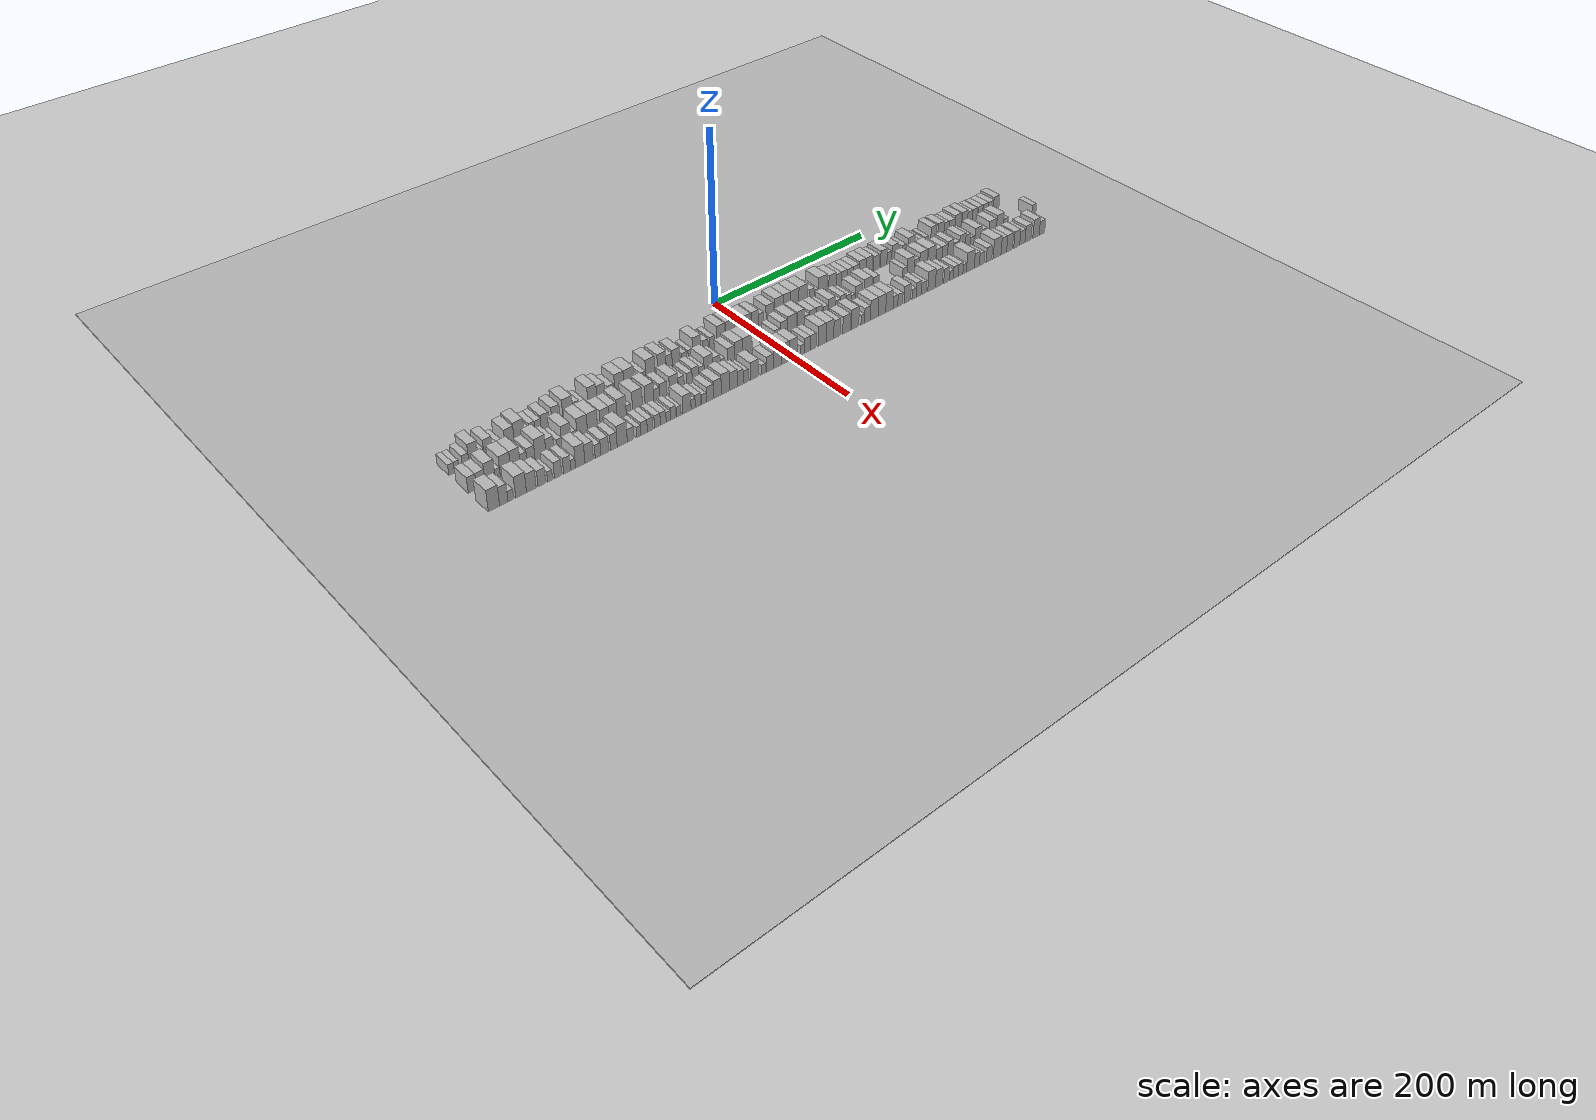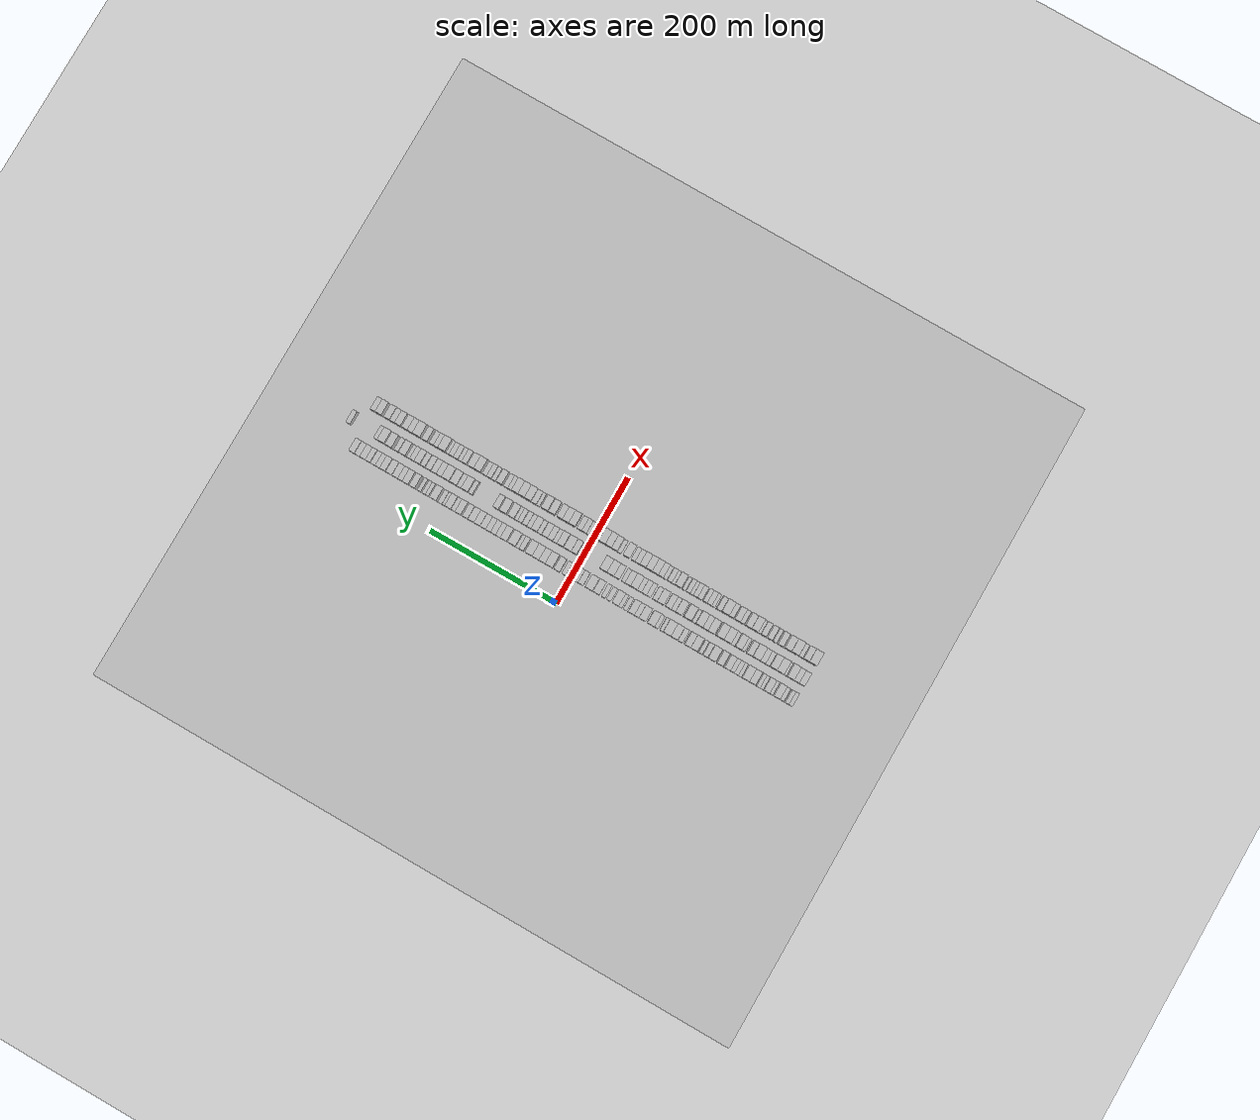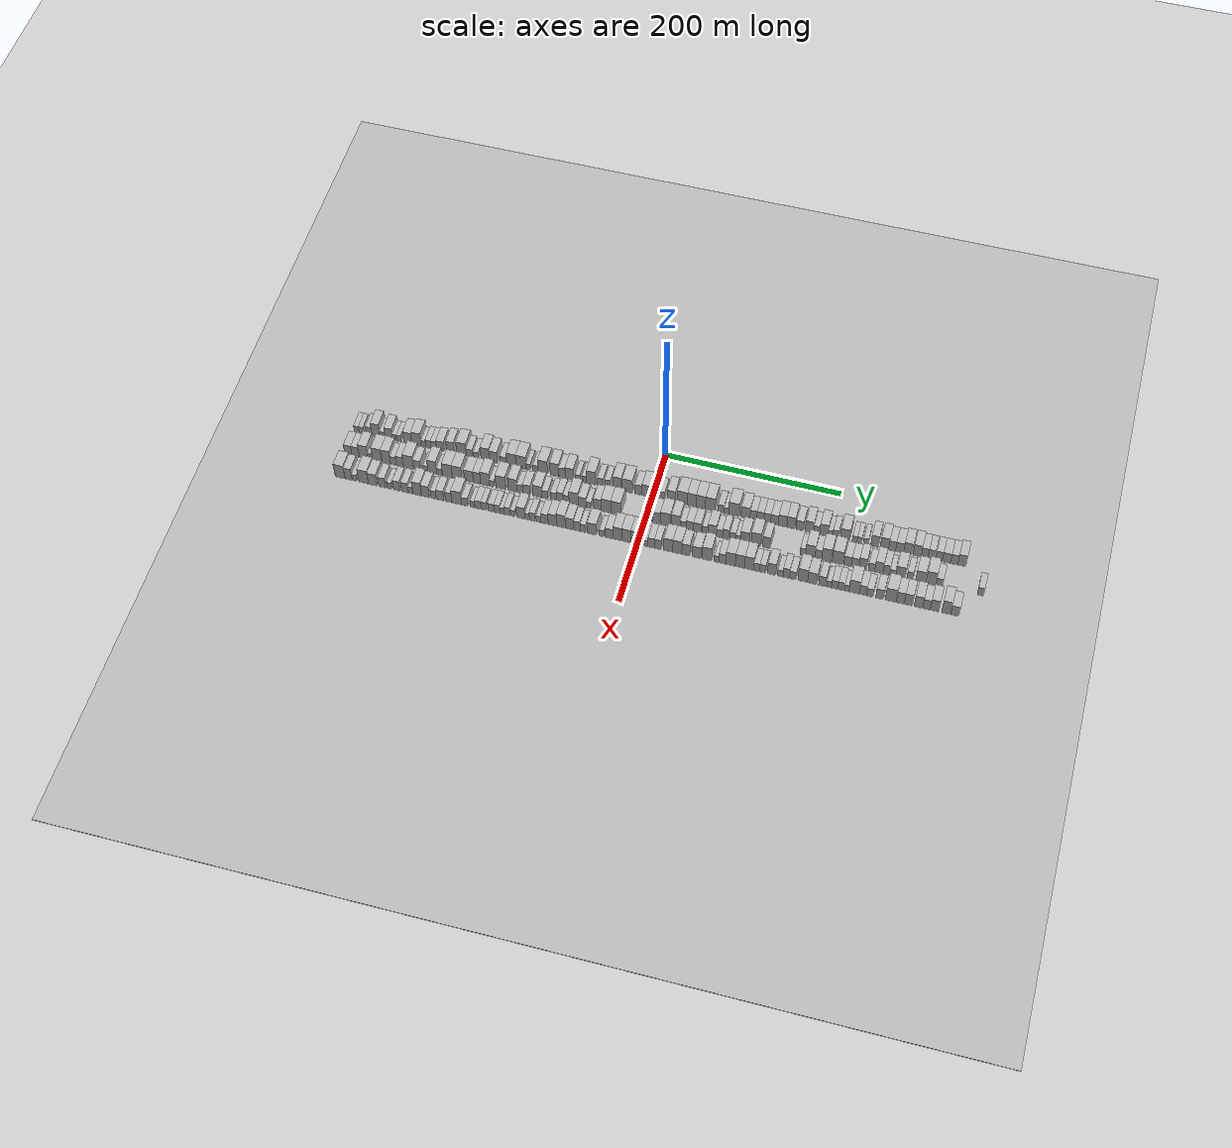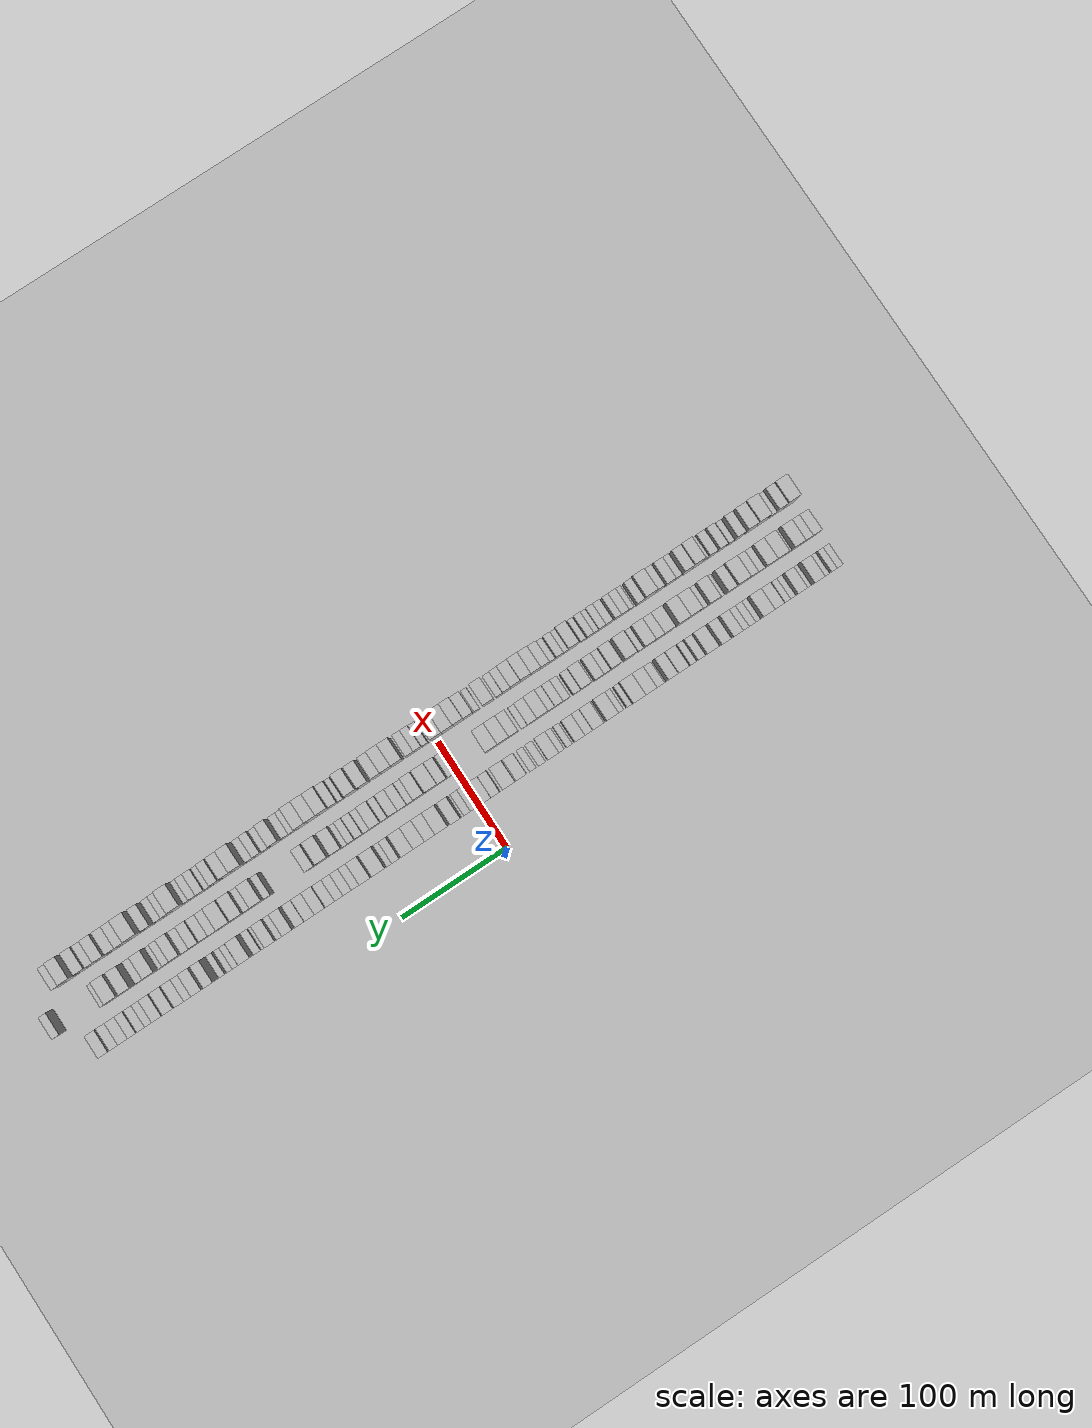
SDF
<?xml version="1.0" encoding="utf-8"?>

<sdf version="1.6">

   <world name="default">

      <gui fullscreen="0">

         <camera name="user_camera">

            <pose>-15 0 4.57585 0 0 0</pose>

            <view_controller>orbit</view_controller>

         </camera>

      </gui>

      <scene>

         <sky>

           <clouds>

             <speed>12</speed>

           </clouds>

         </sky>

         <ambient>0.4 0.4 0.4 1</ambient>

         <background>0.7 0.7 0.7 1</background>

         <shadows>1</shadows>

      </scene>

      <gravity>0 0 -9.8066</gravity>

      <magnetic_field>6e-06 2.3e-05 -4.2e-05</magnetic_field>

      <physics default="0" name="default_physics" type="ode">

         <ode>

            <solver>

               <type>quick</type>

               <iters>10</iters>

               <sor>1.0</sor>

               <use_dynamic_moi_rescaling>0</use_dynamic_moi_rescaling>

            </solver>

            <constraints>

               <cfm>0</cfm>

               <erp>0.2</erp>

               <contact_max_correcting_vel>100</contact_max_correcting_vel>

               <contact_surface_layer>0.001</contact_surface_layer>

            </constraints>

         </ode>

         <max_step_size>0.004</max_step_size>

         <real_time_factor>1</real_time_factor>

         <real_time_update_rate>250</real_time_update_rate>

      </physics>

      <light name="sun" type="directional">

         <cast_shadows>1</cast_shadows>

         <pose>0 0 10 0 0 0</pose>

         <diffuse>0.8 0.8 0.8 1</diffuse>

         <specular>0.2 0.2 0.2 1</specular>

         <attenuation>

            <range>1000</range>

            <constant>0.9</constant>

            <linear>0.01</linear>

            <quadratic>0.001</quadratic>

         </attenuation>

         <direction>-0.5 0.1 -0.9</direction>

      </light>

      <include>

         <name>ground_plane_1</name>

         <uri>model://HANNAS_ground_plane</uri>

         <pose>0 0 0  0 0 0</pose>

      </include>

      <include>

         <name>ground_plane_2</name>

         <uri>model://HANNAS_ground_plane</uri>

         <pose>100 0 0  0 0 0</pose>

      </include>

      <model name="building_1">

         <static>1</static>

         <pose frame="">50.0000 -345.1450 0 0.000000 0.000000 0.000000</pose>

         <link name="link">

            <pose frame="">0 0 6.00 0 0 0</pose>

            <collision name="collision">

               <geometry>

                  <box>

                     <size>20.0000 5.7100 12.0000</size>

                  </box>

               </geometry>

               <max_contacts>10</max_contacts>

               <surface>

                  <contact>

                     <ode/>

                  </contact>

                  <bounce/>

                  <friction>

                     <torsional>

                        <ode/>

                     </torsional>

                     <ode/>

                  </friction>

               </surface>

            </collision>

            <visual name="visual">

               <cast_shadows>0</cast_shadows>

               <geometry>

                  <box>

                     <size>20.0000 5.7100 12.0000</size>

                  </box>

               </geometry>

               <material>

                  <script>

                     <uri>model://HANNAS_wall/materials/scripts</uri>

                     <uri>model://HANNAS_wall/materials/textures</uri>

                     <name>vrc/HANNAS_wall</name>

                  </script>

               </material>

            </visual>

            <self_collide>0</self_collide>

            <enable_wind>0</enable_wind>

            <kinematic>0</kinematic>

         </link>

      </model>

      <model name="building_2">

         <static>1</static>

         <pose frame="">50.0000 -339.5794 0 0.000000 0.000000 0.000000</pose>

         <link name="link">

            <pose frame="">0 0 6.00 0 0 0</pose>

            <collision name="collision">

               <geometry>

                  <box>

                     <size>20.0000 5.4212 12.0000</size>

                  </box>

               </geometry>

               <max_contacts>10</max_contacts>

               <surface>

                  <contact>

                     <ode/>

                  </contact>

                  <bounce/>

                  <friction>

                     <torsional>

                        <ode/>

                     </torsional>

                     <ode/>

                  </friction>

               </surface>

            </collision>

            <visual name="visual">

               <cast_shadows>0</cast_shadows>

               <geometry>

                  <box>

                     <size>20.0000 5.4212 12.0000</size>

                  </box>

               </geometry>

               <material>

                  <script>

                     <uri>model://HANNAS_wall/materials/scripts</uri>

                     <uri>model://HANNAS_wall/materials/textures</uri>

                     <name>vrc/HANNAS_wall</name>

                  </script>

               </material>

            </visual>

            <self_collide>0</self_collide>

            <enable_wind>0</enable_wind>

            <kinematic>0</kinematic>

         </link>

      </model>

      <model name="building_3">

         <static>1</static>

         <pose frame="">50.0000 -330.4114 0 0.000000 0.000000 0.000000</pose>

         <link name="link">

            <pose frame="">0 0 7.50 0 0 0</pose>

            <collision name="collision">

               <geometry>

                  <box>

                     <size>20.0000 6.9149 15.0000</size>

                  </box>

               </geometry>

               <max_contacts>10</max_contacts>

               <surface>

                  <contact>

                     <ode/>

                  </contact>

                  <bounce/>

                  <friction>

                     <torsional>

                        <ode/>

                     </torsional>

                     <ode/>

                  </friction>

               </surface>

            </collision>

            <visual name="visual">

               <cast_shadows>0</cast_shadows>

               <geometry>

                  <box>

                     <size>20.0000 6.9149 15.0000</size>

                  </box>

               </geometry>

               <material>

                  <script>

                     <uri>model://HANNAS_wall/materials/scripts</uri>

                     <uri>model://HANNAS_wall/materials/textures</uri>

                     <name>vrc/HANNAS_wall</name>

                  </script>

               </material>

            </visual>

            <self_collide>0</self_collide>

            <enable_wind>0</enable_wind>

            <kinematic>0</kinematic>

         </link>

      </model>

      <model name="building_4">

         <static>1</static>

         <pose frame="">50.0000 -322.1188 0 0.000000 0.000000 0.000000</pose>

         <link name="link">

            <pose frame="">0 0 12.00 0 0 0</pose>

            <collision name="collision">

               <geometry>

                  <box>

                     <size>20.0000 9.6703 24.0000</size>

                  </box>

               </geometry>

               <max_contacts>10</max_contacts>

               <surface>

                  <contact>

                     <ode/>

                  </contact>

                  <bounce/>

                  <friction>

                     <torsional>

                        <ode/>

                     </torsional>

                     <ode/>

                  </friction>

               </surface>

            </collision>

            <visual name="visual">

               <cast_shadows>0</cast_shadows>

               <geometry>

                  <box>

                     <size>20.0000 9.6703 24.0000</size>

                  </box>

               </geometry>

               <material>

                  <script>

                     <uri>model://HANNAS_wall/materials/scripts</uri>

                     <uri>model://HANNAS_wall/materials/textures</uri>

                     <name>vrc/HANNAS_wall</name>

                  </script>

               </material>

            </visual>

            <self_collide>0</self_collide>

            <enable_wind>0</enable_wind>

            <kinematic>0</kinematic>

         </link>

      </model>

      <model name="building_5">

         <static>1</static>

         <pose frame="">50.0000 -314.3056 0 0.000000 0.000000 0.000000</pose>

         <link name="link">

            <pose frame="">0 0 6.00 0 0 0</pose>

            <collision name="collision">

               <geometry>

                  <box>

                     <size>20.0000 5.9560 12.0000</size>

                  </box>

               </geometry>

               <max_contacts>10</max_contacts>

               <surface>

                  <contact>

                     <ode/>

                  </contact>

                  <bounce/>

                  <friction>

                     <torsional>

                        <ode/>

                     </torsional>

                     <ode/>

                  </friction>

               </surface>

            </collision>

            <visual name="visual">

               <cast_shadows>0</cast_shadows>

               <geometry>

                  <box>

                     <size>20.0000 5.9560 12.0000</size>

                  </box>

               </geometry>

               <material>

                  <script>

                     <uri>model://HANNAS_wall/materials/scripts</uri>

                     <uri>model://HANNAS_wall/materials/textures</uri>

                     <name>vrc/HANNAS_wall</name>

                  </script>

               </material>

            </visual>

            <self_collide>0</self_collide>

            <enable_wind>0</enable_wind>

            <kinematic>0</kinematic>

         </link>

      </model>

      <model name="building_6">

         <static>1</static>

         <pose frame="">50.0000 -306.8105 0 0.000000 0.000000 0.000000</pose>

         <link name="link">

            <pose frame="">0 0 10.50 0 0 0</pose>

            <collision name="collision">

               <geometry>

                  <box>

                     <size>20.0000 9.0343 21.0000</size>

                  </box>

               </geometry>

               <max_contacts>10</max_contacts>

               <surface>

                  <contact>

                     <ode/>

                  </contact>

                  <bounce/>

                  <friction>

                     <torsional>

                        <ode/>

                     </torsional>

                     <ode/>

                  </friction>

               </surface>

            </collision>

            <visual name="visual">

               <cast_shadows>0</cast_shadows>

               <geometry>

                  <box>

                     <size>20.0000 9.0343 21.0000</size>

                  </box>

               </geometry>

               <material>

                  <script>

                     <uri>model://HANNAS_wall/materials/scripts</uri>

                     <uri>model://HANNAS_wall/materials/textures</uri>

                     <name>vrc/HANNAS_wall</name>

                  </script>

               </material>

            </visual>

            <self_collide>0</self_collide>

            <enable_wind>0</enable_wind>

            <kinematic>0</kinematic>

         </link>

      </model>

      <model name="building_7">

         <static>1</static>

         <pose frame="">50.0000 -299.8714 0 0.000000 0.000000 0.000000</pose>

         <link name="link">

            <pose frame="">0 0 6.00 0 0 0</pose>

            <collision name="collision">

               <geometry>

                  <box>

                     <size>20.0000 4.8438 12.0000</size>

                  </box>

               </geometry>

               <max_contacts>10</max_contacts>

               <surface>

                  <contact>

                     <ode/>

                  </contact>

                  <bounce/>

                  <friction>

                     <torsional>

                        <ode/>

                     </torsional>

                     <ode/>

                  </friction>

               </surface>

            </collision>

            <visual name="visual">

               <cast_shadows>0</cast_shadows>

               <geometry>

                  <box>

                     <size>20.0000 4.8438 12.0000</size>

                  </box>

               </geometry>

               <material>

                  <script>

                     <uri>model://HANNAS_wall/materials/scripts</uri>

                     <uri>model://HANNAS_wall/materials/textures</uri>

                     <name>vrc/HANNAS_wall</name>

                  </script>

               </material>

            </visual>

            <self_collide>0</self_collide>

            <enable_wind>0</enable_wind>

            <kinematic>0</kinematic>

         </link>

      </model>

      <model name="building_8">

         <static>1</static>

         <pose frame="">50.0000 -294.8273 0 0.000000 0.000000 0.000000</pose>

         <link name="link">

            <pose frame="">0 0 6.00 0 0 0</pose>

            <collision name="collision">

               <geometry>

                  <box>

                     <size>20.0000 5.2445 12.0000</size>

                  </box>

               </geometry>

               <max_contacts>10</max_contacts>

               <surface>

                  <contact>

                     <ode/>

                  </contact>

                  <bounce/>

                  <friction>

                     <torsional>

                        <ode/>

                     </torsional>

                     <ode/>

                  </friction>

               </surface>

            </collision>

            <visual name="visual">

               <cast_shadows>0</cast_shadows>

               <geometry>

                  <box>

                     <size>20.0000 5.2445 12.0000</size>

                  </box>

               </geometry>

               <material>

                  <script>

                     <uri>model://HANNAS_wall/materials/scripts</uri>

                     <uri>model://HANNAS_wall/materials/textures</uri>

                     <name>vrc/HANNAS_wall</name>

                  </script>

               </material>

            </visual>

            <self_collide>0</self_collide>

            <enable_wind>0</enable_wind>

            <kinematic>0</kinematic>

         </link>

      </model>

      <model name="building_9">

         <static>1</static>

         <pose frame="">50.0000 -284.3233 0 0.000000 0.000000 0.000000</pose>

         <link name="link">

            <pose frame="">0 0 10.50 0 0 0</pose>

            <collision name="collision">

               <geometry>

                  <box>

                     <size>20.0000 9.7636 21.0000</size>

                  </box>

               </geometry>

               <max_contacts>10</max_contacts>

               <surface>

                  <contact>

                     <ode/>

                  </contact>

                  <bounce/>

                  <friction>

                     <torsional>

                        <ode/>

                     </torsional>

                     <ode/>

                  </friction>

               </surface>

            </collision>

            <visual name="visual">

               <cast_shadows>0</cast_shadows>

               <geometry>

                  <box>

                     <size>20.0000 9.7636 21.0000</size>

                  </box>

               </geometry>

               <material>

                  <script>

                     <uri>model://HANNAS_wall/materials/scripts</uri>

                     <uri>model://HANNAS_wall/materials/textures</uri>

                     <name>vrc/HANNAS_wall</name>

                  </script>

               </material>

            </visual>

            <self_collide>0</self_collide>

            <enable_wind>0</enable_wind>

            <kinematic>0</kinematic>

         </link>

      </model>

      <model name="building_10">

         <static>1</static>

         <pose frame="">50.0000 -273.9174 0 0.000000 0.000000 0.000000</pose>

         <link name="link">

            <pose frame="">0 0 12.00 0 0 0</pose>

            <collision name="collision">

               <geometry>

                  <box>

                     <size>20.0000 11.0482 24.0000</size>

                  </box>

               </geometry>

               <max_contacts>10</max_contacts>

               <surface>

                  <contact>

                     <ode/>

                  </contact>

                  <bounce/>

                  <friction>

                     <torsional>

                        <ode/>

                     </torsional>

                     <ode/>

                  </friction>

               </surface>

            </collision>

            <visual name="visual">

               <cast_shadows>0</cast_shadows>

               <geometry>

                  <box>

                     <size>20.0000 11.0482 24.0000</size>

                  </box>

               </geometry>

               <material>

                  <script>

                     <uri>model://HANNAS_wall/materials/scripts</uri>

                     <uri>model://HANNAS_wall/materials/textures</uri>

                     <name>vrc/HANNAS_wall</name>

                  </script>

               </material>

            </visual>

            <self_collide>0</self_collide>

            <enable_wind>0</enable_wind>

            <kinematic>0</kinematic>

         </link>

      </model>

      <model name="building_11">

         <static>1</static>

         <pose frame="">50.0000 -265.7426 0 0.000000 0.000000 0.000000</pose>

         <link name="link">

            <pose frame="">0 0 6.00 0 0 0</pose>

            <collision name="collision">

               <geometry>

                  <box>

                     <size>20.0000 5.3013 12.0000</size>

                  </box>

               </geometry>

               <max_contacts>10</max_contacts>

               <surface>

                  <contact>

                     <ode/>

                  </contact>

                  <bounce/>

                  <friction>

                     <torsional>

                        <ode/>

                     </torsional>

                     <ode/>

                  </friction>

               </surface>

            </collision>

            <visual name="visual">

               <cast_shadows>0</cast_shadows>

               <geometry>

                  <box>

                     <size>20.0000 5.3013 12.0000</size>

                  </box>

               </geometry>

               <material>

                  <script>

                     <uri>model://HANNAS_wall/materials/scripts</uri>

                     <uri>model://HANNAS_wall/materials/textures</uri>

                     <name>vrc/HANNAS_wall</name>

                  </script>

               </material>

            </visual>

            <self_collide>0</self_collide>

            <enable_wind>0</enable_wind>

            <kinematic>0</kinematic>

         </link>

      </model>

      <model name="building_12">

         <static>1</static>

         <pose frame="">50.0000 -259.9697 0 0.000000 0.000000 0.000000</pose>

         <link name="link">

            <pose frame="">0 0 7.50 0 0 0</pose>

            <collision name="collision">

               <geometry>

                  <box>

                     <size>20.0000 6.2447 15.0000</size>

                  </box>

               </geometry>

               <max_contacts>10</max_contacts>

               <surface>

                  <contact>

                     <ode/>

                  </contact>

                  <bounce/>

                  <friction>

                     <torsional>

                        <ode/>

                     </torsional>

                     <ode/>

                  </friction>

               </surface>

            </collision>

            <visual name="visual">

               <cast_shadows>0</cast_shadows>

               <geometry>

                  <box>

                     <size>20.0000 6.2447 15.0000</size>

                  </box>

               </geometry>

               <material>

                  <script>

                     <uri>model://HANNAS_wall/materials/scripts</uri>

                     <uri>model://HANNAS_wall/materials/textures</uri>

                     <name>vrc/HANNAS_wall</name>

                  </script>

               </material>

            </visual>

            <self_collide>0</self_collide>

            <enable_wind>0</enable_wind>

            <kinematic>0</kinematic>

         </link>

      </model>

      <model name="building_13">

         <static>1</static>

         <pose frame="">50.0000 -253.6553 0 0.000000 0.000000 0.000000</pose>

         <link name="link">

            <pose frame="">0 0 7.50 0 0 0</pose>

            <collision name="collision">

               <geometry>

                  <box>

                     <size>20.0000 6.3839 15.0000</size>

                  </box>

               </geometry>

               <max_contacts>10</max_contacts>

               <surface>

                  <contact>

                     <ode/>

                  </contact>

                  <bounce/>

                  <friction>

                     <torsional>

                        <ode/>

                     </torsional>

                     <ode/>

                  </friction>

               </surface>

            </collision>

            <visual name="visual">

               <cast_shadows>0</cast_shadows>

               <geometry>

                  <box>

                     <size>20.0000 6.3839 15.0000</size>

                  </box>

               </geometry>

               <material>

                  <script>

                     <uri>model://HANNAS_wall/materials/scripts</uri>

                     <uri>model://HANNAS_wall/materials/textures</uri>

                     <name>vrc/HANNAS_wall</name>

                  </script>

               </material>

            </visual>

            <self_collide>0</self_collide>

            <enable_wind>0</enable_wind>

            <kinematic>0</kinematic>

         </link>

      </model>

      <model name="building_14">

         <static>1</static>

         <pose frame="">50.0000 -245.9653 0 0.000000 0.000000 0.000000</pose>

         <link name="link">

            <pose frame="">0 0 9.00 0 0 0</pose>

            <collision name="collision">

               <geometry>

                  <box>

                     <size>20.0000 8.9961 18.0000</size>

                  </box>

               </geometry>

               <max_contacts>10</max_contacts>

               <surface>

                  <contact>

                     <ode/>

                  </contact>

                  <bounce/>

                  <friction>

                     <torsional>

                        <ode/>

                     </torsional>

                     <ode/>

                  </friction>

               </surface>

            </collision>

            <visual name="visual">

               <cast_shadows>0</cast_shadows>

               <geometry>

                  <box>

                     <size>20.0000 8.9961 18.0000</size>

                  </box>

               </geometry>

               <material>

                  <script>

                     <uri>model://HANNAS_wall/materials/scripts</uri>

                     <uri>model://HANNAS_wall/materials/textures</uri>

                     <name>vrc/HANNAS_wall</name>

                  </script>

               </material>

            </visual>

            <self_collide>0</self_collide>

            <enable_wind>0</enable_wind>

            <kinematic>0</kinematic>

         </link>

      </model>

      <model name="building_15">

         <static>1</static>

         <pose frame="">50.0000 -234.0127 0 0.000000 0.000000 0.000000</pose>

         <link name="link">

            <pose frame="">0 0 10.50 0 0 0</pose>

            <collision name="collision">

               <geometry>

                  <box>

                     <size>20.0000 8.9091 21.0000</size>

                  </box>

               </geometry>

               <max_contacts>10</max_contacts>

               <surface>

                  <contact>

                     <ode/>

                  </contact>

                  <bounce/>

                  <friction>

                     <torsional>

                        <ode/>

                     </torsional>

                     <ode/>

                  </friction>

               </surface>

            </collision>

            <visual name="visual">

               <cast_shadows>0</cast_shadows>

               <geometry>

                  <box>

                     <size>20.0000 8.9091 21.0000</size>

                  </box>

               </geometry>

               <material>

                  <script>

                     <uri>model://HANNAS_wall/materials/scripts</uri>

                     <uri>model://HANNAS_wall/materials/textures</uri>

                     <name>vrc/HANNAS_wall</name>

                  </script>

               </material>

            </visual>

            <self_collide>0</self_collide>

            <enable_wind>0</enable_wind>

            <kinematic>0</kinematic>

         </link>

      </model>

      <model name="building_16">

         <static>1</static>

         <pose frame="">50.0000 -220.8957 0 0.000000 0.000000 0.000000</pose>

         <link name="link">

            <pose frame="">0 0 12.00 0 0 0</pose>

            <collision name="collision">

               <geometry>

                  <box>

                     <size>20.0000 11.3247 24.0000</size>

                  </box>

               </geometry>

               <max_contacts>10</max_contacts>

               <surface>

                  <contact>

                     <ode/>

                  </contact>

                  <bounce/>

                  <friction>

                     <torsional>

                        <ode/>

                     </torsional>

                     <ode/>

                  </friction>

               </surface>

            </collision>

            <visual name="visual">

               <cast_shadows>0</cast_shadows>

               <geometry>

                  <box>

                     <size>20.0000 11.3247 24.0000</size>

                  </box>

               </geometry>

               <material>

                  <script>

                     <uri>model://HANNAS_wall/materials/scripts</uri>

                     <uri>model://HANNAS_wall/materials/textures</uri>

                     <name>vrc/HANNAS_wall</name>

                  </script>

               </material>

            </visual>

            <self_collide>0</self_collide>

            <enable_wind>0</enable_wind>

            <kinematic>0</kinematic>

         </link>

      </model>

      <model name="building_17">

         <static>1</static>

         <pose frame="">50.0000 -211.6455 0 0.000000 0.000000 0.000000</pose>

         <link name="link">

            <pose frame="">0 0 7.50 0 0 0</pose>

            <collision name="collision">

               <geometry>

                  <box>

                     <size>20.0000 7.1758 15.0000</size>

                  </box>

               </geometry>

               <max_contacts>10</max_contacts>

               <surface>

                  <contact>

                     <ode/>

                  </contact>

                  <bounce/>

                  <friction>

                     <torsional>

                        <ode/>

                     </torsional>

                     <ode/>

                  </friction>

               </surface>

            </collision>

            <visual name="visual">

               <cast_shadows>0</cast_shadows>

               <geometry>

                  <box>

                     <size>20.0000 7.1758 15.0000</size>

                  </box>

               </geometry>

               <material>

                  <script>

                     <uri>model://HANNAS_wall/materials/scripts</uri>

                     <uri>model://HANNAS_wall/materials/textures</uri>

                     <name>vrc/HANNAS_wall</name>

                  </script>

               </material>

            </visual>

            <self_collide>0</self_collide>

            <enable_wind>0</enable_wind>

            <kinematic>0</kinematic>

         </link>

      </model>

      <model name="building_18">

         <static>1</static>

         <pose frame="">50.0000 -204.1950 0 0.000000 0.000000 0.000000</pose>

         <link name="link">

            <pose frame="">0 0 6.00 0 0 0</pose>

            <collision name="collision">

               <geometry>

                  <box>

                     <size>20.0000 5.7251 12.0000</size>

                  </box>

               </geometry>

               <max_contacts>10</max_contacts>

               <surface>

                  <contact>

                     <ode/>

                  </contact>

                  <bounce/>

                  <friction>

                     <torsional>

                        <ode/>

                     </torsional>

                     <ode/>

                  </friction>

               </surface>

            </collision>

            <visual name="visual">

               <cast_shadows>0</cast_shadows>

               <geometry>

                  <box>

                     <size>20.0000 5.7251 12.0000</size>

                  </box>

               </geometry>

               <material>

                  <script>

                     <uri>model://HANNAS_wall/materials/scripts</uri>

                     <uri>model://HANNAS_wall/materials/textures</uri>

                     <name>vrc/HANNAS_wall</name>

                  </script>

               </material>

            </visual>

            <self_collide>0</self_collide>

            <enable_wind>0</enable_wind>

            <kinematic>0</kinematic>

         </link>

      </model>

      <model name="building_19">

         <static>1</static>

         <pose frame="">50.0000 -193.2733 0 0.000000 0.000000 0.000000</pose>

         <link name="link">

            <pose frame="">0 0 12.00 0 0 0</pose>

            <collision name="collision">

               <geometry>

                  <box>

                     <size>20.0000 10.1184 24.0000</size>

                  </box>

               </geometry>

               <max_contacts>10</max_contacts>

               <surface>

                  <contact>

                     <ode/>

                  </contact>

                  <bounce/>

                  <friction>

                     <torsional>

                        <ode/>

                     </torsional>

                     <ode/>

                  </friction>

               </surface>

            </collision>

            <visual name="visual">

               <cast_shadows>0</cast_shadows>

               <geometry>

                  <box>

                     <size>20.0000 10.1184 24.0000</size>

                  </box>

               </geometry>

               <material>

                  <script>

                     <uri>model://HANNAS_wall/materials/scripts</uri>

                     <uri>model://HANNAS_wall/materials/textures</uri>

                     <name>vrc/HANNAS_wall</name>

                  </script>

               </material>

            </visual>

            <self_collide>0</self_collide>

            <enable_wind>0</enable_wind>

            <kinematic>0</kinematic>

         </link>

      </model>

      <model name="building_20">

         <static>1</static>

         <pose frame="">50.0000 -183.6181 0 0.000000 0.000000 0.000000</pose>

         <link name="link">

            <pose frame="">0 0 10.50 0 0 0</pose>

            <collision name="collision">

               <geometry>

                  <box>

                     <size>20.0000 9.1921 21.0000</size>

                  </box>

               </geometry>

               <max_contacts>10</max_contacts>

               <surface>

                  <contact>

                     <ode/>

                  </contact>

                  <bounce/>

                  <friction>

                     <torsional>

                        <ode/>

                     </torsional>

                     <ode/>

                  </friction>

               </surface>

            </collision>

            <visual name="visual">

               <cast_shadows>0</cast_shadows>

               <geometry>

                  <box>

                     <size>20.0000 9.1921 21.0000</size>

                  </box>

               </geometry>

               <material>

                  <script>

                     <uri>model://HANNAS_wall/materials/scripts</uri>

                     <uri>model://HANNAS_wall/materials/textures</uri>

                     <name>vrc/HANNAS_wall</name>

                  </script>

               </material>

            </visual>

            <self_collide>0</self_collide>

            <enable_wind>0</enable_wind>

            <kinematic>0</kinematic>

         </link>

      </model>

      <model name="building_21">

         <static>1</static>

         <pose frame="">50.0000 -172.4072 0 0.000000 0.000000 0.000000</pose>

         <link name="link">

            <pose frame="">0 0 7.50 0 0 0</pose>

            <collision name="collision">

               <geometry>

                  <box>

                     <size>20.0000 7.2296 15.0000</size>

                  </box>

               </geometry>

               <max_contacts>10</max_contacts>

               <surface>

                  <contact>

                     <ode/>

                  </contact>

                  <bounce/>

                  <friction>

                     <torsional>

                        <ode/>

                     </torsional>

                     <ode/>

                  </friction>

               </surface>

            </collision>

            <visual name="visual">

               <cast_shadows>0</cast_shadows>

               <geometry>

                  <box>

                     <size>20.0000 7.2296 15.0000</size>

                  </box>

               </geometry>

               <material>

                  <script>

                     <uri>model://HANNAS_wall/materials/scripts</uri>

                     <uri>model://HANNAS_wall/materials/textures</uri>

                     <name>vrc/HANNAS_wall</name>

                  </script>

               </material>

            </visual>

            <self_collide>0</self_collide>

            <enable_wind>0</enable_wind>

            <kinematic>0</kinematic>

         </link>

      </model>

      <model name="building_22">

         <static>1</static>

         <pose frame="">50.0000 -162.5162 0 0.000000 0.000000 0.000000</pose>

         <link name="link">

            <pose frame="">0 0 12.00 0 0 0</pose>

            <collision name="collision">

               <geometry>

                  <box>

                     <size>20.0000 10.5525 24.0000</size>

                  </box>

               </geometry>

               <max_contacts>10</max_contacts>

               <surface>

                  <contact>

                     <ode/>

                  </contact>

                  <bounce/>

                  <friction>

                     <torsional>

                        <ode/>

                     </torsional>

                     <ode/>

                  </friction>

               </surface>

            </collision>

            <visual name="visual">

               <cast_shadows>0</cast_shadows>

               <geometry>

                  <box>

                     <size>20.0000 10.5525 24.0000</size>

                  </box>

               </geometry>

               <material>

                  <script>

                     <uri>model://HANNAS_wall/materials/scripts</uri>

                     <uri>model://HANNAS_wall/materials/textures</uri>

                     <name>vrc/HANNAS_wall</name>

                  </script>

               </material>

            </visual>

            <self_collide>0</self_collide>

            <enable_wind>0</enable_wind>

            <kinematic>0</kinematic>

         </link>

      </model>

      <model name="building_23">

         <static>1</static>

         <pose frame="">50.0000 -151.3378 0 0.000000 0.000000 0.000000</pose>

         <link name="link">

            <pose frame="">0 0 12.00 0 0 0</pose>

            <collision name="collision">

               <geometry>

                  <box>

                     <size>20.0000 11.8043 24.0000</size>

                  </box>

               </geometry>

               <max_contacts>10</max_contacts>

               <surface>

                  <contact>

                     <ode/>

                  </contact>

                  <bounce/>

                  <friction>

                     <torsional>

                        <ode/>

                     </torsional>

                     <ode/>

                  </friction>

               </surface>

            </collision>

            <visual name="visual">

               <cast_shadows>0</cast_shadows>

               <geometry>

                  <box>

                     <size>20.0000 11.8043 24.0000</size>

                  </box>

               </geometry>

               <material>

                  <script>

                     <uri>model://HANNAS_wall/materials/scripts</uri>

                     <uri>model://HANNAS_wall/materials/textures</uri>

                     <name>vrc/HANNAS_wall</name>

                  </script>

               </material>

            </visual>

            <self_collide>0</self_collide>

            <enable_wind>0</enable_wind>

            <kinematic>0</kinematic>

         </link>

      </model>

      <model name="building_24">

         <static>1</static>

         <pose frame="">50.0000 -143.0119 0 0.000000 0.000000 0.000000</pose>

         <link name="link">

            <pose frame="">0 0 6.00 0 0 0</pose>

            <collision name="collision">

               <geometry>

                  <box>

                     <size>20.0000 4.8476 12.0000</size>

                  </box>

               </geometry>

               <max_contacts>10</max_contacts>

               <surface>

                  <contact>

                     <ode/>

                  </contact>

                  <bounce/>

                  <friction>

                     <torsional>

                        <ode/>

                     </torsional>

                     <ode/>

                  </friction>

               </surface>

            </collision>

            <visual name="visual">

               <cast_shadows>0</cast_shadows>

               <geometry>

                  <box>

                     <size>20.0000 4.8476 12.0000</size>

                  </box>

               </geometry>

               <material>

                  <script>

                     <uri>model://HANNAS_wall/materials/scripts</uri>

                     <uri>model://HANNAS_wall/materials/textures</uri>

                     <name>vrc/HANNAS_wall</name>

                  </script>

               </material>

            </visual>

            <self_collide>0</self_collide>

            <enable_wind>0</enable_wind>

            <kinematic>0</kinematic>

         </link>

      </model>

      <model name="building_25">

         <static>1</static>

         <pose frame="">50.0000 -134.6593 0 0.000000 0.000000 0.000000</pose>

         <link name="link">

            <pose frame="">0 0 6.00 0 0 0</pose>

            <collision name="collision">

               <geometry>

                  <box>

                     <size>20.0000 5.8576 12.0000</size>

                  </box>

               </geometry>

               <max_contacts>10</max_contacts>

               <surface>

                  <contact>

                     <ode/>

                  </contact>

                  <bounce/>

                  <friction>

                     <torsional>

                        <ode/>

                     </torsional>

                     <ode/>

                  </friction>

               </surface>

            </collision>

            <visual name="visual">

               <cast_shadows>0</cast_shadows>

               <geometry>

                  <box>

                     <size>20.0000 5.8576 12.0000</size>

                  </box>

               </geometry>

               <material>

                  <script>

                     <uri>model://HANNAS_wall/materials/scripts</uri>

                     <uri>model://HANNAS_wall/materials/textures</uri>

                     <name>vrc/HANNAS_wall</name>

                  </script>

               </material>

            </visual>

            <self_collide>0</self_collide>

            <enable_wind>0</enable_wind>

            <kinematic>0</kinematic>

         </link>

      </model>

      <model name="building_26">

         <static>1</static>

         <pose frame="">50.0000 -126.2061 0 0.000000 0.000000 0.000000</pose>

         <link name="link">

            <pose frame="">0 0 12.00 0 0 0</pose>

            <collision name="collision">

               <geometry>

                  <box>

                     <size>20.0000 11.0488 24.0000</size>

                  </box>

               </geometry>

               <max_contacts>10</max_contacts>

               <surface>

                  <contact>

                     <ode/>

                  </contact>

                  <bounce/>

                  <friction>

                     <torsional>

                        <ode/>

                     </torsional>

                     <ode/>

                  </friction>

               </surface>

            </collision>

            <visual name="visual">

               <cast_shadows>0</cast_shadows>

               <geometry>

                  <box>

                     <size>20.0000 11.0488 24.0000</size>

                  </box>

               </geometry>

               <material>

                  <script>

                     <uri>model://HANNAS_wall/materials/scripts</uri>

                     <uri>model://HANNAS_wall/materials/textures</uri>

                     <name>vrc/HANNAS_wall</name>

                  </script>

               </material>

            </visual>

            <self_collide>0</self_collide>

            <enable_wind>0</enable_wind>

            <kinematic>0</kinematic>

         </link>

      </model>

      <model name="building_27">

         <static>1</static>

         <pose frame="">50.0000 -112.5648 0 0.000000 0.000000 0.000000</pose>

         <link name="link">

            <pose frame="">0 0 12.00 0 0 0</pose>

            <collision name="collision">

               <geometry>

                  <box>

                     <size>20.0000 10.2338 24.0000</size>

                  </box>

               </geometry>

               <max_contacts>10</max_contacts>

               <surface>

                  <contact>

                     <ode/>

                  </contact>

                  <bounce/>

                  <friction>

                     <torsional>

                        <ode/>

                     </torsional>

                     <ode/>

                  </friction>

               </surface>

            </collision>

            <visual name="visual">

               <cast_shadows>0</cast_shadows>

               <geometry>

                  <box>

                     <size>20.0000 10.2338 24.0000</size>

                  </box>

               </geometry>

               <material>

                  <script>

                     <uri>model://HANNAS_wall/materials/scripts</uri>

                     <uri>model://HANNAS_wall/materials/textures</uri>

                     <name>vrc/HANNAS_wall</name>

                  </script>

               </material>

            </visual>

            <self_collide>0</self_collide>

            <enable_wind>0</enable_wind>

            <kinematic>0</kinematic>

         </link>

      </model>

      <model name="building_28">

         <static>1</static>

         <pose frame="">50.0000 -103.8133 0 0.000000 0.000000 0.000000</pose>

         <link name="link">

            <pose frame="">0 0 9.00 0 0 0</pose>

            <collision name="collision">

               <geometry>

                  <box>

                     <size>20.0000 7.2692 18.0000</size>

                  </box>

               </geometry>

               <max_contacts>10</max_contacts>

               <surface>

                  <contact>

                     <ode/>

                  </contact>

                  <bounce/>

                  <friction>

                     <torsional>

                        <ode/>

                     </torsional>

                     <ode/>

                  </friction>

               </surface>

            </collision>

            <visual name="visual">

               <cast_shadows>0</cast_shadows>

               <geometry>

                  <box>

                     <size>20.0000 7.2692 18.0000</size>

                  </box>

               </geometry>

               <material>

                  <script>

                     <uri>model://HANNAS_wall/materials/scripts</uri>

                     <uri>model://HANNAS_wall/materials/textures</uri>

                     <name>vrc/HANNAS_wall</name>

                  </script>

               </material>

            </visual>

            <self_collide>0</self_collide>

            <enable_wind>0</enable_wind>

            <kinematic>0</kinematic>

         </link>

      </model>

      <model name="building_29">

         <static>1</static>

         <pose frame="">50.0000 -95.3937 0 0.000000 0.000000 0.000000</pose>

         <link name="link">

            <pose frame="">0 0 10.50 0 0 0</pose>

            <collision name="collision">

               <geometry>

                  <box>

                     <size>20.0000 9.5701 21.0000</size>

                  </box>

               </geometry>

               <max_contacts>10</max_contacts>

               <surface>

                  <contact>

                     <ode/>

                  </contact>

                  <bounce/>

                  <friction>

                     <torsional>

                        <ode/>

                     </torsional>

                     <ode/>

                  </friction>

               </surface>

            </collision>

            <visual name="visual">

               <cast_shadows>0</cast_shadows>

               <geometry>

                  <box>

                     <size>20.0000 9.5701 21.0000</size>

                  </box>

               </geometry>

               <material>

                  <script>

                     <uri>model://HANNAS_wall/materials/scripts</uri>

                     <uri>model://HANNAS_wall/materials/textures</uri>

                     <name>vrc/HANNAS_wall</name>

                  </script>

               </material>

            </visual>

            <self_collide>0</self_collide>

            <enable_wind>0</enable_wind>

            <kinematic>0</kinematic>

         </link>

      </model>

      <model name="building_30">

         <static>1</static>

         <pose frame="">50.0000 -85.7997 0 0.000000 0.000000 0.000000</pose>

         <link name="link">

            <pose frame="">0 0 6.00 0 0 0</pose>

            <collision name="collision">

               <geometry>

                  <box>

                     <size>20.0000 5.6180 12.0000</size>

                  </box>

               </geometry>

               <max_contacts>10</max_contacts>

               <surface>

                  <contact>

                     <ode/>

                  </contact>

                  <bounce/>

                  <friction>

                     <torsional>

                        <ode/>

                     </torsional>

                     <ode/>

                  </friction>

               </surface>

            </collision>

            <visual name="visual">

               <cast_shadows>0</cast_shadows>

               <geometry>

                  <box>

                     <size>20.0000 5.6180 12.0000</size>

                  </box>

               </geometry>

               <material>

                  <script>

                     <uri>model://HANNAS_wall/materials/scripts</uri>

                     <uri>model://HANNAS_wall/materials/textures</uri>

                     <name>vrc/HANNAS_wall</name>

                  </script>

               </material>

            </visual>

            <self_collide>0</self_collide>

            <enable_wind>0</enable_wind>

            <kinematic>0</kinematic>

         </link>

      </model>

      <model name="building_31">

         <static>1</static>

         <pose frame="">50.0000 -78.2784 0 0.000000 0.000000 0.000000</pose>

         <link name="link">

            <pose frame="">0 0 6.00 0 0 0</pose>

            <collision name="collision">

               <geometry>

                  <box>

                     <size>20.0000 5.4245 12.0000</size>

                  </box>

               </geometry>

               <max_contacts>10</max_contacts>

               <surface>

                  <contact>

                     <ode/>

                  </contact>

                  <bounce/>

                  <friction>

                     <torsional>

                        <ode/>

                     </torsional>

                     <ode/>

                  </friction>

               </surface>

            </collision>

            <visual name="visual">

               <cast_shadows>0</cast_shadows>

               <geometry>

                  <box>

                     <size>20.0000 5.4245 12.0000</size>

                  </box>

               </geometry>

               <material>

                  <script>

                     <uri>model://HANNAS_wall/materials/scripts</uri>

                     <uri>model://HANNAS_wall/materials/textures</uri>

                     <name>vrc/HANNAS_wall</name>

                  </script>

               </material>

            </visual>

            <self_collide>0</self_collide>

            <enable_wind>0</enable_wind>

            <kinematic>0</kinematic>

         </link>

      </model>

      <model name="building_32">

         <static>1</static>

         <pose frame="">50.0000 -70.3503 0 0.000000 0.000000 0.000000</pose>

         <link name="link">

            <pose frame="">0 0 12.00 0 0 0</pose>

            <collision name="collision">

               <geometry>

                  <box>

                     <size>20.0000 10.4315 24.0000</size>

                  </box>

               </geometry>

               <max_contacts>10</max_contacts>

               <surface>

                  <contact>

                     <ode/>

                  </contact>

                  <bounce/>

                  <friction>

                     <torsional>

                        <ode/>

                     </torsional>

                     <ode/>

                  </friction>

               </surface>

            </collision>

            <visual name="visual">

               <cast_shadows>0</cast_shadows>

               <geometry>

                  <box>

                     <size>20.0000 10.4315 24.0000</size>

                  </box>

               </geometry>

               <material>

                  <script>

                     <uri>model://HANNAS_wall/materials/scripts</uri>

                     <uri>model://HANNAS_wall/materials/textures</uri>

                     <name>vrc/HANNAS_wall</name>

                  </script>

               </material>

            </visual>

            <self_collide>0</self_collide>

            <enable_wind>0</enable_wind>

            <kinematic>0</kinematic>

         </link>

      </model>

      <model name="building_33">

         <static>1</static>

         <pose frame="">50.0000 -59.7436 0 0.000000 0.000000 0.000000</pose>

         <link name="link">

            <pose frame="">0 0 7.50 0 0 0</pose>

            <collision name="collision">

               <geometry>

                  <box>

                     <size>20.0000 6.7820 15.0000</size>

                  </box>

               </geometry>

               <max_contacts>10</max_contacts>

               <surface>

                  <contact>

                     <ode/>

                  </contact>

                  <bounce/>

                  <friction>

                     <torsional>

                        <ode/>

                     </torsional>

                     <ode/>

                  </friction>

               </surface>

            </collision>

            <visual name="visual">

               <cast_shadows>0</cast_shadows>

               <geometry>

                  <box>

                     <size>20.0000 6.7820 15.0000</size>

                  </box>

               </geometry>

               <material>

                  <script>

                     <uri>model://HANNAS_wall/materials/scripts</uri>

                     <uri>model://HANNAS_wall/materials/textures</uri>

                     <name>vrc/HANNAS_wall</name>

                  </script>

               </material>

            </visual>

            <self_collide>0</self_collide>

            <enable_wind>0</enable_wind>

            <kinematic>0</kinematic>

         </link>

      </model>

      <model name="building_34">

         <static>1</static>

         <pose frame="">50.0000 -51.3099 0 0.000000 0.000000 0.000000</pose>

         <link name="link">

            <pose frame="">0 0 7.50 0 0 0</pose>

            <collision name="collision">

               <geometry>

                  <box>

                     <size>20.0000 6.0854 15.0000</size>

                  </box>

               </geometry>

               <max_contacts>10</max_contacts>

               <surface>

                  <contact>

                     <ode/>

                  </contact>

                  <bounce/>

                  <friction>

                     <torsional>

                        <ode/>

                     </torsional>

                     <ode/>

                  </friction>

               </surface>

            </collision>

            <visual name="visual">

               <cast_shadows>0</cast_shadows>

               <geometry>

                  <box>

                     <size>20.0000 6.0854 15.0000</size>

                  </box>

               </geometry>

               <material>

                  <script>

                     <uri>model://HANNAS_wall/materials/scripts</uri>

                     <uri>model://HANNAS_wall/materials/textures</uri>

                     <name>vrc/HANNAS_wall</name>

                  </script>

               </material>

            </visual>

            <self_collide>0</self_collide>

            <enable_wind>0</enable_wind>

            <kinematic>0</kinematic>

         </link>

      </model>

      <model name="building_35">

         <static>1</static>

         <pose frame="">50.0000 -40.3754 0 0.000000 0.000000 0.000000</pose>

         <link name="link">

            <pose frame="">0 0 12.00 0 0 0</pose>

            <collision name="collision">

               <geometry>

                  <box>

                     <size>20.0000 9.7837 24.0000</size>

                  </box>

               </geometry>

               <max_contacts>10</max_contacts>

               <surface>

                  <contact>

                     <ode/>

                  </contact>

                  <bounce/>

                  <friction>

                     <torsional>

                        <ode/>

                     </torsional>

                     <ode/>

                  </friction>

               </surface>

            </collision>

            <visual name="visual">

               <cast_shadows>0</cast_shadows>

               <geometry>

                  <box>

                     <size>20.0000 9.7837 24.0000</size>

                  </box>

               </geometry>

               <material>

                  <script>

                     <uri>model://HANNAS_wall/materials/scripts</uri>

                     <uri>model://HANNAS_wall/materials/textures</uri>

                     <name>vrc/HANNAS_wall</name>

                  </script>

               </material>

            </visual>

            <self_collide>0</self_collide>

            <enable_wind>0</enable_wind>

            <kinematic>0</kinematic>

         </link>

      </model>

      <model name="building_36">

         <static>1</static>

         <pose frame="">50.0000 -28.7135 0 0.000000 0.000000 0.000000</pose>

         <link name="link">

            <pose frame="">0 0 12.00 0 0 0</pose>

            <collision name="collision">

               <geometry>

                  <box>

                     <size>20.0000 11.5400 24.0000</size>

                  </box>

               </geometry>

               <max_contacts>10</max_contacts>

               <surface>

                  <contact>

                     <ode/>

                  </contact>

                  <bounce/>

                  <friction>

                     <torsional>

                        <ode/>

                     </torsional>

                     <ode/>

                  </friction>

               </surface>

            </collision>

            <visual name="visual">

               <cast_shadows>0</cast_shadows>

               <geometry>

                  <box>

                     <size>20.0000 11.5400 24.0000</size>

                  </box>

               </geometry>

               <material>

                  <script>

                     <uri>model://HANNAS_wall/materials/scripts</uri>

                     <uri>model://HANNAS_wall/materials/textures</uri>

                     <name>vrc/HANNAS_wall</name>

                  </script>

               </material>

            </visual>

            <self_collide>0</self_collide>

            <enable_wind>0</enable_wind>

            <kinematic>0</kinematic>

         </link>

      </model>

      <model name="building_37">

         <static>1</static>

         <pose frame="">50.0000 -15.8986 0 0.000000 0.000000 0.000000</pose>

         <link name="link">

            <pose frame="">0 0 9.00 0 0 0</pose>

            <collision name="collision">

               <geometry>

                  <box>

                     <size>20.0000 8.0898 18.0000</size>

                  </box>

               </geometry>

               <max_contacts>10</max_contacts>

               <surface>

                  <contact>

                     <ode/>

                  </contact>

                  <bounce/>

                  <friction>

                     <torsional>

                        <ode/>

                     </torsional>

                     <ode/>

                  </friction>

               </surface>

            </collision>

            <visual name="visual">

               <cast_shadows>0</cast_shadows>

               <geometry>

                  <box>

                     <size>20.0000 8.0898 18.0000</size>

                  </box>

               </geometry>

               <material>

                  <script>

                     <uri>model://HANNAS_wall/materials/scripts</uri>

                     <uri>model://HANNAS_wall/materials/textures</uri>

                     <name>vrc/HANNAS_wall</name>

                  </script>

               </material>

            </visual>

            <self_collide>0</self_collide>

            <enable_wind>0</enable_wind>

            <kinematic>0</kinematic>

         </link>

      </model>

      <model name="building_38">

         <static>1</static>

         <pose frame="">50.0000 -7.3106 0 0.000000 0.000000 0.000000</pose>

         <link name="link">

            <pose frame="">0 0 10.50 0 0 0</pose>

            <collision name="collision">

               <geometry>

                  <box>

                     <size>20.0000 9.0862 21.0000</size>

                  </box>

               </geometry>

               <max_contacts>10</max_contacts>

               <surface>

                  <contact>

                     <ode/>

                  </contact>

                  <bounce/>

                  <friction>

                     <torsional>

                        <ode/>

                     </torsional>

                     <ode/>

                  </friction>

               </surface>

            </collision>

            <visual name="visual">

               <cast_shadows>0</cast_shadows>

               <geometry>

                  <box>

                     <size>20.0000 9.0862 21.0000</size>

                  </box>

               </geometry>

               <material>

                  <script>

                     <uri>model://HANNAS_wall/materials/scripts</uri>

                     <uri>model://HANNAS_wall/materials/textures</uri>

                     <name>vrc/HANNAS_wall</name>

                  </script>

               </material>

            </visual>

            <self_collide>0</self_collide>

            <enable_wind>0</enable_wind>

            <kinematic>0</kinematic>

         </link>

      </model>

      <model name="building_39">

         <static>1</static>

         <pose frame="">50.0000 2.6917 0 0.000000 0.000000 0.000000</pose>

         <link name="link">

            <pose frame="">0 0 10.50 0 0 0</pose>

            <collision name="collision">

               <geometry>

                  <box>

                     <size>20.0000 8.9184 21.0000</size>

                  </box>

               </geometry>

               <max_contacts>10</max_contacts>

               <surface>

                  <contact>

                     <ode/>

                  </contact>

                  <bounce/>

                  <friction>

                     <torsional>

                        <ode/>

                     </torsional>

                     <ode/>

                  </friction>

               </surface>

            </collision>

            <visual name="visual">

               <cast_shadows>0</cast_shadows>

               <geometry>

                  <box>

                     <size>20.0000 8.9184 21.0000</size>

                  </box>

               </geometry>

               <material>

                  <script>

                     <uri>model://HANNAS_wall/materials/scripts</uri>

                     <uri>model://HANNAS_wall/materials/textures</uri>

                     <name>vrc/HANNAS_wall</name>

                  </script>

               </material>

            </visual>

            <self_collide>0</self_collide>

            <enable_wind>0</enable_wind>

            <kinematic>0</kinematic>

         </link>

      </model>

      <model name="building_40">

         <static>1</static>

         <pose frame="">50.0000 10.5797 0 0.000000 0.000000 0.000000</pose>

         <link name="link">

            <pose frame="">0 0 7.50 0 0 0</pose>

            <collision name="collision">

               <geometry>

                  <box>

                     <size>20.0000 6.8577 15.0000</size>

                  </box>

               </geometry>

               <max_contacts>10</max_contacts>

               <surface>

                  <contact>

                     <ode/>

                  </contact>

                  <bounce/>

                  <friction>

                     <torsional>

                        <ode/>

                     </torsional>

                     <ode/>

                  </friction>

               </surface>

            </collision>

            <visual name="visual">

               <cast_shadows>0</cast_shadows>

               <geometry>

                  <box>

                     <size>20.0000 6.8577 15.0000</size>

                  </box>

               </geometry>

               <material>

                  <script>

                     <uri>model://HANNAS_wall/materials/scripts</uri>

                     <uri>model://HANNAS_wall/materials/textures</uri>

                     <name>vrc/HANNAS_wall</name>

                  </script>

               </material>

            </visual>

            <self_collide>0</self_collide>

            <enable_wind>0</enable_wind>

            <kinematic>0</kinematic>

         </link>

      </model>

      <model name="building_41">

         <static>1</static>

         <pose frame="">50.0000 21.6097 0 0.000000 0.000000 0.000000</pose>

         <link name="link">

            <pose frame="">0 0 10.50 0 0 0</pose>

            <collision name="collision">

               <geometry>

                  <box>

                     <size>20.0000 9.2021 21.0000</size>

                  </box>

               </geometry>

               <max_contacts>10</max_contacts>

               <surface>

                  <contact>

                     <ode/>

                  </contact>

                  <bounce/>

                  <friction>

                     <torsional>

                        <ode/>

                     </torsional>

                     <ode/>

                  </friction>

               </surface>

            </collision>

            <visual name="visual">

               <cast_shadows>0</cast_shadows>

               <geometry>

                  <box>

                     <size>20.0000 9.2021 21.0000</size>

                  </box>

               </geometry>

               <material>

                  <script>

                     <uri>model://HANNAS_wall/materials/scripts</uri>

                     <uri>model://HANNAS_wall/materials/textures</uri>

                     <name>vrc/HANNAS_wall</name>

                  </script>

               </material>

            </visual>

            <self_collide>0</self_collide>

            <enable_wind>0</enable_wind>

            <kinematic>0</kinematic>

         </link>

      </model>

      <model name="building_42">

         <static>1</static>

         <pose frame="">50.0000 34.0214 0 0.000000 0.000000 0.000000</pose>

         <link name="link">

            <pose frame="">0 0 12.00 0 0 0</pose>

            <collision name="collision">

               <geometry>

                  <box>

                     <size>20.0000 11.6214 24.0000</size>

                  </box>

               </geometry>

               <max_contacts>10</max_contacts>

               <surface>

                  <contact>

                     <ode/>

                  </contact>

                  <bounce/>

                  <friction>

                     <torsional>

                        <ode/>

                     </torsional>

                     <ode/>

                  </friction>

               </surface>

            </collision>

            <visual name="visual">

               <cast_shadows>0</cast_shadows>

               <geometry>

                  <box>

                     <size>20.0000 11.6214 24.0000</size>

                  </box>

               </geometry>

               <material>

                  <script>

                     <uri>model://HANNAS_wall/materials/scripts</uri>

                     <uri>model://HANNAS_wall/materials/textures</uri>

                     <name>vrc/HANNAS_wall</name>

                  </script>

               </material>

            </visual>

            <self_collide>0</self_collide>

            <enable_wind>0</enable_wind>

            <kinematic>0</kinematic>

         </link>

      </model>

      <model name="building_43">

         <static>1</static>

         <pose frame="">50.0000 44.7159 0 0.000000 0.000000 0.000000</pose>

         <link name="link">

            <pose frame="">0 0 12.00 0 0 0</pose>

            <collision name="collision">

               <geometry>

                  <box>

                     <size>20.0000 9.7676 24.0000</size>

                  </box>

               </geometry>

               <max_contacts>10</max_contacts>

               <surface>

                  <contact>

                     <ode/>

                  </contact>

                  <bounce/>

                  <friction>

                     <torsional>

                        <ode/>

                     </torsional>

                     <ode/>

                  </friction>

               </surface>

            </collision>

            <visual name="visual">

               <cast_shadows>0</cast_shadows>

               <geometry>

                  <box>

                     <size>20.0000 9.7676 24.0000</size>

                  </box>

               </geometry>

               <material>

                  <script>

                     <uri>model://HANNAS_wall/materials/scripts</uri>

                     <uri>model://HANNAS_wall/materials/textures</uri>

                     <name>vrc/HANNAS_wall</name>

                  </script>

               </material>

            </visual>

            <self_collide>0</self_collide>

            <enable_wind>0</enable_wind>

            <kinematic>0</kinematic>

         </link>

      </model>

      <model name="building_44">

         <static>1</static>

         <pose frame="">50.0000 54.9095 0 0.000000 0.000000 0.000000</pose>

         <link name="link">

            <pose frame="">0 0 12.00 0 0 0</pose>

            <collision name="collision">

               <geometry>

                  <box>

                     <size>20.0000 10.6195 24.0000</size>

                  </box>

               </geometry>

               <max_contacts>10</max_contacts>

               <surface>

                  <contact>

                     <ode/>

                  </contact>

                  <bounce/>

                  <friction>

                     <torsional>

                        <ode/>

                     </torsional>

                     <ode/>

                  </friction>

               </surface>

            </collision>

            <visual name="visual">

               <cast_shadows>0</cast_shadows>

               <geometry>

                  <box>

                     <size>20.0000 10.6195 24.0000</size>

                  </box>

               </geometry>

               <material>

                  <script>

                     <uri>model://HANNAS_wall/materials/scripts</uri>

                     <uri>model://HANNAS_wall/materials/textures</uri>

                     <name>vrc/HANNAS_wall</name>

                  </script>

               </material>

            </visual>

            <self_collide>0</self_collide>

            <enable_wind>0</enable_wind>

            <kinematic>0</kinematic>

         </link>

      </model>

      <model name="building_45">

         <static>1</static>

         <pose frame="">50.0000 65.8652 0 0.000000 0.000000 0.000000</pose>

         <link name="link">

            <pose frame="">0 0 12.00 0 0 0</pose>

            <collision name="collision">

               <geometry>

                  <box>

                     <size>20.0000 11.2919 24.0000</size>

                  </box>

               </geometry>

               <max_contacts>10</max_contacts>

               <surface>

                  <contact>

                     <ode/>

                  </contact>

                  <bounce/>

                  <friction>

                     <torsional>

                        <ode/>

                     </torsional>

                     <ode/>

                  </friction>

               </surface>

            </collision>

            <visual name="visual">

               <cast_shadows>0</cast_shadows>

               <geometry>

                  <box>

                     <size>20.0000 11.2919 24.0000</size>

                  </box>

               </geometry>

               <material>

                  <script>

                     <uri>model://HANNAS_wall/materials/scripts</uri>

                     <uri>model://HANNAS_wall/materials/textures</uri>

                     <name>vrc/HANNAS_wall</name>

                  </script>

               </material>

            </visual>

            <self_collide>0</self_collide>

            <enable_wind>0</enable_wind>

            <kinematic>0</kinematic>

         </link>

      </model>

      <model name="building_46">

         <static>1</static>

         <pose frame="">50.0000 77.9838 0 0.000000 0.000000 0.000000</pose>

         <link name="link">

            <pose frame="">0 0 7.50 0 0 0</pose>

            <collision name="collision">

               <geometry>

                  <box>

                     <size>20.0000 6.9453 15.0000</size>

                  </box>

               </geometry>

               <max_contacts>10</max_contacts>

               <surface>

                  <contact>

                     <ode/>

                  </contact>

                  <bounce/>

                  <friction>

                     <torsional>

                        <ode/>

                     </torsional>

                     <ode/>

                  </friction>

               </surface>

            </collision>

            <visual name="visual">

               <cast_shadows>0</cast_shadows>

               <geometry>

                  <box>

                     <size>20.0000 6.9453 15.0000</size>

                  </box>

               </geometry>

               <material>

                  <script>

                     <uri>model://HANNAS_wall/materials/scripts</uri>

                     <uri>model://HANNAS_wall/materials/textures</uri>

                     <name>vrc/HANNAS_wall</name>

                  </script>

               </material>

            </visual>

            <self_collide>0</self_collide>

            <enable_wind>0</enable_wind>

            <kinematic>0</kinematic>

         </link>

      </model>

      <model name="building_47">

         <static>1</static>

         <pose frame="">50.0000 84.0495 0 0.000000 0.000000 0.000000</pose>

         <link name="link">

            <pose frame="">0 0 6.00 0 0 0</pose>

            <collision name="collision">

               <geometry>

                  <box>

                     <size>20.0000 5.1862 12.0000</size>

                  </box>

               </geometry>

               <max_contacts>10</max_contacts>

               <surface>

                  <contact>

                     <ode/>

                  </contact>

                  <bounce/>

                  <friction>

                     <torsional>

                        <ode/>

                     </torsional>

                     <ode/>

                  </friction>

               </surface>

            </collision>

            <visual name="visual">

               <cast_shadows>0</cast_shadows>

               <geometry>

                  <box>

                     <size>20.0000 5.1862 12.0000</size>

                  </box>

               </geometry>

               <material>

                  <script>

                     <uri>model://HANNAS_wall/materials/scripts</uri>

                     <uri>model://HANNAS_wall/materials/textures</uri>

                     <name>vrc/HANNAS_wall</name>

                  </script>

               </material>

            </visual>

            <self_collide>0</self_collide>

            <enable_wind>0</enable_wind>

            <kinematic>0</kinematic>

         </link>

      </model>

      <model name="building_48">

         <static>1</static>

         <pose frame="">50.0000 92.6302 0 0.000000 0.000000 0.000000</pose>

         <link name="link">

            <pose frame="">0 0 12.00 0 0 0</pose>

            <collision name="collision">

               <geometry>

                  <box>

                     <size>20.0000 11.9751 24.0000</size>

                  </box>

               </geometry>

               <max_contacts>10</max_contacts>

               <surface>

                  <contact>

                     <ode/>

                  </contact>

                  <bounce/>

                  <friction>

                     <torsional>

                        <ode/>

                     </torsional>

                     <ode/>

                  </friction>

               </surface>

            </collision>

            <visual name="visual">

               <cast_shadows>0</cast_shadows>

               <geometry>

                  <box>

                     <size>20.0000 11.9751 24.0000</size>

                  </box>

               </geometry>

               <material>

                  <script>

                     <uri>model://HANNAS_wall/materials/scripts</uri>

                     <uri>model://HANNAS_wall/materials/textures</uri>

                     <name>vrc/HANNAS_wall</name>

                  </script>

               </material>

            </visual>

            <self_collide>0</self_collide>

            <enable_wind>0</enable_wind>

            <kinematic>0</kinematic>

         </link>

      </model>

      <model name="building_49">

         <static>1</static>

         <pose frame="">50.0000 105.6577 0 0.000000 0.000000 0.000000</pose>

         <link name="link">

            <pose frame="">0 0 10.50 0 0 0</pose>

            <collision name="collision">

               <geometry>

                  <box>

                     <size>20.0000 10.0800 21.0000</size>

                  </box>

               </geometry>

               <max_contacts>10</max_contacts>

               <surface>

                  <contact>

                     <ode/>

                  </contact>

                  <bounce/>

                  <friction>

                     <torsional>

                        <ode/>

                     </torsional>

                     <ode/>

                  </friction>

               </surface>

            </collision>

            <visual name="visual">

               <cast_shadows>0</cast_shadows>

               <geometry>

                  <box>

                     <size>20.0000 10.0800 21.0000</size>

                  </box>

               </geometry>

               <material>

                  <script>

                     <uri>model://HANNAS_wall/materials/scripts</uri>

                     <uri>model://HANNAS_wall/materials/textures</uri>

                     <name>vrc/HANNAS_wall</name>

                  </script>

               </material>

            </visual>

            <self_collide>0</self_collide>

            <enable_wind>0</enable_wind>

            <kinematic>0</kinematic>

         </link>

      </model>

      <model name="building_50">

         <static>1</static>

         <pose frame="">50.0000 114.5167 0 0.000000 0.000000 0.000000</pose>

         <link name="link">

            <pose frame="">0 0 9.00 0 0 0</pose>

            <collision name="collision">

               <geometry>

                  <box>

                     <size>20.0000 7.6378 18.0000</size>

                  </box>

               </geometry>

               <max_contacts>10</max_contacts>

               <surface>

                  <contact>

                     <ode/>

                  </contact>

                  <bounce/>

                  <friction>

                     <torsional>

                        <ode/>

                     </torsional>

                     <ode/>

                  </friction>

               </surface>

            </collision>

            <visual name="visual">

               <cast_shadows>0</cast_shadows>

               <geometry>

                  <box>

                     <size>20.0000 7.6378 18.0000</size>

                  </box>

               </geometry>

               <material>

                  <script>

                     <uri>model://HANNAS_wall/materials/scripts</uri>

                     <uri>model://HANNAS_wall/materials/textures</uri>

                     <name>vrc/HANNAS_wall</name>

                  </script>

               </material>

            </visual>

            <self_collide>0</self_collide>

            <enable_wind>0</enable_wind>

            <kinematic>0</kinematic>

         </link>

      </model>

      <model name="building_51">

         <static>1</static>

         <pose frame="">50.0000 122.2608 0 0.000000 0.000000 0.000000</pose>

         <link name="link">

            <pose frame="">0 0 9.00 0 0 0</pose>

            <collision name="collision">

               <geometry>

                  <box>

                     <size>20.0000 7.8504 18.0000</size>

                  </box>

               </geometry>

               <max_contacts>10</max_contacts>

               <surface>

                  <contact>

                     <ode/>

                  </contact>

                  <bounce/>

                  <friction>

                     <torsional>

                        <ode/>

                     </torsional>

                     <ode/>

                  </friction>

               </surface>

            </collision>

            <visual name="visual">

               <cast_shadows>0</cast_shadows>

               <geometry>

                  <box>

                     <size>20.0000 7.8504 18.0000</size>

                  </box>

               </geometry>

               <material>

                  <script>

                     <uri>model://HANNAS_wall/materials/scripts</uri>

                     <uri>model://HANNAS_wall/materials/textures</uri>

                     <name>vrc/HANNAS_wall</name>

                  </script>

               </material>

            </visual>

            <self_collide>0</self_collide>

            <enable_wind>0</enable_wind>

            <kinematic>0</kinematic>

         </link>

      </model>

      <model name="building_52">

         <static>1</static>

         <pose frame="">50.0000 130.0872 0 0.000000 0.000000 0.000000</pose>

         <link name="link">

            <pose frame="">0 0 9.00 0 0 0</pose>

            <collision name="collision">

               <geometry>

                  <box>

                     <size>20.0000 7.8025 18.0000</size>

                  </box>

               </geometry>

               <max_contacts>10</max_contacts>

               <surface>

                  <contact>

                     <ode/>

                  </contact>

                  <bounce/>

                  <friction>

                     <torsional>

                        <ode/>

                     </torsional>

                     <ode/>

                  </friction>

               </surface>

            </collision>

            <visual name="visual">

               <cast_shadows>0</cast_shadows>

               <geometry>

                  <box>

                     <size>20.0000 7.8025 18.0000</size>

                  </box>

               </geometry>

               <material>

                  <script>

                     <uri>model://HANNAS_wall/materials/scripts</uri>

                     <uri>model://HANNAS_wall/materials/textures</uri>

                     <name>vrc/HANNAS_wall</name>

                  </script>

               </material>

            </visual>

            <self_collide>0</self_collide>

            <enable_wind>0</enable_wind>

            <kinematic>0</kinematic>

         </link>

      </model>

      <model name="building_53">

         <static>1</static>

         <pose frame="">50.0000 138.2810 0 0.000000 0.000000 0.000000</pose>

         <link name="link">

            <pose frame="">0 0 9.00 0 0 0</pose>

            <collision name="collision">

               <geometry>

                  <box>

                     <size>20.0000 8.5850 18.0000</size>

                  </box>

               </geometry>

               <max_contacts>10</max_contacts>

               <surface>

                  <contact>

                     <ode/>

                  </contact>

                  <bounce/>

                  <friction>

                     <torsional>

                        <ode/>

                     </torsional>

                     <ode/>

                  </friction>

               </surface>

            </collision>

            <visual name="visual">

               <cast_shadows>0</cast_shadows>

               <geometry>

                  <box>

                     <size>20.0000 8.5850 18.0000</size>

                  </box>

               </geometry>

               <material>

                  <script>

                     <uri>model://HANNAS_wall/materials/scripts</uri>

                     <uri>model://HANNAS_wall/materials/textures</uri>

                     <name>vrc/HANNAS_wall</name>

                  </script>

               </material>

            </visual>

            <self_collide>0</self_collide>

            <enable_wind>0</enable_wind>

            <kinematic>0</kinematic>

         </link>

      </model>

      <model name="building_54">

         <static>1</static>

         <pose frame="">50.0000 147.3408 0 0.000000 0.000000 0.000000</pose>

         <link name="link">

            <pose frame="">0 0 10.50 0 0 0</pose>

            <collision name="collision">

               <geometry>

                  <box>

                     <size>20.0000 9.5347 21.0000</size>

                  </box>

               </geometry>

               <max_contacts>10</max_contacts>

               <surface>

                  <contact>

                     <ode/>

                  </contact>

                  <bounce/>

                  <friction>

                     <torsional>

                        <ode/>

                     </torsional>

                     <ode/>

                  </friction>

               </surface>

            </collision>

            <visual name="visual">

               <cast_shadows>0</cast_shadows>

               <geometry>

                  <box>

                     <size>20.0000 9.5347 21.0000</size>

                  </box>

               </geometry>

               <material>

                  <script>

                     <uri>model://HANNAS_wall/materials/scripts</uri>

                     <uri>model://HANNAS_wall/materials/textures</uri>

                     <name>vrc/HANNAS_wall</name>

                  </script>

               </material>

            </visual>

            <self_collide>0</self_collide>

            <enable_wind>0</enable_wind>

            <kinematic>0</kinematic>

         </link>

      </model>

      <model name="building_55">

         <static>1</static>

         <pose frame="">50.0000 156.7847 0 0.000000 0.000000 0.000000</pose>

         <link name="link">

            <pose frame="">0 0 10.50 0 0 0</pose>

            <collision name="collision">

               <geometry>

                  <box>

                     <size>20.0000 9.3532 21.0000</size>

                  </box>

               </geometry>

               <max_contacts>10</max_contacts>

               <surface>

                  <contact>

                     <ode/>

                  </contact>

                  <bounce/>

                  <friction>

                     <torsional>

                        <ode/>

                     </torsional>

                     <ode/>

                  </friction>

               </surface>

            </collision>

            <visual name="visual">

               <cast_shadows>0</cast_shadows>

               <geometry>

                  <box>

                     <size>20.0000 9.3532 21.0000</size>

                  </box>

               </geometry>

               <material>

                  <script>

                     <uri>model://HANNAS_wall/materials/scripts</uri>

                     <uri>model://HANNAS_wall/materials/textures</uri>

                     <name>vrc/HANNAS_wall</name>

                  </script>

               </material>

            </visual>

            <self_collide>0</self_collide>

            <enable_wind>0</enable_wind>

            <kinematic>0</kinematic>

         </link>

      </model>

      <model name="building_56">

         <static>1</static>

         <pose frame="">50.0000 166.6585 0 0.000000 0.000000 0.000000</pose>

         <link name="link">

            <pose frame="">0 0 9.00 0 0 0</pose>

            <collision name="collision">

               <geometry>

                  <box>

                     <size>20.0000 8.3943 18.0000</size>

                  </box>

               </geometry>

               <max_contacts>10</max_contacts>

               <surface>

                  <contact>

                     <ode/>

                  </contact>

                  <bounce/>

                  <friction>

                     <torsional>

                        <ode/>

                     </torsional>

                     <ode/>

                  </friction>

               </surface>

            </collision>

            <visual name="visual">

               <cast_shadows>0</cast_shadows>

               <geometry>

                  <box>

                     <size>20.0000 8.3943 18.0000</size>

                  </box>

               </geometry>

               <material>

                  <script>

                     <uri>model://HANNAS_wall/materials/scripts</uri>

                     <uri>model://HANNAS_wall/materials/textures</uri>

                     <name>vrc/HANNAS_wall</name>

                  </script>

               </material>

            </visual>

            <self_collide>0</self_collide>

            <enable_wind>0</enable_wind>

            <kinematic>0</kinematic>

         </link>

      </model>

      <model name="building_57">

         <static>1</static>

         <pose frame="">50.0000 177.4432 0 0.000000 0.000000 0.000000</pose>

         <link name="link">

            <pose frame="">0 0 10.50 0 0 0</pose>

            <collision name="collision">

               <geometry>

                  <box>

                     <size>20.0000 9.1752 21.0000</size>

                  </box>

               </geometry>

               <max_contacts>10</max_contacts>

               <surface>

                  <contact>

                     <ode/>

                  </contact>

                  <bounce/>

                  <friction>

                     <torsional>

                        <ode/>

                     </torsional>

                     <ode/>

                  </friction>

               </surface>

            </collision>

            <visual name="visual">

               <cast_shadows>0</cast_shadows>

               <geometry>

                  <box>

                     <size>20.0000 9.1752 21.0000</size>

                  </box>

               </geometry>

               <material>

                  <script>

                     <uri>model://HANNAS_wall/materials/scripts</uri>

                     <uri>model://HANNAS_wall/materials/textures</uri>

                     <name>vrc/HANNAS_wall</name>

                  </script>

               </material>

            </visual>

            <self_collide>0</self_collide>

            <enable_wind>0</enable_wind>

            <kinematic>0</kinematic>

         </link>

      </model>

      <model name="building_58">

         <static>1</static>

         <pose frame="">50.0000 185.4232 0 0.000000 0.000000 0.000000</pose>

         <link name="link">

            <pose frame="">0 0 7.50 0 0 0</pose>

            <collision name="collision">

               <geometry>

                  <box>

                     <size>20.0000 6.7846 15.0000</size>

                  </box>

               </geometry>

               <max_contacts>10</max_contacts>

               <surface>

                  <contact>

                     <ode/>

                  </contact>

                  <bounce/>

                  <friction>

                     <torsional>

                        <ode/>

                     </torsional>

                     <ode/>

                  </friction>

               </surface>

            </collision>

            <visual name="visual">

               <cast_shadows>0</cast_shadows>

               <geometry>

                  <box>

                     <size>20.0000 6.7846 15.0000</size>

                  </box>

               </geometry>

               <material>

                  <script>

                     <uri>model://HANNAS_wall/materials/scripts</uri>

                     <uri>model://HANNAS_wall/materials/textures</uri>

                     <name>vrc/HANNAS_wall</name>

                  </script>

               </material>

            </visual>

            <self_collide>0</self_collide>

            <enable_wind>0</enable_wind>

            <kinematic>0</kinematic>

         </link>

      </model>

      <model name="building_59">

         <static>1</static>

         <pose frame="">50.0000 193.5776 0 0.000000 0.000000 0.000000</pose>

         <link name="link">

            <pose frame="">0 0 10.50 0 0 0</pose>

            <collision name="collision">

               <geometry>

                  <box>

                     <size>20.0000 9.5242 21.0000</size>

                  </box>

               </geometry>

               <max_contacts>10</max_contacts>

               <surface>

                  <contact>

                     <ode/>

                  </contact>

                  <bounce/>

                  <friction>

                     <torsional>

                        <ode/>

                     </torsional>

                     <ode/>

                  </friction>

               </surface>

            </collision>

            <visual name="visual">

               <cast_shadows>0</cast_shadows>

               <geometry>

                  <box>

                     <size>20.0000 9.5242 21.0000</size>

                  </box>

               </geometry>

               <material>

                  <script>

                     <uri>model://HANNAS_wall/materials/scripts</uri>

                     <uri>model://HANNAS_wall/materials/textures</uri>

                     <name>vrc/HANNAS_wall</name>

                  </script>

               </material>

            </visual>

            <self_collide>0</self_collide>

            <enable_wind>0</enable_wind>

            <kinematic>0</kinematic>

         </link>

      </model>

      <model name="building_60">

         <static>1</static>

         <pose frame="">50.0000 200.9008 0 0.000000 0.000000 0.000000</pose>

         <link name="link">

            <pose frame="">0 0 6.00 0 0 0</pose>

            <collision name="collision">

               <geometry>

                  <box>

                     <size>20.0000 5.1223 12.0000</size>

                  </box>

               </geometry>

               <max_contacts>10</max_contacts>

               <surface>

                  <contact>

                     <ode/>

                  </contact>

                  <bounce/>

                  <friction>

                     <torsional>

                        <ode/>

                     </torsional>

                     <ode/>

                  </friction>

               </surface>

            </collision>

            <visual name="visual">

               <cast_shadows>0</cast_shadows>

               <geometry>

                  <box>

                     <size>20.0000 5.1223 12.0000</size>

                  </box>

               </geometry>

               <material>

                  <script>

                     <uri>model://HANNAS_wall/materials/scripts</uri>

                     <uri>model://HANNAS_wall/materials/textures</uri>

                     <name>vrc/HANNAS_wall</name>

                  </script>

               </material>

            </visual>

            <self_collide>0</self_collide>

            <enable_wind>0</enable_wind>

            <kinematic>0</kinematic>

         </link>

      </model>

      <model name="building_61">

         <static>1</static>

         <pose frame="">50.0000 206.7048 0 0.000000 0.000000 0.000000</pose>

         <link name="link">

            <pose frame="">0 0 7.50 0 0 0</pose>

            <collision name="collision">

               <geometry>

                  <box>

                     <size>20.0000 6.4855 15.0000</size>

                  </box>

               </geometry>

               <max_contacts>10</max_contacts>

               <surface>

                  <contact>

                     <ode/>

                  </contact>

                  <bounce/>

                  <friction>

                     <torsional>

                        <ode/>

                     </torsional>

                     <ode/>

                  </friction>

               </surface>

            </collision>

            <visual name="visual">

               <cast_shadows>0</cast_shadows>

               <geometry>

                  <box>

                     <size>20.0000 6.4855 15.0000</size>

                  </box>

               </geometry>

               <material>

                  <script>

                     <uri>model://HANNAS_wall/materials/scripts</uri>

                     <uri>model://HANNAS_wall/materials/textures</uri>

                     <name>vrc/HANNAS_wall</name>

                  </script>

               </material>

            </visual>

            <self_collide>0</self_collide>

            <enable_wind>0</enable_wind>

            <kinematic>0</kinematic>

         </link>

      </model>

      <model name="building_62">

         <static>1</static>

         <pose frame="">50.0000 217.0967 0 0.000000 0.000000 0.000000</pose>

         <link name="link">

            <pose frame="">0 0 10.50 0 0 0</pose>

            <collision name="collision">

               <geometry>

                  <box>

                     <size>20.0000 10.2983 21.0000</size>

                  </box>

               </geometry>

               <max_contacts>10</max_contacts>

               <surface>

                  <contact>

                     <ode/>

                  </contact>

                  <bounce/>

                  <friction>

                     <torsional>

                        <ode/>

                     </torsional>

                     <ode/>

                  </friction>

               </surface>

            </collision>

            <visual name="visual">

               <cast_shadows>0</cast_shadows>

               <geometry>

                  <box>

                     <size>20.0000 10.2983 21.0000</size>

                  </box>

               </geometry>

               <material>

                  <script>

                     <uri>model://HANNAS_wall/materials/scripts</uri>

                     <uri>model://HANNAS_wall/materials/textures</uri>

                     <name>vrc/HANNAS_wall</name>

                  </script>

               </material>

            </visual>

            <self_collide>0</self_collide>

            <enable_wind>0</enable_wind>

            <kinematic>0</kinematic>

         </link>

      </model>

      <model name="building_63">

         <static>1</static>

         <pose frame="">50.0000 227.8869 0 0.000000 0.000000 0.000000</pose>

         <link name="link">

            <pose frame="">0 0 6.00 0 0 0</pose>

            <collision name="collision">

               <geometry>

                  <box>

                     <size>20.0000 5.2821 12.0000</size>

                  </box>

               </geometry>

               <max_contacts>10</max_contacts>

               <surface>

                  <contact>

                     <ode/>

                  </contact>

                  <bounce/>

                  <friction>

                     <torsional>

                        <ode/>

                     </torsional>

                     <ode/>

                  </friction>

               </surface>

            </collision>

            <visual name="visual">

               <cast_shadows>0</cast_shadows>

               <geometry>

                  <box>

                     <size>20.0000 5.2821 12.0000</size>

                  </box>

               </geometry>

               <material>

                  <script>

                     <uri>model://HANNAS_wall/materials/scripts</uri>

                     <uri>model://HANNAS_wall/materials/textures</uri>

                     <name>vrc/HANNAS_wall</name>

                  </script>

               </material>

            </visual>

            <self_collide>0</self_collide>

            <enable_wind>0</enable_wind>

            <kinematic>0</kinematic>

         </link>

      </model>

      <model name="building_64">

         <static>1</static>

         <pose frame="">50.0000 233.0840 0 0.000000 0.000000 0.000000</pose>

         <link name="link">

            <pose frame="">0 0 6.00 0 0 0</pose>

            <collision name="collision">

               <geometry>

                  <box>

                     <size>20.0000 5.1121 12.0000</size>

                  </box>

               </geometry>

               <max_contacts>10</max_contacts>

               <surface>

                  <contact>

                     <ode/>

                  </contact>

                  <bounce/>

                  <friction>

                     <torsional>

                        <ode/>

                     </torsional>

                     <ode/>

                  </friction>

               </surface>

            </collision>

            <visual name="visual">

               <cast_shadows>0</cast_shadows>

               <geometry>

                  <box>

                     <size>20.0000 5.1121 12.0000</size>

                  </box>

               </geometry>

               <material>

                  <script>

                     <uri>model://HANNAS_wall/materials/scripts</uri>

                     <uri>model://HANNAS_wall/materials/textures</uri>

                     <name>vrc/HANNAS_wall</name>

                  </script>

               </material>

            </visual>

            <self_collide>0</self_collide>

            <enable_wind>0</enable_wind>

            <kinematic>0</kinematic>

         </link>

      </model>

      <model name="building_65">

         <static>1</static>

         <pose frame="">50.0000 240.2675 0 0.000000 0.000000 0.000000</pose>

         <link name="link">

            <pose frame="">0 0 6.00 0 0 0</pose>

            <collision name="collision">

               <geometry>

                  <box>

                     <size>20.0000 5.2549 12.0000</size>

                  </box>

               </geometry>

               <max_contacts>10</max_contacts>

               <surface>

                  <contact>

                     <ode/>

                  </contact>

                  <bounce/>

                  <friction>

                     <torsional>

                        <ode/>

                     </torsional>

                     <ode/>

                  </friction>

               </surface>

            </collision>

            <visual name="visual">

               <cast_shadows>0</cast_shadows>

               <geometry>

                  <box>

                     <size>20.0000 5.2549 12.0000</size>

                  </box>

               </geometry>

               <material>

                  <script>

                     <uri>model://HANNAS_wall/materials/scripts</uri>

                     <uri>model://HANNAS_wall/materials/textures</uri>

                     <name>vrc/HANNAS_wall</name>

                  </script>

               </material>

            </visual>

            <self_collide>0</self_collide>

            <enable_wind>0</enable_wind>

            <kinematic>0</kinematic>

         </link>

      </model>

      <model name="building_66">

         <static>1</static>

         <pose frame="">50.0000 250.1081 0 0.000000 0.000000 0.000000</pose>

         <link name="link">

            <pose frame="">0 0 10.50 0 0 0</pose>

            <collision name="collision">

               <geometry>

                  <box>

                     <size>20.0000 8.4265 21.0000</size>

                  </box>

               </geometry>

               <max_contacts>10</max_contacts>

               <surface>

                  <contact>

                     <ode/>

                  </contact>

                  <bounce/>

                  <friction>

                     <torsional>

                        <ode/>

                     </torsional>

                     <ode/>

                  </friction>

               </surface>

            </collision>

            <visual name="visual">

               <cast_shadows>0</cast_shadows>

               <geometry>

                  <box>

                     <size>20.0000 8.4265 21.0000</size>

                  </box>

               </geometry>

               <material>

                  <script>

                     <uri>model://HANNAS_wall/materials/scripts</uri>

                     <uri>model://HANNAS_wall/materials/textures</uri>

                     <name>vrc/HANNAS_wall</name>

                  </script>

               </material>

            </visual>

            <self_collide>0</self_collide>

            <enable_wind>0</enable_wind>

            <kinematic>0</kinematic>

         </link>

      </model>

      <model name="building_67">

         <static>1</static>

         <pose frame="">50.0000 260.9819 0 0.000000 0.000000 0.000000</pose>

         <link name="link">

            <pose frame="">0 0 10.50 0 0 0</pose>

            <collision name="collision">

               <geometry>

                  <box>

                     <size>20.0000 9.3210 21.0000</size>

                  </box>

               </geometry>

               <max_contacts>10</max_contacts>

               <surface>

                  <contact>

                     <ode/>

                  </contact>

                  <bounce/>

                  <friction>

                     <torsional>

                        <ode/>

                     </torsional>

                     <ode/>

                  </friction>

               </surface>

            </collision>

            <visual name="visual">

               <cast_shadows>0</cast_shadows>

               <geometry>

                  <box>

                     <size>20.0000 9.3210 21.0000</size>

                  </box>

               </geometry>

               <material>

                  <script>

                     <uri>model://HANNAS_wall/materials/scripts</uri>

                     <uri>model://HANNAS_wall/materials/textures</uri>

                     <name>vrc/HANNAS_wall</name>

                  </script>

               </material>

            </visual>

            <self_collide>0</self_collide>

            <enable_wind>0</enable_wind>

            <kinematic>0</kinematic>

         </link>

      </model>

      <model name="building_68">

         <static>1</static>

         <pose frame="">50.0000 269.4737 0 0.000000 0.000000 0.000000</pose>

         <link name="link">

            <pose frame="">0 0 9.00 0 0 0</pose>

            <collision name="collision">

               <geometry>

                  <box>

                     <size>20.0000 7.6626 18.0000</size>

                  </box>

               </geometry>

               <max_contacts>10</max_contacts>

               <surface>

                  <contact>

                     <ode/>

                  </contact>

                  <bounce/>

                  <friction>

                     <torsional>

                        <ode/>

                     </torsional>

                     <ode/>

                  </friction>

               </surface>

            </collision>

            <visual name="visual">

               <cast_shadows>0</cast_shadows>

               <geometry>

                  <box>

                     <size>20.0000 7.6626 18.0000</size>

                  </box>

               </geometry>

               <material>

                  <script>

                     <uri>model://HANNAS_wall/materials/scripts</uri>

                     <uri>model://HANNAS_wall/materials/textures</uri>

                     <name>vrc/HANNAS_wall</name>

                  </script>

               </material>

            </visual>

            <self_collide>0</self_collide>

            <enable_wind>0</enable_wind>

            <kinematic>0</kinematic>

         </link>

      </model>

      <model name="building_69">

         <static>1</static>

         <pose frame="">50.0000 277.7364 0 0.000000 0.000000 0.000000</pose>

         <link name="link">

            <pose frame="">0 0 9.00 0 0 0</pose>

            <collision name="collision">

               <geometry>

                  <box>

                     <size>20.0000 8.8629 18.0000</size>

                  </box>

               </geometry>

               <max_contacts>10</max_contacts>

               <surface>

                  <contact>

                     <ode/>

                  </contact>

                  <bounce/>

                  <friction>

                     <torsional>

                        <ode/>

                     </torsional>

                     <ode/>

                  </friction>

               </surface>

            </collision>

            <visual name="visual">

               <cast_shadows>0</cast_shadows>

               <geometry>

                  <box>

                     <size>20.0000 8.8629 18.0000</size>

                  </box>

               </geometry>

               <material>

                  <script>

                     <uri>model://HANNAS_wall/materials/scripts</uri>

                     <uri>model://HANNAS_wall/materials/textures</uri>

                     <name>vrc/HANNAS_wall</name>

                  </script>

               </material>

            </visual>

            <self_collide>0</self_collide>

            <enable_wind>0</enable_wind>

            <kinematic>0</kinematic>

         </link>

      </model>

      <model name="building_70">

         <static>1</static>

         <pose frame="">50.0000 286.9182 0 0.000000 0.000000 0.000000</pose>

         <link name="link">

            <pose frame="">0 0 10.50 0 0 0</pose>

            <collision name="collision">

               <geometry>

                  <box>

                     <size>20.0000 9.5007 21.0000</size>

                  </box>

               </geometry>

               <max_contacts>10</max_contacts>

               <surface>

                  <contact>

                     <ode/>

                  </contact>

                  <bounce/>

                  <friction>

                     <torsional>

                        <ode/>

                     </torsional>

                     <ode/>

                  </friction>

               </surface>

            </collision>

            <visual name="visual">

               <cast_shadows>0</cast_shadows>

               <geometry>

                  <box>

                     <size>20.0000 9.5007 21.0000</size>

                  </box>

               </geometry>

               <material>

                  <script>

                     <uri>model://HANNAS_wall/materials/scripts</uri>

                     <uri>model://HANNAS_wall/materials/textures</uri>

                     <name>vrc/HANNAS_wall</name>

                  </script>

               </material>

            </visual>

            <self_collide>0</self_collide>

            <enable_wind>0</enable_wind>

            <kinematic>0</kinematic>

         </link>

      </model>

      <model name="building_71">

         <static>1</static>

         <pose frame="">50.0000 297.1002 0 0.000000 0.000000 0.000000</pose>

         <link name="link">

            <pose frame="">0 0 10.50 0 0 0</pose>

            <collision name="collision">

               <geometry>

                  <box>

                     <size>20.0000 8.8633 21.0000</size>

                  </box>

               </geometry>

               <max_contacts>10</max_contacts>

               <surface>

                  <contact>

                     <ode/>

                  </contact>

                  <bounce/>

                  <friction>

                     <torsional>

                        <ode/>

                     </torsional>

                     <ode/>

                  </friction>

               </surface>

            </collision>

            <visual name="visual">

               <cast_shadows>0</cast_shadows>

               <geometry>

                  <box>

                     <size>20.0000 8.8633 21.0000</size>

                  </box>

               </geometry>

               <material>

                  <script>

                     <uri>model://HANNAS_wall/materials/scripts</uri>

                     <uri>model://HANNAS_wall/materials/textures</uri>

                     <name>vrc/HANNAS_wall</name>

                  </script>

               </material>

            </visual>

            <self_collide>0</self_collide>

            <enable_wind>0</enable_wind>

            <kinematic>0</kinematic>

         </link>

      </model>

      <model name="building_72">

         <static>1</static>

         <pose frame="">50.0000 305.3325 0 0.000000 0.000000 0.000000</pose>

         <link name="link">

            <pose frame="">0 0 9.00 0 0 0</pose>

            <collision name="collision">

               <geometry>

                  <box>

                     <size>20.0000 7.6013 18.0000</size>

                  </box>

               </geometry>

               <max_contacts>10</max_contacts>

               <surface>

                  <contact>

                     <ode/>

                  </contact>

                  <bounce/>

                  <friction>

                     <torsional>

                        <ode/>

                     </torsional>

                     <ode/>

                  </friction>

               </surface>

            </collision>

            <visual name="visual">

               <cast_shadows>0</cast_shadows>

               <geometry>

                  <box>

                     <size>20.0000 7.6013 18.0000</size>

                  </box>

               </geometry>

               <material>

                  <script>

                     <uri>model://HANNAS_wall/materials/scripts</uri>

                     <uri>model://HANNAS_wall/materials/textures</uri>

                     <name>vrc/HANNAS_wall</name>

                  </script>

               </material>

            </visual>

            <self_collide>0</self_collide>

            <enable_wind>0</enable_wind>

            <kinematic>0</kinematic>

         </link>

      </model>

      <model name="building_73">

         <static>1</static>

         <pose frame="">50.0000 312.7372 0 0.000000 0.000000 0.000000</pose>

         <link name="link">

            <pose frame="">0 0 9.00 0 0 0</pose>

            <collision name="collision">

               <geometry>

                  <box>

                     <size>20.0000 7.2082 18.0000</size>

                  </box>

               </geometry>

               <max_contacts>10</max_contacts>

               <surface>

                  <contact>

                     <ode/>

                  </contact>

                  <bounce/>

                  <friction>

                     <torsional>

                        <ode/>

                     </torsional>

                     <ode/>

                  </friction>

               </surface>

            </collision>

            <visual name="visual">

               <cast_shadows>0</cast_shadows>

               <geometry>

                  <box>

                     <size>20.0000 7.2082 18.0000</size>

                  </box>

               </geometry>

               <material>

                  <script>

                     <uri>model://HANNAS_wall/materials/scripts</uri>

                     <uri>model://HANNAS_wall/materials/textures</uri>

                     <name>vrc/HANNAS_wall</name>

                  </script>

               </material>

            </visual>

            <self_collide>0</self_collide>

            <enable_wind>0</enable_wind>

            <kinematic>0</kinematic>

         </link>

      </model>

      <model name="building_74">

         <static>1</static>

         <pose frame="">50.0000 321.0583 0 0.000000 0.000000 0.000000</pose>

         <link name="link">

            <pose frame="">0 0 9.00 0 0 0</pose>

            <collision name="collision">

               <geometry>

                  <box>

                     <size>20.0000 7.4340 18.0000</size>

                  </box>

               </geometry>

               <max_contacts>10</max_contacts>

               <surface>

                  <contact>

                     <ode/>

                  </contact>

                  <bounce/>

                  <friction>

                     <torsional>

                        <ode/>

                     </torsional>

                     <ode/>

                  </friction>

               </surface>

            </collision>

            <visual name="visual">

               <cast_shadows>0</cast_shadows>

               <geometry>

                  <box>

                     <size>20.0000 7.4340 18.0000</size>

                  </box>

               </geometry>

               <material>

                  <script>

                     <uri>model://HANNAS_wall/materials/scripts</uri>

                     <uri>model://HANNAS_wall/materials/textures</uri>

                     <name>vrc/HANNAS_wall</name>

                  </script>

               </material>

            </visual>

            <self_collide>0</self_collide>

            <enable_wind>0</enable_wind>

            <kinematic>0</kinematic>

         </link>

      </model>

      <model name="building_75">

         <static>1</static>

         <pose frame="">50.0000 329.2575 0 0.000000 0.000000 0.000000</pose>

         <link name="link">

            <pose frame="">0 0 9.00 0 0 0</pose>

            <collision name="collision">

               <geometry>

                  <box>

                     <size>20.0000 8.9646 18.0000</size>

                  </box>

               </geometry>

               <max_contacts>10</max_contacts>

               <surface>

                  <contact>

                     <ode/>

                  </contact>

                  <bounce/>

                  <friction>

                     <torsional>

                        <ode/>

                     </torsional>

                     <ode/>

                  </friction>

               </surface>

            </collision>

            <visual name="visual">

               <cast_shadows>0</cast_shadows>

               <geometry>

                  <box>

                     <size>20.0000 8.9646 18.0000</size>

                  </box>

               </geometry>

               <material>

                  <script>

                     <uri>model://HANNAS_wall/materials/scripts</uri>

                     <uri>model://HANNAS_wall/materials/textures</uri>

                     <name>vrc/HANNAS_wall</name>

                  </script>

               </material>

            </visual>

            <self_collide>0</self_collide>

            <enable_wind>0</enable_wind>

            <kinematic>0</kinematic>

         </link>

      </model>

      <model name="building_76">

         <static>1</static>

         <pose frame="">50.0000 337.7094 0 0.000000 0.000000 0.000000</pose>

         <link name="link">

            <pose frame="">0 0 9.00 0 0 0</pose>

            <collision name="collision">

               <geometry>

                  <box>

                     <size>20.0000 7.9392 18.0000</size>

                  </box>

               </geometry>

               <max_contacts>10</max_contacts>

               <surface>

                  <contact>

                     <ode/>

                  </contact>

                  <bounce/>

                  <friction>

                     <torsional>

                        <ode/>

                     </torsional>

                     <ode/>

                  </friction>

               </surface>

            </collision>

            <visual name="visual">

               <cast_shadows>0</cast_shadows>

               <geometry>

                  <box>

                     <size>20.0000 7.9392 18.0000</size>

                  </box>

               </geometry>

               <material>

                  <script>

                     <uri>model://HANNAS_wall/materials/scripts</uri>

                     <uri>model://HANNAS_wall/materials/textures</uri>

                     <name>vrc/HANNAS_wall</name>

                  </script>

               </material>

            </visual>

            <self_collide>0</self_collide>

            <enable_wind>0</enable_wind>

            <kinematic>0</kinematic>

         </link>

      </model>

      <model name="building_77">

         <static>1</static>

         <pose frame="">50.0000 346.1670 0 0.000000 0.000000 0.000000</pose>

         <link name="link">

            <pose frame="">0 0 10.50 0 0 0</pose>

            <collision name="collision">

               <geometry>

                  <box>

                     <size>20.0000 8.9759 21.0000</size>

                  </box>

               </geometry>

               <max_contacts>10</max_contacts>

               <surface>

                  <contact>

                     <ode/>

                  </contact>

                  <bounce/>

                  <friction>

                     <torsional>

                        <ode/>

                     </torsional>

                     <ode/>

                  </friction>

               </surface>

            </collision>

            <visual name="visual">

               <cast_shadows>0</cast_shadows>

               <geometry>

                  <box>

                     <size>20.0000 8.9759 21.0000</size>

                  </box>

               </geometry>

               <material>

                  <script>

                     <uri>model://HANNAS_wall/materials/scripts</uri>

                     <uri>model://HANNAS_wall/materials/textures</uri>

                     <name>vrc/HANNAS_wall</name>

                  </script>

               </material>

            </visual>

            <self_collide>0</self_collide>

            <enable_wind>0</enable_wind>

            <kinematic>0</kinematic>

         </link>

      </model>

      <model name="building_78">

         <static>1</static>

         <pose frame="">82.0000 -343.7383 0 0.000000 0.000000 0.000000</pose>

         <link name="link">

            <pose frame="">0 0 9.00 0 0 0</pose>

            <collision name="collision">

               <geometry>

                  <box>

                     <size>20.0000 8.5235 18.0000</size>

                  </box>

               </geometry>

               <max_contacts>10</max_contacts>

               <surface>

                  <contact>

                     <ode/>

                  </contact>

                  <bounce/>

                  <friction>

                     <torsional>

                        <ode/>

                     </torsional>

                     <ode/>

                  </friction>

               </surface>

            </collision>

            <visual name="visual">

               <cast_shadows>0</cast_shadows>

               <geometry>

                  <box>

                     <size>20.0000 8.5235 18.0000</size>

                  </box>

               </geometry>

               <material>

                  <script>

                     <uri>model://HANNAS_wall/materials/scripts</uri>

                     <uri>model://HANNAS_wall/materials/textures</uri>

                     <name>vrc/HANNAS_wall</name>

                  </script>

               </material>

            </visual>

            <self_collide>0</self_collide>

            <enable_wind>0</enable_wind>

            <kinematic>0</kinematic>

         </link>

      </model>

      <model name="building_79">

         <static>1</static>

         <pose frame="">82.0000 -335.0491 0 0.000000 0.000000 0.000000</pose>

         <link name="link">

            <pose frame="">0 0 9.00 0 0 0</pose>

            <collision name="collision">

               <geometry>

                  <box>

                     <size>20.0000 8.8548 18.0000</size>

                  </box>

               </geometry>

               <max_contacts>10</max_contacts>

               <surface>

                  <contact>

                     <ode/>

                  </contact>

                  <bounce/>

                  <friction>

                     <torsional>

                        <ode/>

                     </torsional>

                     <ode/>

                  </friction>

               </surface>

            </collision>

            <visual name="visual">

               <cast_shadows>0</cast_shadows>

               <geometry>

                  <box>

                     <size>20.0000 8.8548 18.0000</size>

                  </box>

               </geometry>

               <material>

                  <script>

                     <uri>model://HANNAS_wall/materials/scripts</uri>

                     <uri>model://HANNAS_wall/materials/textures</uri>

                     <name>vrc/HANNAS_wall</name>

                  </script>

               </material>

            </visual>

            <self_collide>0</self_collide>

            <enable_wind>0</enable_wind>

            <kinematic>0</kinematic>

         </link>

      </model>

      <model name="building_80">

         <static>1</static>

         <pose frame="">82.0000 -325.4952 0 0.000000 0.000000 0.000000</pose>

         <link name="link">

            <pose frame="">0 0 12.00 0 0 0</pose>

            <collision name="collision">

               <geometry>

                  <box>

                     <size>20.0000 10.2530 24.0000</size>

                  </box>

               </geometry>

               <max_contacts>10</max_contacts>

               <surface>

                  <contact>

                     <ode/>

                  </contact>

                  <bounce/>

                  <friction>

                     <torsional>

                        <ode/>

                     </torsional>

                     <ode/>

                  </friction>

               </surface>

            </collision>

            <visual name="visual">

               <cast_shadows>0</cast_shadows>

               <geometry>

                  <box>

                     <size>20.0000 10.2530 24.0000</size>

                  </box>

               </geometry>

               <material>

                  <script>

                     <uri>model://HANNAS_wall/materials/scripts</uri>

                     <uri>model://HANNAS_wall/materials/textures</uri>

                     <name>vrc/HANNAS_wall</name>

                  </script>

               </material>

            </visual>

            <self_collide>0</self_collide>

            <enable_wind>0</enable_wind>

            <kinematic>0</kinematic>

         </link>

      </model>

      <model name="building_81">

         <static>1</static>

         <pose frame="">82.0000 -317.7630 0 0.000000 0.000000 0.000000</pose>

         <link name="link">

            <pose frame="">0 0 6.00 0 0 0</pose>

            <collision name="collision">

               <geometry>

                  <box>

                     <size>20.0000 5.2115 12.0000</size>

                  </box>

               </geometry>

               <max_contacts>10</max_contacts>

               <surface>

                  <contact>

                     <ode/>

                  </contact>

                  <bounce/>

                  <friction>

                     <torsional>

                        <ode/>

                     </torsional>

                     <ode/>

                  </friction>

               </surface>

            </collision>

            <visual name="visual">

               <cast_shadows>0</cast_shadows>

               <geometry>

                  <box>

                     <size>20.0000 5.2115 12.0000</size>

                  </box>

               </geometry>

               <material>

                  <script>

                     <uri>model://HANNAS_wall/materials/scripts</uri>

                     <uri>model://HANNAS_wall/materials/textures</uri>

                     <name>vrc/HANNAS_wall</name>

                  </script>

               </material>

            </visual>

            <self_collide>0</self_collide>

            <enable_wind>0</enable_wind>

            <kinematic>0</kinematic>

         </link>

      </model>

      <model name="building_82">

         <static>1</static>

         <pose frame="">82.0000 -309.6234 0 0.000000 0.000000 0.000000</pose>

         <link name="link">

            <pose frame="">0 0 12.00 0 0 0</pose>

            <collision name="collision">

               <geometry>

                  <box>

                     <size>20.0000 11.0677 24.0000</size>

                  </box>

               </geometry>

               <max_contacts>10</max_contacts>

               <surface>

                  <contact>

                     <ode/>

                  </contact>

                  <bounce/>

                  <friction>

                     <torsional>

                        <ode/>

                     </torsional>

                     <ode/>

                  </friction>

               </surface>

            </collision>

            <visual name="visual">

               <cast_shadows>0</cast_shadows>

               <geometry>

                  <box>

                     <size>20.0000 11.0677 24.0000</size>

                  </box>

               </geometry>

               <material>

                  <script>

                     <uri>model://HANNAS_wall/materials/scripts</uri>

                     <uri>model://HANNAS_wall/materials/textures</uri>

                     <name>vrc/HANNAS_wall</name>

                  </script>

               </material>

            </visual>

            <self_collide>0</self_collide>

            <enable_wind>0</enable_wind>

            <kinematic>0</kinematic>

         </link>

      </model>

      <model name="building_83">

         <static>1</static>

         <pose frame="">82.0000 -299.0033 0 0.000000 0.000000 0.000000</pose>

         <link name="link">

            <pose frame="">0 0 12.00 0 0 0</pose>

            <collision name="collision">

               <geometry>

                  <box>

                     <size>20.0000 10.1725 24.0000</size>

                  </box>

               </geometry>

               <max_contacts>10</max_contacts>

               <surface>

                  <contact>

                     <ode/>

                  </contact>

                  <bounce/>

                  <friction>

                     <torsional>

                        <ode/>

                     </torsional>

                     <ode/>

                  </friction>

               </surface>

            </collision>

            <visual name="visual">

               <cast_shadows>0</cast_shadows>

               <geometry>

                  <box>

                     <size>20.0000 10.1725 24.0000</size>

                  </box>

               </geometry>

               <material>

                  <script>

                     <uri>model://HANNAS_wall/materials/scripts</uri>

                     <uri>model://HANNAS_wall/materials/textures</uri>

                     <name>vrc/HANNAS_wall</name>

                  </script>

               </material>

            </visual>

            <self_collide>0</self_collide>

            <enable_wind>0</enable_wind>

            <kinematic>0</kinematic>

         </link>

      </model>

      <model name="building_84">

         <static>1</static>

         <pose frame="">82.0000 -290.4678 0 0.000000 0.000000 0.000000</pose>

         <link name="link">

            <pose frame="">0 0 7.50 0 0 0</pose>

            <collision name="collision">

               <geometry>

                  <box>

                     <size>20.0000 6.8985 15.0000</size>

                  </box>

               </geometry>

               <max_contacts>10</max_contacts>

               <surface>

                  <contact>

                     <ode/>

                  </contact>

                  <bounce/>

                  <friction>

                     <torsional>

                        <ode/>

                     </torsional>

                     <ode/>

                  </friction>

               </surface>

            </collision>

            <visual name="visual">

               <cast_shadows>0</cast_shadows>

               <geometry>

                  <box>

                     <size>20.0000 6.8985 15.0000</size>

                  </box>

               </geometry>

               <material>

                  <script>

                     <uri>model://HANNAS_wall/materials/scripts</uri>

                     <uri>model://HANNAS_wall/materials/textures</uri>

                     <name>vrc/HANNAS_wall</name>

                  </script>

               </material>

            </visual>

            <self_collide>0</self_collide>

            <enable_wind>0</enable_wind>

            <kinematic>0</kinematic>

         </link>

      </model>

      <model name="building_85">

         <static>1</static>

         <pose frame="">82.0000 -282.8060 0 0.000000 0.000000 0.000000</pose>

         <link name="link">

            <pose frame="">0 0 9.00 0 0 0</pose>

            <collision name="collision">

               <geometry>

                  <box>

                     <size>20.0000 8.4251 18.0000</size>

                  </box>

               </geometry>

               <max_contacts>10</max_contacts>

               <surface>

                  <contact>

                     <ode/>

                  </contact>

                  <bounce/>

                  <friction>

                     <torsional>

                        <ode/>

                     </torsional>

                     <ode/>

                  </friction>

               </surface>

            </collision>

            <visual name="visual">

               <cast_shadows>0</cast_shadows>

               <geometry>

                  <box>

                     <size>20.0000 8.4251 18.0000</size>

                  </box>

               </geometry>

               <material>

                  <script>

                     <uri>model://HANNAS_wall/materials/scripts</uri>

                     <uri>model://HANNAS_wall/materials/textures</uri>

                     <name>vrc/HANNAS_wall</name>

                  </script>

               </material>

            </visual>

            <self_collide>0</self_collide>

            <enable_wind>0</enable_wind>

            <kinematic>0</kinematic>

         </link>

      </model>

      <model name="building_86">

         <static>1</static>

         <pose frame="">82.0000 -272.7230 0 0.000000 0.000000 0.000000</pose>

         <link name="link">

            <pose frame="">0 0 12.00 0 0 0</pose>

            <collision name="collision">

               <geometry>

                  <box>

                     <size>20.0000 11.7410 24.0000</size>

                  </box>

               </geometry>

               <max_contacts>10</max_contacts>

               <surface>

                  <contact>

                     <ode/>

                  </contact>

                  <bounce/>

                  <friction>

                     <torsional>

                        <ode/>

                     </torsional>

                     <ode/>

                  </friction>

               </surface>

            </collision>

            <visual name="visual">

               <cast_shadows>0</cast_shadows>

               <geometry>

                  <box>

                     <size>20.0000 11.7410 24.0000</size>

                  </box>

               </geometry>

               <material>

                  <script>

                     <uri>model://HANNAS_wall/materials/scripts</uri>

                     <uri>model://HANNAS_wall/materials/textures</uri>

                     <name>vrc/HANNAS_wall</name>

                  </script>

               </material>

            </visual>

            <self_collide>0</self_collide>

            <enable_wind>0</enable_wind>

            <kinematic>0</kinematic>

         </link>

      </model>

      <model name="building_87">

         <static>1</static>

         <pose frame="">82.0000 -262.6083 0 0.000000 0.000000 0.000000</pose>

         <link name="link">

            <pose frame="">0 0 9.00 0 0 0</pose>

            <collision name="collision">

               <geometry>

                  <box>

                     <size>20.0000 8.4883 18.0000</size>

                  </box>

               </geometry>

               <max_contacts>10</max_contacts>

               <surface>

                  <contact>

                     <ode/>

                  </contact>

                  <bounce/>

                  <friction>

                     <torsional>

                        <ode/>

                     </torsional>

                     <ode/>

                  </friction>

               </surface>

            </collision>

            <visual name="visual">

               <cast_shadows>0</cast_shadows>

               <geometry>

                  <box>

                     <size>20.0000 8.4883 18.0000</size>

                  </box>

               </geometry>

               <material>

                  <script>

                     <uri>model://HANNAS_wall/materials/scripts</uri>

                     <uri>model://HANNAS_wall/materials/textures</uri>

                     <name>vrc/HANNAS_wall</name>

                  </script>

               </material>

            </visual>

            <self_collide>0</self_collide>

            <enable_wind>0</enable_wind>

            <kinematic>0</kinematic>

         </link>

      </model>

      <model name="building_88">

         <static>1</static>

         <pose frame="">82.0000 -252.5880 0 0.000000 0.000000 0.000000</pose>

         <link name="link">

            <pose frame="">0 0 6.00 0 0 0</pose>

            <collision name="collision">

               <geometry>

                  <box>

                     <size>20.0000 5.5523 12.0000</size>

                  </box>

               </geometry>

               <max_contacts>10</max_contacts>

               <surface>

                  <contact>

                     <ode/>

                  </contact>

                  <bounce/>

                  <friction>

                     <torsional>

                        <ode/>

                     </torsional>

                     <ode/>

                  </friction>

               </surface>

            </collision>

            <visual name="visual">

               <cast_shadows>0</cast_shadows>

               <geometry>

                  <box>

                     <size>20.0000 5.5523 12.0000</size>

                  </box>

               </geometry>

               <material>

                  <script>

                     <uri>model://HANNAS_wall/materials/scripts</uri>

                     <uri>model://HANNAS_wall/materials/textures</uri>

                     <name>vrc/HANNAS_wall</name>

                  </script>

               </material>

            </visual>

            <self_collide>0</self_collide>

            <enable_wind>0</enable_wind>

            <kinematic>0</kinematic>

         </link>

      </model>

      <model name="building_89">

         <static>1</static>

         <pose frame="">82.0000 -244.7472 0 0.000000 0.000000 0.000000</pose>

         <link name="link">

            <pose frame="">0 0 12.00 0 0 0</pose>

            <collision name="collision">

               <geometry>

                  <box>

                     <size>20.0000 10.1295 24.0000</size>

                  </box>

               </geometry>

               <max_contacts>10</max_contacts>

               <surface>

                  <contact>

                     <ode/>

                  </contact>

                  <bounce/>

                  <friction>

                     <torsional>

                        <ode/>

                     </torsional>

                     <ode/>

                  </friction>

               </surface>

            </collision>

            <visual name="visual">

               <cast_shadows>0</cast_shadows>

               <geometry>

                  <box>

                     <size>20.0000 10.1295 24.0000</size>

                  </box>

               </geometry>

               <material>

                  <script>

                     <uri>model://HANNAS_wall/materials/scripts</uri>

                     <uri>model://HANNAS_wall/materials/textures</uri>

                     <name>vrc/HANNAS_wall</name>

                  </script>

               </material>

            </visual>

            <self_collide>0</self_collide>

            <enable_wind>0</enable_wind>

            <kinematic>0</kinematic>

         </link>

      </model>

      <model name="building_90">

         <static>1</static>

         <pose frame="">82.0000 -236.7899 0 0.000000 0.000000 0.000000</pose>

         <link name="link">

            <pose frame="">0 0 6.00 0 0 0</pose>

            <collision name="collision">

               <geometry>

                  <box>

                     <size>20.0000 5.7850 12.0000</size>

                  </box>

               </geometry>

               <max_contacts>10</max_contacts>

               <surface>

                  <contact>

                     <ode/>

                  </contact>

                  <bounce/>

                  <friction>

                     <torsional>

                        <ode/>

                     </torsional>

                     <ode/>

                  </friction>

               </surface>

            </collision>

            <visual name="visual">

               <cast_shadows>0</cast_shadows>

               <geometry>

                  <box>

                     <size>20.0000 5.7850 12.0000</size>

                  </box>

               </geometry>

               <material>

                  <script>

                     <uri>model://HANNAS_wall/materials/scripts</uri>

                     <uri>model://HANNAS_wall/materials/textures</uri>

                     <name>vrc/HANNAS_wall</name>

                  </script>

               </material>

            </visual>

            <self_collide>0</self_collide>

            <enable_wind>0</enable_wind>

            <kinematic>0</kinematic>

         </link>

      </model>

      <model name="building_91">

         <static>1</static>

         <pose frame="">82.0000 -227.2061 0 0.000000 0.000000 0.000000</pose>

         <link name="link">

            <pose frame="">0 0 12.00 0 0 0</pose>

            <collision name="collision">

               <geometry>

                  <box>

                     <size>20.0000 11.3827 24.0000</size>

                  </box>

               </geometry>

               <max_contacts>10</max_contacts>

               <surface>

                  <contact>

                     <ode/>

                  </contact>

                  <bounce/>

                  <friction>

                     <torsional>

                        <ode/>

                     </torsional>

                     <ode/>

                  </friction>

               </surface>

            </collision>

            <visual name="visual">

               <cast_shadows>0</cast_shadows>

               <geometry>

                  <box>

                     <size>20.0000 11.3827 24.0000</size>

                  </box>

               </geometry>

               <material>

                  <script>

                     <uri>model://HANNAS_wall/materials/scripts</uri>

                     <uri>model://HANNAS_wall/materials/textures</uri>

                     <name>vrc/HANNAS_wall</name>

                  </script>

               </material>

            </visual>

            <self_collide>0</self_collide>

            <enable_wind>0</enable_wind>

            <kinematic>0</kinematic>

         </link>

      </model>

      <model name="building_92">

         <static>1</static>

         <pose frame="">82.0000 -215.9540 0 0.000000 0.000000 0.000000</pose>

         <link name="link">

            <pose frame="">0 0 12.00 0 0 0</pose>

            <collision name="collision">

               <geometry>

                  <box>

                     <size>20.0000 11.1214 24.0000</size>

                  </box>

               </geometry>

               <max_contacts>10</max_contacts>

               <surface>

                  <contact>

                     <ode/>

                  </contact>

                  <bounce/>

                  <friction>

                     <torsional>

                        <ode/>

                     </torsional>

                     <ode/>

                  </friction>

               </surface>

            </collision>

            <visual name="visual">

               <cast_shadows>0</cast_shadows>

               <geometry>

                  <box>

                     <size>20.0000 11.1214 24.0000</size>

                  </box>

               </geometry>

               <material>

                  <script>

                     <uri>model://HANNAS_wall/materials/scripts</uri>

                     <uri>model://HANNAS_wall/materials/textures</uri>

                     <name>vrc/HANNAS_wall</name>

                  </script>

               </material>

            </visual>

            <self_collide>0</self_collide>

            <enable_wind>0</enable_wind>

            <kinematic>0</kinematic>

         </link>

      </model>

      <model name="building_93">

         <static>1</static>

         <pose frame="">82.0000 -202.2170 0 0.000000 0.000000 0.000000</pose>

         <link name="link">

            <pose frame="">0 0 10.50 0 0 0</pose>

            <collision name="collision">

               <geometry>

                  <box>

                     <size>20.0000 10.3527 21.0000</size>

                  </box>

               </geometry>

               <max_contacts>10</max_contacts>

               <surface>

                  <contact>

                     <ode/>

                  </contact>

                  <bounce/>

                  <friction>

                     <torsional>

                        <ode/>

                     </torsional>

                     <ode/>

                  </friction>

               </surface>

            </collision>

            <visual name="visual">

               <cast_shadows>0</cast_shadows>

               <geometry>

                  <box>

                     <size>20.0000 10.3527 21.0000</size>

                  </box>

               </geometry>

               <material>

                  <script>

                     <uri>model://HANNAS_wall/materials/scripts</uri>

                     <uri>model://HANNAS_wall/materials/textures</uri>

                     <name>vrc/HANNAS_wall</name>

                  </script>

               </material>

            </visual>

            <self_collide>0</self_collide>

            <enable_wind>0</enable_wind>

            <kinematic>0</kinematic>

         </link>

      </model>

      <model name="building_94">

         <static>1</static>

         <pose frame="">82.0000 -192.8221 0 0.000000 0.000000 0.000000</pose>

         <link name="link">

            <pose frame="">0 0 10.50 0 0 0</pose>

            <collision name="collision">

               <geometry>

                  <box>

                     <size>20.0000 8.4371 21.0000</size>

                  </box>

               </geometry>

               <max_contacts>10</max_contacts>

               <surface>

                  <contact>

                     <ode/>

                  </contact>

                  <bounce/>

                  <friction>

                     <torsional>

                        <ode/>

                     </torsional>

                     <ode/>

                  </friction>

               </surface>

            </collision>

            <visual name="visual">

               <cast_shadows>0</cast_shadows>

               <geometry>

                  <box>

                     <size>20.0000 8.4371 21.0000</size>

                  </box>

               </geometry>

               <material>

                  <script>

                     <uri>model://HANNAS_wall/materials/scripts</uri>

                     <uri>model://HANNAS_wall/materials/textures</uri>

                     <name>vrc/HANNAS_wall</name>

                  </script>

               </material>

            </visual>

            <self_collide>0</self_collide>

            <enable_wind>0</enable_wind>

            <kinematic>0</kinematic>

         </link>

      </model>

      <model name="building_95">

         <static>1</static>

         <pose frame="">82.0000 -183.3629 0 0.000000 0.000000 0.000000</pose>

         <link name="link">

            <pose frame="">0 0 12.00 0 0 0</pose>

            <collision name="collision">

               <geometry>

                  <box>

                     <size>20.0000 10.4814 24.0000</size>

                  </box>

               </geometry>

               <max_contacts>10</max_contacts>

               <surface>

                  <contact>

                     <ode/>

                  </contact>

                  <bounce/>

                  <friction>

                     <torsional>

                        <ode/>

                     </torsional>

                     <ode/>

                  </friction>

               </surface>

            </collision>

            <visual name="visual">

               <cast_shadows>0</cast_shadows>

               <geometry>

                  <box>

                     <size>20.0000 10.4814 24.0000</size>

                  </box>

               </geometry>

               <material>

                  <script>

                     <uri>model://HANNAS_wall/materials/scripts</uri>

                     <uri>model://HANNAS_wall/materials/textures</uri>

                     <name>vrc/HANNAS_wall</name>

                  </script>

               </material>

            </visual>

            <self_collide>0</self_collide>

            <enable_wind>0</enable_wind>

            <kinematic>0</kinematic>

         </link>

      </model>

      <model name="building_96">

         <static>1</static>

         <pose frame="">82.0000 -175.5179 0 0.000000 0.000000 0.000000</pose>

         <link name="link">

            <pose frame="">0 0 6.00 0 0 0</pose>

            <collision name="collision">

               <geometry>

                  <box>

                     <size>20.0000 5.2085 12.0000</size>

                  </box>

               </geometry>

               <max_contacts>10</max_contacts>

               <surface>

                  <contact>

                     <ode/>

                  </contact>

                  <bounce/>

                  <friction>

                     <torsional>

                        <ode/>

                     </torsional>

                     <ode/>

                  </friction>

               </surface>

            </collision>

            <visual name="visual">

               <cast_shadows>0</cast_shadows>

               <geometry>

                  <box>

                     <size>20.0000 5.2085 12.0000</size>

                  </box>

               </geometry>

               <material>

                  <script>

                     <uri>model://HANNAS_wall/materials/scripts</uri>

                     <uri>model://HANNAS_wall/materials/textures</uri>

                     <name>vrc/HANNAS_wall</name>

                  </script>

               </material>

            </visual>

            <self_collide>0</self_collide>

            <enable_wind>0</enable_wind>

            <kinematic>0</kinematic>

         </link>

      </model>

      <model name="building_97">

         <static>1</static>

         <pose frame="">82.0000 -165.2057 0 0.000000 0.000000 0.000000</pose>

         <link name="link">

            <pose frame="">0 0 12.00 0 0 0</pose>

            <collision name="collision">

               <geometry>

                  <box>

                     <size>20.0000 11.4158 24.0000</size>

                  </box>

               </geometry>

               <max_contacts>10</max_contacts>

               <surface>

                  <contact>

                     <ode/>

                  </contact>

                  <bounce/>

                  <friction>

                     <torsional>

                        <ode/>

                     </torsional>

                     <ode/>

                  </friction>

               </surface>

            </collision>

            <visual name="visual">

               <cast_shadows>0</cast_shadows>

               <geometry>

                  <box>

                     <size>20.0000 11.4158 24.0000</size>

                  </box>

               </geometry>

               <material>

                  <script>

                     <uri>model://HANNAS_wall/materials/scripts</uri>

                     <uri>model://HANNAS_wall/materials/textures</uri>

                     <name>vrc/HANNAS_wall</name>

                  </script>

               </material>

            </visual>

            <self_collide>0</self_collide>

            <enable_wind>0</enable_wind>

            <kinematic>0</kinematic>

         </link>

      </model>

      <model name="building_98">

         <static>1</static>

         <pose frame="">82.0000 -151.3978 0 0.000000 0.000000 0.000000</pose>

         <link name="link">

            <pose frame="">0 0 12.00 0 0 0</pose>

            <collision name="collision">

               <geometry>

                  <box>

                     <size>20.0000 10.2001 24.0000</size>

                  </box>

               </geometry>

               <max_contacts>10</max_contacts>

               <surface>

                  <contact>

                     <ode/>

                  </contact>

                  <bounce/>

                  <friction>

                     <torsional>

                        <ode/>

                     </torsional>

                     <ode/>

                  </friction>

               </surface>

            </collision>

            <visual name="visual">

               <cast_shadows>0</cast_shadows>

               <geometry>

                  <box>

                     <size>20.0000 10.2001 24.0000</size>

                  </box>

               </geometry>

               <material>

                  <script>

                     <uri>model://HANNAS_wall/materials/scripts</uri>

                     <uri>model://HANNAS_wall/materials/textures</uri>

                     <name>vrc/HANNAS_wall</name>

                  </script>

               </material>

            </visual>

            <self_collide>0</self_collide>

            <enable_wind>0</enable_wind>

            <kinematic>0</kinematic>

         </link>

      </model>

      <model name="building_99">

         <static>1</static>

         <pose frame="">82.0000 -142.9833 0 0.000000 0.000000 0.000000</pose>

         <link name="link">

            <pose frame="">0 0 7.50 0 0 0</pose>

            <collision name="collision">

               <geometry>

                  <box>

                     <size>20.0000 6.6288 15.0000</size>

                  </box>

               </geometry>

               <max_contacts>10</max_contacts>

               <surface>

                  <contact>

                     <ode/>

                  </contact>

                  <bounce/>

                  <friction>

                     <torsional>

                        <ode/>

                     </torsional>

                     <ode/>

                  </friction>

               </surface>

            </collision>

            <visual name="visual">

               <cast_shadows>0</cast_shadows>

               <geometry>

                  <box>

                     <size>20.0000 6.6288 15.0000</size>

                  </box>

               </geometry>

               <material>

                  <script>

                     <uri>model://HANNAS_wall/materials/scripts</uri>

                     <uri>model://HANNAS_wall/materials/textures</uri>

                     <name>vrc/HANNAS_wall</name>

                  </script>

               </material>

            </visual>

            <self_collide>0</self_collide>

            <enable_wind>0</enable_wind>

            <kinematic>0</kinematic>

         </link>

      </model>

      <model name="building_100">

         <static>1</static>

         <pose frame="">82.0000 -135.3610 0 0.000000 0.000000 0.000000</pose>

         <link name="link">

            <pose frame="">0 0 9.00 0 0 0</pose>

            <collision name="collision">

               <geometry>

                  <box>

                     <size>20.0000 8.6160 18.0000</size>

                  </box>

               </geometry>

               <max_contacts>10</max_contacts>

               <surface>

                  <contact>

                     <ode/>

                  </contact>

                  <bounce/>

                  <friction>

                     <torsional>

                        <ode/>

                     </torsional>

                     <ode/>

                  </friction>

               </surface>

            </collision>

            <visual name="visual">

               <cast_shadows>0</cast_shadows>

               <geometry>

                  <box>

                     <size>20.0000 8.6160 18.0000</size>

                  </box>

               </geometry>

               <material>

                  <script>

                     <uri>model://HANNAS_wall/materials/scripts</uri>

                     <uri>model://HANNAS_wall/materials/textures</uri>

                     <name>vrc/HANNAS_wall</name>

                  </script>

               </material>

            </visual>

            <self_collide>0</self_collide>

            <enable_wind>0</enable_wind>

            <kinematic>0</kinematic>

         </link>

      </model>

      <model name="building_101">

         <static>1</static>

         <pose frame="">82.0000 -122.8809 0 0.000000 0.000000 0.000000</pose>

         <link name="link">

            <pose frame="">0 0 10.50 0 0 0</pose>

            <collision name="collision">

               <geometry>

                  <box>

                     <size>20.0000 10.3441 21.0000</size>

                  </box>

               </geometry>

               <max_contacts>10</max_contacts>

               <surface>

                  <contact>

                     <ode/>

                  </contact>

                  <bounce/>

                  <friction>

                     <torsional>

                        <ode/>

                     </torsional>

                     <ode/>

                  </friction>

               </surface>

            </collision>

            <visual name="visual">

               <cast_shadows>0</cast_shadows>

               <geometry>

                  <box>

                     <size>20.0000 10.3441 21.0000</size>

                  </box>

               </geometry>

               <material>

                  <script>

                     <uri>model://HANNAS_wall/materials/scripts</uri>

                     <uri>model://HANNAS_wall/materials/textures</uri>

                     <name>vrc/HANNAS_wall</name>

                  </script>

               </material>

            </visual>

            <self_collide>0</self_collide>

            <enable_wind>0</enable_wind>

            <kinematic>0</kinematic>

         </link>

      </model>

      <model name="building_102">

         <static>1</static>

         <pose frame="">82.0000 -114.1789 0 0.000000 0.000000 0.000000</pose>

         <link name="link">

            <pose frame="">0 0 7.50 0 0 0</pose>

            <collision name="collision">

               <geometry>

                  <box>

                     <size>20.0000 7.0599 15.0000</size>

                  </box>

               </geometry>

               <max_contacts>10</max_contacts>

               <surface>

                  <contact>

                     <ode/>

                  </contact>

                  <bounce/>

                  <friction>

                     <torsional>

                        <ode/>

                     </torsional>

                     <ode/>

                  </friction>

               </surface>

            </collision>

            <visual name="visual">

               <cast_shadows>0</cast_shadows>

               <geometry>

                  <box>

                     <size>20.0000 7.0599 15.0000</size>

                  </box>

               </geometry>

               <material>

                  <script>

                     <uri>model://HANNAS_wall/materials/scripts</uri>

                     <uri>model://HANNAS_wall/materials/textures</uri>

                     <name>vrc/HANNAS_wall</name>

                  </script>

               </material>

            </visual>

            <self_collide>0</self_collide>

            <enable_wind>0</enable_wind>

            <kinematic>0</kinematic>

         </link>

      </model>

      <model name="building_103">

         <static>1</static>

         <pose frame="">82.0000 -104.3162 0 0.000000 0.000000 0.000000</pose>

         <link name="link">

            <pose frame="">0 0 7.50 0 0 0</pose>

            <collision name="collision">

               <geometry>

                  <box>

                     <size>20.0000 6.6655 15.0000</size>

                  </box>

               </geometry>

               <max_contacts>10</max_contacts>

               <surface>

                  <contact>

                     <ode/>

                  </contact>

                  <bounce/>

                  <friction>

                     <torsional>

                        <ode/>

                     </torsional>

                     <ode/>

                  </friction>

               </surface>

            </collision>

            <visual name="visual">

               <cast_shadows>0</cast_shadows>

               <geometry>

                  <box>

                     <size>20.0000 6.6655 15.0000</size>

                  </box>

               </geometry>

               <material>

                  <script>

                     <uri>model://HANNAS_wall/materials/scripts</uri>

                     <uri>model://HANNAS_wall/materials/textures</uri>

                     <name>vrc/HANNAS_wall</name>

                  </script>

               </material>

            </visual>

            <self_collide>0</self_collide>

            <enable_wind>0</enable_wind>

            <kinematic>0</kinematic>

         </link>

      </model>

      <model name="building_104">

         <static>1</static>

         <pose frame="">82.0000 -97.1125 0 0.000000 0.000000 0.000000</pose>

         <link name="link">

            <pose frame="">0 0 9.00 0 0 0</pose>

            <collision name="collision">

               <geometry>

                  <box>

                     <size>20.0000 7.7419 18.0000</size>

                  </box>

               </geometry>

               <max_contacts>10</max_contacts>

               <surface>

                  <contact>

                     <ode/>

                  </contact>

                  <bounce/>

                  <friction>

                     <torsional>

                        <ode/>

                     </torsional>

                     <ode/>

                  </friction>

               </surface>

            </collision>

            <visual name="visual">

               <cast_shadows>0</cast_shadows>

               <geometry>

                  <box>

                     <size>20.0000 7.7419 18.0000</size>

                  </box>

               </geometry>

               <material>

                  <script>

                     <uri>model://HANNAS_wall/materials/scripts</uri>

                     <uri>model://HANNAS_wall/materials/textures</uri>

                     <name>vrc/HANNAS_wall</name>

                  </script>

               </material>

            </visual>

            <self_collide>0</self_collide>

            <enable_wind>0</enable_wind>

            <kinematic>0</kinematic>

         </link>

      </model>

      <model name="building_105">

         <static>1</static>

         <pose frame="">82.0000 -89.8663 0 0.000000 0.000000 0.000000</pose>

         <link name="link">

            <pose frame="">0 0 7.50 0 0 0</pose>

            <collision name="collision">

               <geometry>

                  <box>

                     <size>20.0000 6.7505 15.0000</size>

                  </box>

               </geometry>

               <max_contacts>10</max_contacts>

               <surface>

                  <contact>

                     <ode/>

                  </contact>

                  <bounce/>

                  <friction>

                     <torsional>

                        <ode/>

                     </torsional>

                     <ode/>

                  </friction>

               </surface>

            </collision>

            <visual name="visual">

               <cast_shadows>0</cast_shadows>

               <geometry>

                  <box>

                     <size>20.0000 6.7505 15.0000</size>

                  </box>

               </geometry>

               <material>

                  <script>

                     <uri>model://HANNAS_wall/materials/scripts</uri>

                     <uri>model://HANNAS_wall/materials/textures</uri>

                     <name>vrc/HANNAS_wall</name>

                  </script>

               </material>

            </visual>

            <self_collide>0</self_collide>

            <enable_wind>0</enable_wind>

            <kinematic>0</kinematic>

         </link>

      </model>

      <model name="building_106">

         <static>1</static>

         <pose frame="">82.0000 -81.2178 0 0.000000 0.000000 0.000000</pose>

         <link name="link">

            <pose frame="">0 0 12.00 0 0 0</pose>

            <collision name="collision">

               <geometry>

                  <box>

                     <size>20.0000 10.5465 24.0000</size>

                  </box>

               </geometry>

               <max_contacts>10</max_contacts>

               <surface>

                  <contact>

                     <ode/>

                  </contact>

                  <bounce/>

                  <friction>

                     <torsional>

                        <ode/>

                     </torsional>

                     <ode/>

                  </friction>

               </surface>

            </collision>

            <visual name="visual">

               <cast_shadows>0</cast_shadows>

               <geometry>

                  <box>

                     <size>20.0000 10.5465 24.0000</size>

                  </box>

               </geometry>

               <material>

                  <script>

                     <uri>model://HANNAS_wall/materials/scripts</uri>

                     <uri>model://HANNAS_wall/materials/textures</uri>

                     <name>vrc/HANNAS_wall</name>

                  </script>

               </material>

            </visual>

            <self_collide>0</self_collide>

            <enable_wind>0</enable_wind>

            <kinematic>0</kinematic>

         </link>

      </model>

      <model name="building_107">

         <static>1</static>

         <pose frame="">82.0000 -71.5126 0 0.000000 0.000000 0.000000</pose>

         <link name="link">

            <pose frame="">0 0 9.00 0 0 0</pose>

            <collision name="collision">

               <geometry>

                  <box>

                     <size>20.0000 8.8638 18.0000</size>

                  </box>

               </geometry>

               <max_contacts>10</max_contacts>

               <surface>

                  <contact>

                     <ode/>

                  </contact>

                  <bounce/>

                  <friction>

                     <torsional>

                        <ode/>

                     </torsional>

                     <ode/>

                  </friction>

               </surface>

            </collision>

            <visual name="visual">

               <cast_shadows>0</cast_shadows>

               <geometry>

                  <box>

                     <size>20.0000 8.8638 18.0000</size>

                  </box>

               </geometry>

               <material>

                  <script>

                     <uri>model://HANNAS_wall/materials/scripts</uri>

                     <uri>model://HANNAS_wall/materials/textures</uri>

                     <name>vrc/HANNAS_wall</name>

                  </script>

               </material>

            </visual>

            <self_collide>0</self_collide>

            <enable_wind>0</enable_wind>

            <kinematic>0</kinematic>

         </link>

      </model>

      <model name="building_108">

         <static>1</static>

         <pose frame="">82.0000 -64.2153 0 0.000000 0.000000 0.000000</pose>

         <link name="link">

            <pose frame="">0 0 6.00 0 0 0</pose>

            <collision name="collision">

               <geometry>

                  <box>

                     <size>20.0000 5.7308 12.0000</size>

                  </box>

               </geometry>

               <max_contacts>10</max_contacts>

               <surface>

                  <contact>

                     <ode/>

                  </contact>

                  <bounce/>

                  <friction>

                     <torsional>

                        <ode/>

                     </torsional>

                     <ode/>

                  </friction>

               </surface>

            </collision>

            <visual name="visual">

               <cast_shadows>0</cast_shadows>

               <geometry>

                  <box>

                     <size>20.0000 5.7308 12.0000</size>

                  </box>

               </geometry>

               <material>

                  <script>

                     <uri>model://HANNAS_wall/materials/scripts</uri>

                     <uri>model://HANNAS_wall/materials/textures</uri>

                     <name>vrc/HANNAS_wall</name>

                  </script>

               </material>

            </visual>

            <self_collide>0</self_collide>

            <enable_wind>0</enable_wind>

            <kinematic>0</kinematic>

         </link>

      </model>

      <model name="building_109">

         <static>1</static>

         <pose frame="">82.0000 -53.9802 0 0.000000 0.000000 0.000000</pose>

         <link name="link">

            <pose frame="">0 0 10.50 0 0 0</pose>

            <collision name="collision">

               <geometry>

                  <box>

                     <size>20.0000 8.7395 21.0000</size>

                  </box>

               </geometry>

               <max_contacts>10</max_contacts>

               <surface>

                  <contact>

                     <ode/>

                  </contact>

                  <bounce/>

                  <friction>

                     <torsional>

                        <ode/>

                     </torsional>

                     <ode/>

                  </friction>

               </surface>

            </collision>

            <visual name="visual">

               <cast_shadows>0</cast_shadows>

               <geometry>

                  <box>

                     <size>20.0000 8.7395 21.0000</size>

                  </box>

               </geometry>

               <material>

                  <script>

                     <uri>model://HANNAS_wall/materials/scripts</uri>

                     <uri>model://HANNAS_wall/materials/textures</uri>

                     <name>vrc/HANNAS_wall</name>

                  </script>

               </material>

            </visual>

            <self_collide>0</self_collide>

            <enable_wind>0</enable_wind>

            <kinematic>0</kinematic>

         </link>

      </model>

      <model name="building_110">

         <static>1</static>

         <pose frame="">82.0000 -44.2321 0 0.000000 0.000000 0.000000</pose>

         <link name="link">

            <pose frame="">0 0 12.00 0 0 0</pose>

            <collision name="collision">

               <geometry>

                  <box>

                     <size>20.0000 10.7567 24.0000</size>

                  </box>

               </geometry>

               <max_contacts>10</max_contacts>

               <surface>

                  <contact>

                     <ode/>

                  </contact>

                  <bounce/>

                  <friction>

                     <torsional>

                        <ode/>

                     </torsional>

                     <ode/>

                  </friction>

               </surface>

            </collision>

            <visual name="visual">

               <cast_shadows>0</cast_shadows>

               <geometry>

                  <box>

                     <size>20.0000 10.7567 24.0000</size>

                  </box>

               </geometry>

               <material>

                  <script>

                     <uri>model://HANNAS_wall/materials/scripts</uri>

                     <uri>model://HANNAS_wall/materials/textures</uri>

                     <name>vrc/HANNAS_wall</name>

                  </script>

               </material>

            </visual>

            <self_collide>0</self_collide>

            <enable_wind>0</enable_wind>

            <kinematic>0</kinematic>

         </link>

      </model>

      <model name="building_111">

         <static>1</static>

         <pose frame="">82.0000 -33.1777 0 0.000000 0.000000 0.000000</pose>

         <link name="link">

            <pose frame="">0 0 12.00 0 0 0</pose>

            <collision name="collision">

               <geometry>

                  <box>

                     <size>20.0000 11.3520 24.0000</size>

                  </box>

               </geometry>

               <max_contacts>10</max_contacts>

               <surface>

                  <contact>

                     <ode/>

                  </contact>

                  <bounce/>

                  <friction>

                     <torsional>

                        <ode/>

                     </torsional>

                     <ode/>

                  </friction>

               </surface>

            </collision>

            <visual name="visual">

               <cast_shadows>0</cast_shadows>

               <geometry>

                  <box>

                     <size>20.0000 11.3520 24.0000</size>

                  </box>

               </geometry>

               <material>

                  <script>

                     <uri>model://HANNAS_wall/materials/scripts</uri>

                     <uri>model://HANNAS_wall/materials/textures</uri>

                     <name>vrc/HANNAS_wall</name>

                  </script>

               </material>

            </visual>

            <self_collide>0</self_collide>

            <enable_wind>0</enable_wind>

            <kinematic>0</kinematic>

         </link>

      </model>

      <model name="building_112">

         <static>1</static>

         <pose frame="">82.0000 4.3826 0 0.000000 0.000000 0.000000</pose>

         <link name="link">

            <pose frame="">0 0 7.50 0 0 0</pose>

            <collision name="collision">

               <geometry>

                  <box>

                     <size>20.0000 7.2562 15.0000</size>

                  </box>

               </geometry>

               <max_contacts>10</max_contacts>

               <surface>

                  <contact>

                     <ode/>

                  </contact>

                  <bounce/>

                  <friction>

                     <torsional>

                        <ode/>

                     </torsional>

                     <ode/>

                  </friction>

               </surface>

            </collision>

            <visual name="visual">

               <cast_shadows>0</cast_shadows>

               <geometry>

                  <box>

                     <size>20.0000 7.2562 15.0000</size>

                  </box>

               </geometry>

               <material>

                  <script>

                     <uri>model://HANNAS_wall/materials/scripts</uri>

                     <uri>model://HANNAS_wall/materials/textures</uri>

                     <name>vrc/HANNAS_wall</name>

                  </script>

               </material>

            </visual>

            <self_collide>0</self_collide>

            <enable_wind>0</enable_wind>

            <kinematic>0</kinematic>

         </link>

      </model>

      <model name="building_113">

         <static>1</static>

         <pose frame="">82.0000 13.2403 0 0.000000 0.000000 0.000000</pose>

         <link name="link">

            <pose frame="">0 0 10.50 0 0 0</pose>

            <collision name="collision">

               <geometry>

                  <box>

                     <size>20.0000 8.4592 21.0000</size>

                  </box>

               </geometry>

               <max_contacts>10</max_contacts>

               <surface>

                  <contact>

                     <ode/>

                  </contact>

                  <bounce/>

                  <friction>

                     <torsional>

                        <ode/>

                     </torsional>

                     <ode/>

                  </friction>

               </surface>

            </collision>

            <visual name="visual">

               <cast_shadows>0</cast_shadows>

               <geometry>

                  <box>

                     <size>20.0000 8.4592 21.0000</size>

                  </box>

               </geometry>

               <material>

                  <script>

                     <uri>model://HANNAS_wall/materials/scripts</uri>

                     <uri>model://HANNAS_wall/materials/textures</uri>

                     <name>vrc/HANNAS_wall</name>

                  </script>

               </material>

            </visual>

            <self_collide>0</self_collide>

            <enable_wind>0</enable_wind>

            <kinematic>0</kinematic>

         </link>

      </model>

      <model name="building_114">

         <static>1</static>

         <pose frame="">82.0000 23.2498 0 0.000000 0.000000 0.000000</pose>

         <link name="link">

            <pose frame="">0 0 12.00 0 0 0</pose>

            <collision name="collision">

               <geometry>

                  <box>

                     <size>20.0000 11.5598 24.0000</size>

                  </box>

               </geometry>

               <max_contacts>10</max_contacts>

               <surface>

                  <contact>

                     <ode/>

                  </contact>

                  <bounce/>

                  <friction>

                     <torsional>

                        <ode/>

                     </torsional>

                     <ode/>

                  </friction>

               </surface>

            </collision>

            <visual name="visual">

               <cast_shadows>0</cast_shadows>

               <geometry>

                  <box>

                     <size>20.0000 11.5598 24.0000</size>

                  </box>

               </geometry>

               <material>

                  <script>

                     <uri>model://HANNAS_wall/materials/scripts</uri>

                     <uri>model://HANNAS_wall/materials/textures</uri>

                     <name>vrc/HANNAS_wall</name>

                  </script>

               </material>

            </visual>

            <self_collide>0</self_collide>

            <enable_wind>0</enable_wind>

            <kinematic>0</kinematic>

         </link>

      </model>

      <model name="building_115">

         <static>1</static>

         <pose frame="">82.0000 34.8578 0 0.000000 0.000000 0.000000</pose>

         <link name="link">

            <pose frame="">0 0 12.00 0 0 0</pose>

            <collision name="collision">

               <geometry>

                  <box>

                     <size>20.0000 9.6561 24.0000</size>

                  </box>

               </geometry>

               <max_contacts>10</max_contacts>

               <surface>

                  <contact>

                     <ode/>

                  </contact>

                  <bounce/>

                  <friction>

                     <torsional>

                        <ode/>

                     </torsional>

                     <ode/>

                  </friction>

               </surface>

            </collision>

            <visual name="visual">

               <cast_shadows>0</cast_shadows>

               <geometry>

                  <box>

                     <size>20.0000 9.6561 24.0000</size>

                  </box>

               </geometry>

               <material>

                  <script>

                     <uri>model://HANNAS_wall/materials/scripts</uri>

                     <uri>model://HANNAS_wall/materials/textures</uri>

                     <name>vrc/HANNAS_wall</name>

                  </script>

               </material>

            </visual>

            <self_collide>0</self_collide>

            <enable_wind>0</enable_wind>

            <kinematic>0</kinematic>

         </link>

      </model>

      <model name="building_116">

         <static>1</static>

         <pose frame="">82.0000 43.1021 0 0.000000 0.000000 0.000000</pose>

         <link name="link">

            <pose frame="">0 0 7.50 0 0 0</pose>

            <collision name="collision">

               <geometry>

                  <box>

                     <size>20.0000 6.8324 15.0000</size>

                  </box>

               </geometry>

               <max_contacts>10</max_contacts>

               <surface>

                  <contact>

                     <ode/>

                  </contact>

                  <bounce/>

                  <friction>

                     <torsional>

                        <ode/>

                     </torsional>

                     <ode/>

                  </friction>

               </surface>

            </collision>

            <visual name="visual">

               <cast_shadows>0</cast_shadows>

               <geometry>

                  <box>

                     <size>20.0000 6.8324 15.0000</size>

                  </box>

               </geometry>

               <material>

                  <script>

                     <uri>model://HANNAS_wall/materials/scripts</uri>

                     <uri>model://HANNAS_wall/materials/textures</uri>

                     <name>vrc/HANNAS_wall</name>

                  </script>

               </material>

            </visual>

            <self_collide>0</self_collide>

            <enable_wind>0</enable_wind>

            <kinematic>0</kinematic>

         </link>

      </model>

      <model name="building_117">

         <static>1</static>

         <pose frame="">82.0000 50.6947 0 0.000000 0.000000 0.000000</pose>

         <link name="link">

            <pose frame="">0 0 9.00 0 0 0</pose>

            <collision name="collision">

               <geometry>

                  <box>

                     <size>20.0000 8.3528 18.0000</size>

                  </box>

               </geometry>

               <max_contacts>10</max_contacts>

               <surface>

                  <contact>

                     <ode/>

                  </contact>

                  <bounce/>

                  <friction>

                     <torsional>

                        <ode/>

                     </torsional>

                     <ode/>

                  </friction>

               </surface>

            </collision>

            <visual name="visual">

               <cast_shadows>0</cast_shadows>

               <geometry>

                  <box>

                     <size>20.0000 8.3528 18.0000</size>

                  </box>

               </geometry>

               <material>

                  <script>

                     <uri>model://HANNAS_wall/materials/scripts</uri>

                     <uri>model://HANNAS_wall/materials/textures</uri>

                     <name>vrc/HANNAS_wall</name>

                  </script>

               </material>

            </visual>

            <self_collide>0</self_collide>

            <enable_wind>0</enable_wind>

            <kinematic>0</kinematic>

         </link>

      </model>

      <model name="building_118">

         <static>1</static>

         <pose frame="">82.0000 59.3096 0 0.000000 0.000000 0.000000</pose>

         <link name="link">

            <pose frame="">0 0 9.00 0 0 0</pose>

            <collision name="collision">

               <geometry>

                  <box>

                     <size>20.0000 8.8769 18.0000</size>

                  </box>

               </geometry>

               <max_contacts>10</max_contacts>

               <surface>

                  <contact>

                     <ode/>

                  </contact>

                  <bounce/>

                  <friction>

                     <torsional>

                        <ode/>

                     </torsional>

                     <ode/>

                  </friction>

               </surface>

            </collision>

            <visual name="visual">

               <cast_shadows>0</cast_shadows>

               <geometry>

                  <box>

                     <size>20.0000 8.8769 18.0000</size>

                  </box>

               </geometry>

               <material>

                  <script>

                     <uri>model://HANNAS_wall/materials/scripts</uri>

                     <uri>model://HANNAS_wall/materials/textures</uri>

                     <name>vrc/HANNAS_wall</name>

                  </script>

               </material>

            </visual>

            <self_collide>0</self_collide>

            <enable_wind>0</enable_wind>

            <kinematic>0</kinematic>

         </link>

      </model>

      <model name="building_119">

         <static>1</static>

         <pose frame="">82.0000 67.9297 0 0.000000 0.000000 0.000000</pose>

         <link name="link">

            <pose frame="">0 0 7.50 0 0 0</pose>

            <collision name="collision">

               <geometry>

                  <box>

                     <size>20.0000 6.3634 15.0000</size>

                  </box>

               </geometry>

               <max_contacts>10</max_contacts>

               <surface>

                  <contact>

                     <ode/>

                  </contact>

                  <bounce/>

                  <friction>

                     <torsional>

                        <ode/>

                     </torsional>

                     <ode/>

                  </friction>

               </surface>

            </collision>

            <visual name="visual">

               <cast_shadows>0</cast_shadows>

               <geometry>

                  <box>

                     <size>20.0000 6.3634 15.0000</size>

                  </box>

               </geometry>

               <material>

                  <script>

                     <uri>model://HANNAS_wall/materials/scripts</uri>

                     <uri>model://HANNAS_wall/materials/textures</uri>

                     <name>vrc/HANNAS_wall</name>

                  </script>

               </material>

            </visual>

            <self_collide>0</self_collide>

            <enable_wind>0</enable_wind>

            <kinematic>0</kinematic>

         </link>

      </model>

      <model name="building_120">

         <static>1</static>

         <pose frame="">82.0000 75.9143 0 0.000000 0.000000 0.000000</pose>

         <link name="link">

            <pose frame="">0 0 10.50 0 0 0</pose>

            <collision name="collision">

               <geometry>

                  <box>

                     <size>20.0000 9.6057 21.0000</size>

                  </box>

               </geometry>

               <max_contacts>10</max_contacts>

               <surface>

                  <contact>

                     <ode/>

                  </contact>

                  <bounce/>

                  <friction>

                     <torsional>

                        <ode/>

                     </torsional>

                     <ode/>

                  </friction>

               </surface>

            </collision>

            <visual name="visual">

               <cast_shadows>0</cast_shadows>

               <geometry>

                  <box>

                     <size>20.0000 9.6057 21.0000</size>

                  </box>

               </geometry>

               <material>

                  <script>

                     <uri>model://HANNAS_wall/materials/scripts</uri>

                     <uri>model://HANNAS_wall/materials/textures</uri>

                     <name>vrc/HANNAS_wall</name>

                  </script>

               </material>

            </visual>

            <self_collide>0</self_collide>

            <enable_wind>0</enable_wind>

            <kinematic>0</kinematic>

         </link>

      </model>

      <model name="building_121">

         <static>1</static>

         <pose frame="">82.0000 84.1537 0 0.000000 0.000000 0.000000</pose>

         <link name="link">

            <pose frame="">0 0 7.50 0 0 0</pose>

            <collision name="collision">

               <geometry>

                  <box>

                     <size>20.0000 6.8732 15.0000</size>

                  </box>

               </geometry>

               <max_contacts>10</max_contacts>

               <surface>

                  <contact>

                     <ode/>

                  </contact>

                  <bounce/>

                  <friction>

                     <torsional>

                        <ode/>

                     </torsional>

                     <ode/>

                  </friction>

               </surface>

            </collision>

            <visual name="visual">

               <cast_shadows>0</cast_shadows>

               <geometry>

                  <box>

                     <size>20.0000 6.8732 15.0000</size>

                  </box>

               </geometry>

               <material>

                  <script>

                     <uri>model://HANNAS_wall/materials/scripts</uri>

                     <uri>model://HANNAS_wall/materials/textures</uri>

                     <name>vrc/HANNAS_wall</name>

                  </script>

               </material>

            </visual>

            <self_collide>0</self_collide>

            <enable_wind>0</enable_wind>

            <kinematic>0</kinematic>

         </link>

      </model>

      <model name="building_122">

         <static>1</static>

         <pose frame="">82.0000 91.2247 0 0.000000 0.000000 0.000000</pose>

         <link name="link">

            <pose frame="">0 0 9.00 0 0 0</pose>

            <collision name="collision">

               <geometry>

                  <box>

                     <size>20.0000 7.2689 18.0000</size>

                  </box>

               </geometry>

               <max_contacts>10</max_contacts>

               <surface>

                  <contact>

                     <ode/>

                  </contact>

                  <bounce/>

                  <friction>

                     <torsional>

                        <ode/>

                     </torsional>

                     <ode/>

                  </friction>

               </surface>

            </collision>

            <visual name="visual">

               <cast_shadows>0</cast_shadows>

               <geometry>

                  <box>

                     <size>20.0000 7.2689 18.0000</size>

                  </box>

               </geometry>

               <material>

                  <script>

                     <uri>model://HANNAS_wall/materials/scripts</uri>

                     <uri>model://HANNAS_wall/materials/textures</uri>

                     <name>vrc/HANNAS_wall</name>

                  </script>

               </material>

            </visual>

            <self_collide>0</self_collide>

            <enable_wind>0</enable_wind>

            <kinematic>0</kinematic>

         </link>

      </model>

      <model name="building_123">

         <static>1</static>

         <pose frame="">82.0000 99.1350 0 0.000000 0.000000 0.000000</pose>

         <link name="link">

            <pose frame="">0 0 7.50 0 0 0</pose>

            <collision name="collision">

               <geometry>

                  <box>

                     <size>20.0000 6.5516 15.0000</size>

                  </box>

               </geometry>

               <max_contacts>10</max_contacts>

               <surface>

                  <contact>

                     <ode/>

                  </contact>

                  <bounce/>

                  <friction>

                     <torsional>

                        <ode/>

                     </torsional>

                     <ode/>

                  </friction>

               </surface>

            </collision>

            <visual name="visual">

               <cast_shadows>0</cast_shadows>

               <geometry>

                  <box>

                     <size>20.0000 6.5516 15.0000</size>

                  </box>

               </geometry>

               <material>

                  <script>

                     <uri>model://HANNAS_wall/materials/scripts</uri>

                     <uri>model://HANNAS_wall/materials/textures</uri>

                     <name>vrc/HANNAS_wall</name>

                  </script>

               </material>

            </visual>

            <self_collide>0</self_collide>

            <enable_wind>0</enable_wind>

            <kinematic>0</kinematic>

         </link>

      </model>

      <model name="building_124">

         <static>1</static>

         <pose frame="">82.0000 104.9525 0 0.000000 0.000000 0.000000</pose>

         <link name="link">

            <pose frame="">0 0 6.00 0 0 0</pose>

            <collision name="collision">

               <geometry>

                  <box>

                     <size>20.0000 5.0835 12.0000</size>

                  </box>

               </geometry>

               <max_contacts>10</max_contacts>

               <surface>

                  <contact>

                     <ode/>

                  </contact>

                  <bounce/>

                  <friction>

                     <torsional>

                        <ode/>

                     </torsional>

                     <ode/>

                  </friction>

               </surface>

            </collision>

            <visual name="visual">

               <cast_shadows>0</cast_shadows>

               <geometry>

                  <box>

                     <size>20.0000 5.0835 12.0000</size>

                  </box>

               </geometry>

               <material>

                  <script>

                     <uri>model://HANNAS_wall/materials/scripts</uri>

                     <uri>model://HANNAS_wall/materials/textures</uri>

                     <name>vrc/HANNAS_wall</name>

                  </script>

               </material>

            </visual>

            <self_collide>0</self_collide>

            <enable_wind>0</enable_wind>

            <kinematic>0</kinematic>

         </link>

      </model>

      <model name="building_125">

         <static>1</static>

         <pose frame="">82.0000 112.5419 0 0.000000 0.000000 0.000000</pose>

         <link name="link">

            <pose frame="">0 0 10.50 0 0 0</pose>

            <collision name="collision">

               <geometry>

                  <box>

                     <size>20.0000 10.0952 21.0000</size>

                  </box>

               </geometry>

               <max_contacts>10</max_contacts>

               <surface>

                  <contact>

                     <ode/>

                  </contact>

                  <bounce/>

                  <friction>

                     <torsional>

                        <ode/>

                     </torsional>

                     <ode/>

                  </friction>

               </surface>

            </collision>

            <visual name="visual">

               <cast_shadows>0</cast_shadows>

               <geometry>

                  <box>

                     <size>20.0000 10.0952 21.0000</size>

                  </box>

               </geometry>

               <material>

                  <script>

                     <uri>model://HANNAS_wall/materials/scripts</uri>

                     <uri>model://HANNAS_wall/materials/textures</uri>

                     <name>vrc/HANNAS_wall</name>

                  </script>

               </material>

            </visual>

            <self_collide>0</self_collide>

            <enable_wind>0</enable_wind>

            <kinematic>0</kinematic>

         </link>

      </model>

      <model name="building_126">

         <static>1</static>

         <pose frame="">82.0000 125.0340 0 0.000000 0.000000 0.000000</pose>

         <link name="link">

            <pose frame="">0 0 12.00 0 0 0</pose>

            <collision name="collision">

               <geometry>

                  <box>

                     <size>20.0000 10.8890 24.0000</size>

                  </box>

               </geometry>

               <max_contacts>10</max_contacts>

               <surface>

                  <contact>

                     <ode/>

                  </contact>

                  <bounce/>

                  <friction>

                     <torsional>

                        <ode/>

                     </torsional>

                     <ode/>

                  </friction>

               </surface>

            </collision>

            <visual name="visual">

               <cast_shadows>0</cast_shadows>

               <geometry>

                  <box>

                     <size>20.0000 10.8890 24.0000</size>

                  </box>

               </geometry>

               <material>

                  <script>

                     <uri>model://HANNAS_wall/materials/scripts</uri>

                     <uri>model://HANNAS_wall/materials/textures</uri>

                     <name>vrc/HANNAS_wall</name>

                  </script>

               </material>

            </visual>

            <self_collide>0</self_collide>

            <enable_wind>0</enable_wind>

            <kinematic>0</kinematic>

         </link>

      </model>

      <model name="building_127">

         <static>1</static>

         <pose frame="">82.0000 136.6963 0 0.000000 0.000000 0.000000</pose>

         <link name="link">

            <pose frame="">0 0 10.50 0 0 0</pose>

            <collision name="collision">

               <geometry>

                  <box>

                     <size>20.0000 8.4355 21.0000</size>

                  </box>

               </geometry>

               <max_contacts>10</max_contacts>

               <surface>

                  <contact>

                     <ode/>

                  </contact>

                  <bounce/>

                  <friction>

                     <torsional>

                        <ode/>

                     </torsional>

                     <ode/>

                  </friction>

               </surface>

            </collision>

            <visual name="visual">

               <cast_shadows>0</cast_shadows>

               <geometry>

                  <box>

                     <size>20.0000 8.4355 21.0000</size>

                  </box>

               </geometry>

               <material>

                  <script>

                     <uri>model://HANNAS_wall/materials/scripts</uri>

                     <uri>model://HANNAS_wall/materials/textures</uri>

                     <name>vrc/HANNAS_wall</name>

                  </script>

               </material>

            </visual>

            <self_collide>0</self_collide>

            <enable_wind>0</enable_wind>

            <kinematic>0</kinematic>

         </link>

      </model>

      <model name="building_128">

         <static>1</static>

         <pose frame="">82.0000 177.0990 0 0.000000 0.000000 0.000000</pose>

         <link name="link">

            <pose frame="">0 0 7.50 0 0 0</pose>

            <collision name="collision">

               <geometry>

                  <box>

                     <size>20.0000 6.1233 15.0000</size>

                  </box>

               </geometry>

               <max_contacts>10</max_contacts>

               <surface>

                  <contact>

                     <ode/>

                  </contact>

                  <bounce/>

                  <friction>

                     <torsional>

                        <ode/>

                     </torsional>

                     <ode/>

                  </friction>

               </surface>

            </collision>

            <visual name="visual">

               <cast_shadows>0</cast_shadows>

               <geometry>

                  <box>

                     <size>20.0000 6.1233 15.0000</size>

                  </box>

               </geometry>

               <material>

                  <script>

                     <uri>model://HANNAS_wall/materials/scripts</uri>

                     <uri>model://HANNAS_wall/materials/textures</uri>

                     <name>vrc/HANNAS_wall</name>

                  </script>

               </material>

            </visual>

            <self_collide>0</self_collide>

            <enable_wind>0</enable_wind>

            <kinematic>0</kinematic>

         </link>

      </model>

      <model name="building_129">

         <static>1</static>

         <pose frame="">82.0000 185.4447 0 0.000000 0.000000 0.000000</pose>

         <link name="link">

            <pose frame="">0 0 12.00 0 0 0</pose>

            <collision name="collision">

               <geometry>

                  <box>

                     <size>20.0000 10.5681 24.0000</size>

                  </box>

               </geometry>

               <max_contacts>10</max_contacts>

               <surface>

                  <contact>

                     <ode/>

                  </contact>

                  <bounce/>

                  <friction>

                     <torsional>

                        <ode/>

                     </torsional>

                     <ode/>

                  </friction>

               </surface>

            </collision>

            <visual name="visual">

               <cast_shadows>0</cast_shadows>

               <geometry>

                  <box>

                     <size>20.0000 10.5681 24.0000</size>

                  </box>

               </geometry>

               <material>

                  <script>

                     <uri>model://HANNAS_wall/materials/scripts</uri>

                     <uri>model://HANNAS_wall/materials/textures</uri>

                     <name>vrc/HANNAS_wall</name>

                  </script>

               </material>

            </visual>

            <self_collide>0</self_collide>

            <enable_wind>0</enable_wind>

            <kinematic>0</kinematic>

         </link>

      </model>

      <model name="building_130">

         <static>1</static>

         <pose frame="">82.0000 194.4169 0 0.000000 0.000000 0.000000</pose>

         <link name="link">

            <pose frame="">0 0 9.00 0 0 0</pose>

            <collision name="collision">

               <geometry>

                  <box>

                     <size>20.0000 7.3764 18.0000</size>

                  </box>

               </geometry>

               <max_contacts>10</max_contacts>

               <surface>

                  <contact>

                     <ode/>

                  </contact>

                  <bounce/>

                  <friction>

                     <torsional>

                        <ode/>

                     </torsional>

                     <ode/>

                  </friction>

               </surface>

            </collision>

            <visual name="visual">

               <cast_shadows>0</cast_shadows>

               <geometry>

                  <box>

                     <size>20.0000 7.3764 18.0000</size>

                  </box>

               </geometry>

               <material>

                  <script>

                     <uri>model://HANNAS_wall/materials/scripts</uri>

                     <uri>model://HANNAS_wall/materials/textures</uri>

                     <name>vrc/HANNAS_wall</name>

                  </script>

               </material>

            </visual>

            <self_collide>0</self_collide>

            <enable_wind>0</enable_wind>

            <kinematic>0</kinematic>

         </link>

      </model>

      <model name="building_131">

         <static>1</static>

         <pose frame="">82.0000 203.5030 0 0.000000 0.000000 0.000000</pose>

         <link name="link">

            <pose frame="">0 0 12.00 0 0 0</pose>

            <collision name="collision">

               <geometry>

                  <box>

                     <size>20.0000 10.7958 24.0000</size>

                  </box>

               </geometry>

               <max_contacts>10</max_contacts>

               <surface>

                  <contact>

                     <ode/>

                  </contact>

                  <bounce/>

                  <friction>

                     <torsional>

                        <ode/>

                     </torsional>

                     <ode/>

                  </friction>

               </surface>

            </collision>

            <visual name="visual">

               <cast_shadows>0</cast_shadows>

               <geometry>

                  <box>

                     <size>20.0000 10.7958 24.0000</size>

                  </box>

               </geometry>

               <material>

                  <script>

                     <uri>model://HANNAS_wall/materials/scripts</uri>

                     <uri>model://HANNAS_wall/materials/textures</uri>

                     <name>vrc/HANNAS_wall</name>

                  </script>

               </material>

            </visual>

            <self_collide>0</self_collide>

            <enable_wind>0</enable_wind>

            <kinematic>0</kinematic>

         </link>

      </model>

      <model name="building_132">

         <static>1</static>

         <pose frame="">82.0000 215.8024 0 0.000000 0.000000 0.000000</pose>

         <link name="link">

            <pose frame="">0 0 12.00 0 0 0</pose>

            <collision name="collision">

               <geometry>

                  <box>

                     <size>20.0000 11.8030 24.0000</size>

                  </box>

               </geometry>

               <max_contacts>10</max_contacts>

               <surface>

                  <contact>

                     <ode/>

                  </contact>

                  <bounce/>

                  <friction>

                     <torsional>

                        <ode/>

                     </torsional>

                     <ode/>

                  </friction>

               </surface>

            </collision>

            <visual name="visual">

               <cast_shadows>0</cast_shadows>

               <geometry>

                  <box>

                     <size>20.0000 11.8030 24.0000</size>

                  </box>

               </geometry>

               <material>

                  <script>

                     <uri>model://HANNAS_wall/materials/scripts</uri>

                     <uri>model://HANNAS_wall/materials/textures</uri>

                     <name>vrc/HANNAS_wall</name>

                  </script>

               </material>

            </visual>

            <self_collide>0</self_collide>

            <enable_wind>0</enable_wind>

            <kinematic>0</kinematic>

         </link>

      </model>

      <model name="building_133">

         <static>1</static>

         <pose frame="">82.0000 226.8638 0 0.000000 0.000000 0.000000</pose>

         <link name="link">

            <pose frame="">0 0 9.00 0 0 0</pose>

            <collision name="collision">

               <geometry>

                  <box>

                     <size>20.0000 8.3197 18.0000</size>

                  </box>

               </geometry>

               <max_contacts>10</max_contacts>

               <surface>

                  <contact>

                     <ode/>

                  </contact>

                  <bounce/>

                  <friction>

                     <torsional>

                        <ode/>

                     </torsional>

                     <ode/>

                  </friction>

               </surface>

            </collision>

            <visual name="visual">

               <cast_shadows>0</cast_shadows>

               <geometry>

                  <box>

                     <size>20.0000 8.3197 18.0000</size>

                  </box>

               </geometry>

               <material>

                  <script>

                     <uri>model://HANNAS_wall/materials/scripts</uri>

                     <uri>model://HANNAS_wall/materials/textures</uri>

                     <name>vrc/HANNAS_wall</name>

                  </script>

               </material>

            </visual>

            <self_collide>0</self_collide>

            <enable_wind>0</enable_wind>

            <kinematic>0</kinematic>

         </link>

      </model>

      <model name="building_134">

         <static>1</static>

         <pose frame="">82.0000 235.0988 0 0.000000 0.000000 0.000000</pose>

         <link name="link">

            <pose frame="">0 0 9.00 0 0 0</pose>

            <collision name="collision">

               <geometry>

                  <box>

                     <size>20.0000 8.1504 18.0000</size>

                  </box>

               </geometry>

               <max_contacts>10</max_contacts>

               <surface>

                  <contact>

                     <ode/>

                  </contact>

                  <bounce/>

                  <friction>

                     <torsional>

                        <ode/>

                     </torsional>

                     <ode/>

                  </friction>

               </surface>

            </collision>

            <visual name="visual">

               <cast_shadows>0</cast_shadows>

               <geometry>

                  <box>

                     <size>20.0000 8.1504 18.0000</size>

                  </box>

               </geometry>

               <material>

                  <script>

                     <uri>model://HANNAS_wall/materials/scripts</uri>

                     <uri>model://HANNAS_wall/materials/textures</uri>

                     <name>vrc/HANNAS_wall</name>

                  </script>

               </material>

            </visual>

            <self_collide>0</self_collide>

            <enable_wind>0</enable_wind>

            <kinematic>0</kinematic>

         </link>

      </model>

      <model name="building_135">

         <static>1</static>

         <pose frame="">82.0000 243.4073 0 0.000000 0.000000 0.000000</pose>

         <link name="link">

            <pose frame="">0 0 10.50 0 0 0</pose>

            <collision name="collision">

               <geometry>

                  <box>

                     <size>20.0000 8.4666 21.0000</size>

                  </box>

               </geometry>

               <max_contacts>10</max_contacts>

               <surface>

                  <contact>

                     <ode/>

                  </contact>

                  <bounce/>

                  <friction>

                     <torsional>

                        <ode/>

                     </torsional>

                     <ode/>

                  </friction>

               </surface>

            </collision>

            <visual name="visual">

               <cast_shadows>0</cast_shadows>

               <geometry>

                  <box>

                     <size>20.0000 8.4666 21.0000</size>

                  </box>

               </geometry>

               <material>

                  <script>

                     <uri>model://HANNAS_wall/materials/scripts</uri>

                     <uri>model://HANNAS_wall/materials/textures</uri>

                     <name>vrc/HANNAS_wall</name>

                  </script>

               </material>

            </visual>

            <self_collide>0</self_collide>

            <enable_wind>0</enable_wind>

            <kinematic>0</kinematic>

         </link>

      </model>

      <model name="building_136">

         <static>1</static>

         <pose frame="">82.0000 253.1971 0 0.000000 0.000000 0.000000</pose>

         <link name="link">

            <pose frame="">0 0 7.50 0 0 0</pose>

            <collision name="collision">

               <geometry>

                  <box>

                     <size>20.0000 7.1131 15.0000</size>

                  </box>

               </geometry>

               <max_contacts>10</max_contacts>

               <surface>

                  <contact>

                     <ode/>

                  </contact>

                  <bounce/>

                  <friction>

                     <torsional>

                        <ode/>

                     </torsional>

                     <ode/>

                  </friction>

               </surface>

            </collision>

            <visual name="visual">

               <cast_shadows>0</cast_shadows>

               <geometry>

                  <box>

                     <size>20.0000 7.1131 15.0000</size>

                  </box>

               </geometry>

               <material>

                  <script>

                     <uri>model://HANNAS_wall/materials/scripts</uri>

                     <uri>model://HANNAS_wall/materials/textures</uri>

                     <name>vrc/HANNAS_wall</name>

                  </script>

               </material>

            </visual>

            <self_collide>0</self_collide>

            <enable_wind>0</enable_wind>

            <kinematic>0</kinematic>

         </link>

      </model>

      <model name="building_137">

         <static>1</static>

         <pose frame="">82.0000 261.3090 0 0.000000 0.000000 0.000000</pose>

         <link name="link">

            <pose frame="">0 0 10.50 0 0 0</pose>

            <collision name="collision">

               <geometry>

                  <box>

                     <size>20.0000 9.1106 21.0000</size>

                  </box>

               </geometry>

               <max_contacts>10</max_contacts>

               <surface>

                  <contact>

                     <ode/>

                  </contact>

                  <bounce/>

                  <friction>

                     <torsional>

                        <ode/>

                     </torsional>

                     <ode/>

                  </friction>

               </surface>

            </collision>

            <visual name="visual">

               <cast_shadows>0</cast_shadows>

               <geometry>

                  <box>

                     <size>20.0000 9.1106 21.0000</size>

                  </box>

               </geometry>

               <material>

                  <script>

                     <uri>model://HANNAS_wall/materials/scripts</uri>

                     <uri>model://HANNAS_wall/materials/textures</uri>

                     <name>vrc/HANNAS_wall</name>

                  </script>

               </material>

            </visual>

            <self_collide>0</self_collide>

            <enable_wind>0</enable_wind>

            <kinematic>0</kinematic>

         </link>

      </model>

      <model name="building_138">

         <static>1</static>

         <pose frame="">82.0000 269.4827 0 0.000000 0.000000 0.000000</pose>

         <link name="link">

            <pose frame="">0 0 9.00 0 0 0</pose>

            <collision name="collision">

               <geometry>

                  <box>

                     <size>20.0000 7.2368 18.0000</size>

                  </box>

               </geometry>

               <max_contacts>10</max_contacts>

               <surface>

                  <contact>

                     <ode/>

                  </contact>

                  <bounce/>

                  <friction>

                     <torsional>

                        <ode/>

                     </torsional>

                     <ode/>

                  </friction>

               </surface>

            </collision>

            <visual name="visual">

               <cast_shadows>0</cast_shadows>

               <geometry>

                  <box>

                     <size>20.0000 7.2368 18.0000</size>

                  </box>

               </geometry>

               <material>

                  <script>

                     <uri>model://HANNAS_wall/materials/scripts</uri>

                     <uri>model://HANNAS_wall/materials/textures</uri>

                     <name>vrc/HANNAS_wall</name>

                  </script>

               </material>

            </visual>

            <self_collide>0</self_collide>

            <enable_wind>0</enable_wind>

            <kinematic>0</kinematic>

         </link>

      </model>

      <model name="building_139">

         <static>1</static>

         <pose frame="">82.0000 276.0170 0 0.000000 0.000000 0.000000</pose>

         <link name="link">

            <pose frame="">0 0 6.00 0 0 0</pose>

            <collision name="collision">

               <geometry>

                  <box>

                     <size>20.0000 5.8317 12.0000</size>

                  </box>

               </geometry>

               <max_contacts>10</max_contacts>

               <surface>

                  <contact>

                     <ode/>

                  </contact>

                  <bounce/>

                  <friction>

                     <torsional>

                        <ode/>

                     </torsional>

                     <ode/>

                  </friction>

               </surface>

            </collision>

            <visual name="visual">

               <cast_shadows>0</cast_shadows>

               <geometry>

                  <box>

                     <size>20.0000 5.8317 12.0000</size>

                  </box>

               </geometry>

               <material>

                  <script>

                     <uri>model://HANNAS_wall/materials/scripts</uri>

                     <uri>model://HANNAS_wall/materials/textures</uri>

                     <name>vrc/HANNAS_wall</name>

                  </script>

               </material>

            </visual>

            <self_collide>0</self_collide>

            <enable_wind>0</enable_wind>

            <kinematic>0</kinematic>

         </link>

      </model>

      <model name="building_140">

         <static>1</static>

         <pose frame="">82.0000 284.9905 0 0.000000 0.000000 0.000000</pose>

         <link name="link">

            <pose frame="">0 0 10.50 0 0 0</pose>

            <collision name="collision">

               <geometry>

                  <box>

                     <size>20.0000 10.1153 21.0000</size>

                  </box>

               </geometry>

               <max_contacts>10</max_contacts>

               <surface>

                  <contact>

                     <ode/>

                  </contact>

                  <bounce/>

                  <friction>

                     <torsional>

                        <ode/>

                     </torsional>

                     <ode/>

                  </friction>

               </surface>

            </collision>

            <visual name="visual">

               <cast_shadows>0</cast_shadows>

               <geometry>

                  <box>

                     <size>20.0000 10.1153 21.0000</size>

                  </box>

               </geometry>

               <material>

                  <script>

                     <uri>model://HANNAS_wall/materials/scripts</uri>

                     <uri>model://HANNAS_wall/materials/textures</uri>

                     <name>vrc/HANNAS_wall</name>

                  </script>

               </material>

            </visual>

            <self_collide>0</self_collide>

            <enable_wind>0</enable_wind>

            <kinematic>0</kinematic>

         </link>

      </model>

      <model name="building_141">

         <static>1</static>

         <pose frame="">82.0000 295.3681 0 0.000000 0.000000 0.000000</pose>

         <link name="link">

            <pose frame="">0 0 7.50 0 0 0</pose>

            <collision name="collision">

               <geometry>

                  <box>

                     <size>20.0000 6.6398 15.0000</size>

                  </box>

               </geometry>

               <max_contacts>10</max_contacts>

               <surface>

                  <contact>

                     <ode/>

                  </contact>

                  <bounce/>

                  <friction>

                     <torsional>

                        <ode/>

                     </torsional>

                     <ode/>

                  </friction>

               </surface>

            </collision>

            <visual name="visual">

               <cast_shadows>0</cast_shadows>

               <geometry>

                  <box>

                     <size>20.0000 6.6398 15.0000</size>

                  </box>

               </geometry>

               <material>

                  <script>

                     <uri>model://HANNAS_wall/materials/scripts</uri>

                     <uri>model://HANNAS_wall/materials/textures</uri>

                     <name>vrc/HANNAS_wall</name>

                  </script>

               </material>

            </visual>

            <self_collide>0</self_collide>

            <enable_wind>0</enable_wind>

            <kinematic>0</kinematic>

         </link>

      </model>

      <model name="building_142">

         <static>1</static>

         <pose frame="">82.0000 306.7674 0 0.000000 0.000000 0.000000</pose>

         <link name="link">

            <pose frame="">0 0 10.50 0 0 0</pose>

            <collision name="collision">

               <geometry>

                  <box>

                     <size>20.0000 10.1589 21.0000</size>

                  </box>

               </geometry>

               <max_contacts>10</max_contacts>

               <surface>

                  <contact>

                     <ode/>

                  </contact>

                  <bounce/>

                  <friction>

                     <torsional>

                        <ode/>

                     </torsional>

                     <ode/>

                  </friction>

               </surface>

            </collision>

            <visual name="visual">

               <cast_shadows>0</cast_shadows>

               <geometry>

                  <box>

                     <size>20.0000 10.1589 21.0000</size>

                  </box>

               </geometry>

               <material>

                  <script>

                     <uri>model://HANNAS_wall/materials/scripts</uri>

                     <uri>model://HANNAS_wall/materials/textures</uri>

                     <name>vrc/HANNAS_wall</name>

                  </script>

               </material>

            </visual>

            <self_collide>0</self_collide>

            <enable_wind>0</enable_wind>

            <kinematic>0</kinematic>

         </link>

      </model>

      <model name="building_143">

         <static>1</static>

         <pose frame="">82.0000 318.3511 0 0.000000 0.000000 0.000000</pose>

         <link name="link">

            <pose frame="">0 0 12.00 0 0 0</pose>

            <collision name="collision">

               <geometry>

                  <box>

                     <size>20.0000 11.0084 24.0000</size>

                  </box>

               </geometry>

               <max_contacts>10</max_contacts>

               <surface>

                  <contact>

                     <ode/>

                  </contact>

                  <bounce/>

                  <friction>

                     <torsional>

                        <ode/>

                     </torsional>

                     <ode/>

                  </friction>

               </surface>

            </collision>

            <visual name="visual">

               <cast_shadows>0</cast_shadows>

               <geometry>

                  <box>

                     <size>20.0000 11.0084 24.0000</size>

                  </box>

               </geometry>

               <material>

                  <script>

                     <uri>model://HANNAS_wall/materials/scripts</uri>

                     <uri>model://HANNAS_wall/materials/textures</uri>

                     <name>vrc/HANNAS_wall</name>

                  </script>

               </material>

            </visual>

            <self_collide>0</self_collide>

            <enable_wind>0</enable_wind>

            <kinematic>0</kinematic>

         </link>

      </model>

      <model name="building_144">

         <static>1</static>

         <pose frame="">82.0000 327.4869 0 0.000000 0.000000 0.000000</pose>

         <link name="link">

            <pose frame="">0 0 7.50 0 0 0</pose>

            <collision name="collision">

               <geometry>

                  <box>

                     <size>20.0000 7.2632 15.0000</size>

                  </box>

               </geometry>

               <max_contacts>10</max_contacts>

               <surface>

                  <contact>

                     <ode/>

                  </contact>

                  <bounce/>

                  <friction>

                     <torsional>

                        <ode/>

                     </torsional>

                     <ode/>

                  </friction>

               </surface>

            </collision>

            <visual name="visual">

               <cast_shadows>0</cast_shadows>

               <geometry>

                  <box>

                     <size>20.0000 7.2632 15.0000</size>

                  </box>

               </geometry>

               <material>

                  <script>

                     <uri>model://HANNAS_wall/materials/scripts</uri>

                     <uri>model://HANNAS_wall/materials/textures</uri>

                     <name>vrc/HANNAS_wall</name>

                  </script>

               </material>

            </visual>

            <self_collide>0</self_collide>

            <enable_wind>0</enable_wind>

            <kinematic>0</kinematic>

         </link>

      </model>

      <model name="building_145">

         <static>1</static>

         <pose frame="">82.0000 372.2411 0 0.000000 0.000000 0.000000</pose>

         <link name="link">

            <pose frame="">0 0 7.50 0 0 0</pose>

            <collision name="collision">

               <geometry>

                  <box>

                     <size>20.0000 6.7484 15.0000</size>

                  </box>

               </geometry>

               <max_contacts>10</max_contacts>

               <surface>

                  <contact>

                     <ode/>

                  </contact>

                  <bounce/>

                  <friction>

                     <torsional>

                        <ode/>

                     </torsional>

                     <ode/>

                  </friction>

               </surface>

            </collision>

            <visual name="visual">

               <cast_shadows>0</cast_shadows>

               <geometry>

                  <box>

                     <size>20.0000 6.7484 15.0000</size>

                  </box>

               </geometry>

               <material>

                  <script>

                     <uri>model://HANNAS_wall/materials/scripts</uri>

                     <uri>model://HANNAS_wall/materials/textures</uri>

                     <name>vrc/HANNAS_wall</name>

                  </script>

               </material>

            </visual>

            <self_collide>0</self_collide>

            <enable_wind>0</enable_wind>

            <kinematic>0</kinematic>

         </link>

      </model>

      <model name="building_146">

         <static>1</static>

         <pose frame="">114.0000 -342.2808 0 0.000000 0.000000 0.000000</pose>

         <link name="link">

            <pose frame="">0 0 12.00 0 0 0</pose>

            <collision name="collision">

               <geometry>

                  <box>

                     <size>20.0000 11.4384 24.0000</size>

                  </box>

               </geometry>

               <max_contacts>10</max_contacts>

               <surface>

                  <contact>

                     <ode/>

                  </contact>

                  <bounce/>

                  <friction>

                     <torsional>

                        <ode/>

                     </torsional>

                     <ode/>

                  </friction>

               </surface>

            </collision>

            <visual name="visual">

               <cast_shadows>0</cast_shadows>

               <geometry>

                  <box>

                     <size>20.0000 11.4384 24.0000</size>

                  </box>

               </geometry>

               <material>

                  <script>

                     <uri>model://HANNAS_wall/materials/scripts</uri>

                     <uri>model://HANNAS_wall/materials/textures</uri>

                     <name>vrc/HANNAS_wall</name>

                  </script>

               </material>

            </visual>

            <self_collide>0</self_collide>

            <enable_wind>0</enable_wind>

            <kinematic>0</kinematic>

         </link>

      </model>

      <model name="building_147">

         <static>1</static>

         <pose frame="">114.0000 -332.2686 0 0.000000 0.000000 0.000000</pose>

         <link name="link">

            <pose frame="">0 0 10.50 0 0 0</pose>

            <collision name="collision">

               <geometry>

                  <box>

                     <size>20.0000 8.5861 21.0000</size>

                  </box>

               </geometry>

               <max_contacts>10</max_contacts>

               <surface>

                  <contact>

                     <ode/>

                  </contact>

                  <bounce/>

                  <friction>

                     <torsional>

                        <ode/>

                     </torsional>

                     <ode/>

                  </friction>

               </surface>

            </collision>

            <visual name="visual">

               <cast_shadows>0</cast_shadows>

               <geometry>

                  <box>

                     <size>20.0000 8.5861 21.0000</size>

                  </box>

               </geometry>

               <material>

                  <script>

                     <uri>model://HANNAS_wall/materials/scripts</uri>

                     <uri>model://HANNAS_wall/materials/textures</uri>

                     <name>vrc/HANNAS_wall</name>

                  </script>

               </material>

            </visual>

            <self_collide>0</self_collide>

            <enable_wind>0</enable_wind>

            <kinematic>0</kinematic>

         </link>

      </model>

      <model name="building_148">

         <static>1</static>

         <pose frame="">114.0000 -325.0605 0 0.000000 0.000000 0.000000</pose>

         <link name="link">

            <pose frame="">0 0 6.00 0 0 0</pose>

            <collision name="collision">

               <geometry>

                  <box>

                     <size>20.0000 5.8301 12.0000</size>

                  </box>

               </geometry>

               <max_contacts>10</max_contacts>

               <surface>

                  <contact>

                     <ode/>

                  </contact>

                  <bounce/>

                  <friction>

                     <torsional>

                        <ode/>

                     </torsional>

                     <ode/>

                  </friction>

               </surface>

            </collision>

            <visual name="visual">

               <cast_shadows>0</cast_shadows>

               <geometry>

                  <box>

                     <size>20.0000 5.8301 12.0000</size>

                  </box>

               </geometry>

               <material>

                  <script>

                     <uri>model://HANNAS_wall/materials/scripts</uri>

                     <uri>model://HANNAS_wall/materials/textures</uri>

                     <name>vrc/HANNAS_wall</name>

                  </script>

               </material>

            </visual>

            <self_collide>0</self_collide>

            <enable_wind>0</enable_wind>

            <kinematic>0</kinematic>

         </link>

      </model>

      <model name="building_149">

         <static>1</static>

         <pose frame="">114.0000 -314.5723 0 0.000000 0.000000 0.000000</pose>

         <link name="link">

            <pose frame="">0 0 12.00 0 0 0</pose>

            <collision name="collision">

               <geometry>

                  <box>

                     <size>20.0000 11.1462 24.0000</size>

                  </box>

               </geometry>

               <max_contacts>10</max_contacts>

               <surface>

                  <contact>

                     <ode/>

                  </contact>

                  <bounce/>

                  <friction>

                     <torsional>

                        <ode/>

                     </torsional>

                     <ode/>

                  </friction>

               </surface>

            </collision>

            <visual name="visual">

               <cast_shadows>0</cast_shadows>

               <geometry>

                  <box>

                     <size>20.0000 11.1462 24.0000</size>

                  </box>

               </geometry>

               <material>

                  <script>

                     <uri>model://HANNAS_wall/materials/scripts</uri>

                     <uri>model://HANNAS_wall/materials/textures</uri>

                     <name>vrc/HANNAS_wall</name>

                  </script>

               </material>

            </visual>

            <self_collide>0</self_collide>

            <enable_wind>0</enable_wind>

            <kinematic>0</kinematic>

         </link>

      </model>

      <model name="building_150">

         <static>1</static>

         <pose frame="">114.0000 -303.9671 0 0.000000 0.000000 0.000000</pose>

         <link name="link">

            <pose frame="">0 0 10.50 0 0 0</pose>

            <collision name="collision">

               <geometry>

                  <box>

                     <size>20.0000 10.0642 21.0000</size>

                  </box>

               </geometry>

               <max_contacts>10</max_contacts>

               <surface>

                  <contact>

                     <ode/>

                  </contact>

                  <bounce/>

                  <friction>

                     <torsional>

                        <ode/>

                     </torsional>

                     <ode/>

                  </friction>

               </surface>

            </collision>

            <visual name="visual">

               <cast_shadows>0</cast_shadows>

               <geometry>

                  <box>

                     <size>20.0000 10.0642 21.0000</size>

                  </box>

               </geometry>

               <material>

                  <script>

                     <uri>model://HANNAS_wall/materials/scripts</uri>

                     <uri>model://HANNAS_wall/materials/textures</uri>

                     <name>vrc/HANNAS_wall</name>

                  </script>

               </material>

            </visual>

            <self_collide>0</self_collide>

            <enable_wind>0</enable_wind>

            <kinematic>0</kinematic>

         </link>

      </model>

      <model name="building_151">

         <static>1</static>

         <pose frame="">114.0000 -292.9278 0 0.000000 0.000000 0.000000</pose>

         <link name="link">

            <pose frame="">0 0 9.00 0 0 0</pose>

            <collision name="collision">

               <geometry>

                  <box>

                     <size>20.0000 8.0143 18.0000</size>

                  </box>

               </geometry>

               <max_contacts>10</max_contacts>

               <surface>

                  <contact>

                     <ode/>

                  </contact>

                  <bounce/>

                  <friction>

                     <torsional>

                        <ode/>

                     </torsional>

                     <ode/>

                  </friction>

               </surface>

            </collision>

            <visual name="visual">

               <cast_shadows>0</cast_shadows>

               <geometry>

                  <box>

                     <size>20.0000 8.0143 18.0000</size>

                  </box>

               </geometry>

               <material>

                  <script>

                     <uri>model://HANNAS_wall/materials/scripts</uri>

                     <uri>model://HANNAS_wall/materials/textures</uri>

                     <name>vrc/HANNAS_wall</name>

                  </script>

               </material>

            </visual>

            <self_collide>0</self_collide>

            <enable_wind>0</enable_wind>

            <kinematic>0</kinematic>

         </link>

      </model>

      <model name="building_152">

         <static>1</static>

         <pose frame="">114.0000 -284.3196 0 0.000000 0.000000 0.000000</pose>

         <link name="link">

            <pose frame="">0 0 6.00 0 0 0</pose>

            <collision name="collision">

               <geometry>

                  <box>

                     <size>20.0000 5.2021 12.0000</size>

                  </box>

               </geometry>

               <max_contacts>10</max_contacts>

               <surface>

                  <contact>

                     <ode/>

                  </contact>

                  <bounce/>

                  <friction>

                     <torsional>

                        <ode/>

                     </torsional>

                     <ode/>

                  </friction>

               </surface>

            </collision>

            <visual name="visual">

               <cast_shadows>0</cast_shadows>

               <geometry>

                  <box>

                     <size>20.0000 5.2021 12.0000</size>

                  </box>

               </geometry>

               <material>

                  <script>

                     <uri>model://HANNAS_wall/materials/scripts</uri>

                     <uri>model://HANNAS_wall/materials/textures</uri>

                     <name>vrc/HANNAS_wall</name>

                  </script>

               </material>

            </visual>

            <self_collide>0</self_collide>

            <enable_wind>0</enable_wind>

            <kinematic>0</kinematic>

         </link>

      </model>

      <model name="building_153">

         <static>1</static>

         <pose frame="">114.0000 -275.8383 0 0.000000 0.000000 0.000000</pose>

         <link name="link">

            <pose frame="">0 0 9.00 0 0 0</pose>

            <collision name="collision">

               <geometry>

                  <box>

                     <size>20.0000 7.7605 18.0000</size>

                  </box>

               </geometry>

               <max_contacts>10</max_contacts>

               <surface>

                  <contact>

                     <ode/>

                  </contact>

                  <bounce/>

                  <friction>

                     <torsional>

                        <ode/>

                     </torsional>

                     <ode/>

                  </friction>

               </surface>

            </collision>

            <visual name="visual">

               <cast_shadows>0</cast_shadows>

               <geometry>

                  <box>

                     <size>20.0000 7.7605 18.0000</size>

                  </box>

               </geometry>

               <material>

                  <script>

                     <uri>model://HANNAS_wall/materials/scripts</uri>

                     <uri>model://HANNAS_wall/materials/textures</uri>

                     <name>vrc/HANNAS_wall</name>

                  </script>

               </material>

            </visual>

            <self_collide>0</self_collide>

            <enable_wind>0</enable_wind>

            <kinematic>0</kinematic>

         </link>

      </model>

      <model name="building_154">

         <static>1</static>

         <pose frame="">114.0000 -266.1221 0 0.000000 0.000000 0.000000</pose>

         <link name="link">

            <pose frame="">0 0 9.00 0 0 0</pose>

            <collision name="collision">

               <geometry>

                  <box>

                     <size>20.0000 7.6718 18.0000</size>

                  </box>

               </geometry>

               <max_contacts>10</max_contacts>

               <surface>

                  <contact>

                     <ode/>

                  </contact>

                  <bounce/>

                  <friction>

                     <torsional>

                        <ode/>

                     </torsional>

                     <ode/>

                  </friction>

               </surface>

            </collision>

            <visual name="visual">

               <cast_shadows>0</cast_shadows>

               <geometry>

                  <box>

                     <size>20.0000 7.6718 18.0000</size>

                  </box>

               </geometry>

               <material>

                  <script>

                     <uri>model://HANNAS_wall/materials/scripts</uri>

                     <uri>model://HANNAS_wall/materials/textures</uri>

                     <name>vrc/HANNAS_wall</name>

                  </script>

               </material>

            </visual>

            <self_collide>0</self_collide>

            <enable_wind>0</enable_wind>

            <kinematic>0</kinematic>

         </link>

      </model>

      <model name="building_155">

         <static>1</static>

         <pose frame="">114.0000 -259.7288 0 0.000000 0.000000 0.000000</pose>

         <link name="link">

            <pose frame="">0 0 6.00 0 0 0</pose>

            <collision name="collision">

               <geometry>

                  <box>

                     <size>20.0000 5.1150 12.0000</size>

                  </box>

               </geometry>

               <max_contacts>10</max_contacts>

               <surface>

                  <contact>

                     <ode/>

                  </contact>

                  <bounce/>

                  <friction>

                     <torsional>

                        <ode/>

                     </torsional>

                     <ode/>

                  </friction>

               </surface>

            </collision>

            <visual name="visual">

               <cast_shadows>0</cast_shadows>

               <geometry>

                  <box>

                     <size>20.0000 5.1150 12.0000</size>

                  </box>

               </geometry>

               <material>

                  <script>

                     <uri>model://HANNAS_wall/materials/scripts</uri>

                     <uri>model://HANNAS_wall/materials/textures</uri>

                     <name>vrc/HANNAS_wall</name>

                  </script>

               </material>

            </visual>

            <self_collide>0</self_collide>

            <enable_wind>0</enable_wind>

            <kinematic>0</kinematic>

         </link>

      </model>

      <model name="building_156">

         <static>1</static>

         <pose frame="">114.0000 -252.1204 0 0.000000 0.000000 0.000000</pose>

         <link name="link">

            <pose frame="">0 0 12.00 0 0 0</pose>

            <collision name="collision">

               <geometry>

                  <box>

                     <size>20.0000 10.1017 24.0000</size>

                  </box>

               </geometry>

               <max_contacts>10</max_contacts>

               <surface>

                  <contact>

                     <ode/>

                  </contact>

                  <bounce/>

                  <friction>

                     <torsional>

                        <ode/>

                     </torsional>

                     <ode/>

                  </friction>

               </surface>

            </collision>

            <visual name="visual">

               <cast_shadows>0</cast_shadows>

               <geometry>

                  <box>

                     <size>20.0000 10.1017 24.0000</size>

                  </box>

               </geometry>

               <material>

                  <script>

                     <uri>model://HANNAS_wall/materials/scripts</uri>

                     <uri>model://HANNAS_wall/materials/textures</uri>

                     <name>vrc/HANNAS_wall</name>

                  </script>

               </material>

            </visual>

            <self_collide>0</self_collide>

            <enable_wind>0</enable_wind>

            <kinematic>0</kinematic>

         </link>

      </model>

      <model name="building_157">

         <static>1</static>

         <pose frame="">114.0000 -242.5250 0 0.000000 0.000000 0.000000</pose>

         <link name="link">

            <pose frame="">0 0 10.50 0 0 0</pose>

            <collision name="collision">

               <geometry>

                  <box>

                     <size>20.0000 9.0892 21.0000</size>

                  </box>

               </geometry>

               <max_contacts>10</max_contacts>

               <surface>

                  <contact>

                     <ode/>

                  </contact>

                  <bounce/>

                  <friction>

                     <torsional>

                        <ode/>

                     </torsional>

                     <ode/>

                  </friction>

               </surface>

            </collision>

            <visual name="visual">

               <cast_shadows>0</cast_shadows>

               <geometry>

                  <box>

                     <size>20.0000 9.0892 21.0000</size>

                  </box>

               </geometry>

               <material>

                  <script>

                     <uri>model://HANNAS_wall/materials/scripts</uri>

                     <uri>model://HANNAS_wall/materials/textures</uri>

                     <name>vrc/HANNAS_wall</name>

                  </script>

               </material>

            </visual>

            <self_collide>0</self_collide>

            <enable_wind>0</enable_wind>

            <kinematic>0</kinematic>

         </link>

      </model>

      <model name="building_158">

         <static>1</static>

         <pose frame="">114.0000 -232.8867 0 0.000000 0.000000 0.000000</pose>

         <link name="link">

            <pose frame="">0 0 7.50 0 0 0</pose>

            <collision name="collision">

               <geometry>

                  <box>

                     <size>20.0000 6.1872 15.0000</size>

                  </box>

               </geometry>

               <max_contacts>10</max_contacts>

               <surface>

                  <contact>

                     <ode/>

                  </contact>

                  <bounce/>

                  <friction>

                     <torsional>

                        <ode/>

                     </torsional>

                     <ode/>

                  </friction>

               </surface>

            </collision>

            <visual name="visual">

               <cast_shadows>0</cast_shadows>

               <geometry>

                  <box>

                     <size>20.0000 6.1872 15.0000</size>

                  </box>

               </geometry>

               <material>

                  <script>

                     <uri>model://HANNAS_wall/materials/scripts</uri>

                     <uri>model://HANNAS_wall/materials/textures</uri>

                     <name>vrc/HANNAS_wall</name>

                  </script>

               </material>

            </visual>

            <self_collide>0</self_collide>

            <enable_wind>0</enable_wind>

            <kinematic>0</kinematic>

         </link>

      </model>

      <model name="building_159">

         <static>1</static>

         <pose frame="">114.0000 -225.4887 0 0.000000 0.000000 0.000000</pose>

         <link name="link">

            <pose frame="">0 0 9.00 0 0 0</pose>

            <collision name="collision">

               <geometry>

                  <box>

                     <size>20.0000 8.6088 18.0000</size>

                  </box>

               </geometry>

               <max_contacts>10</max_contacts>

               <surface>

                  <contact>

                     <ode/>

                  </contact>

                  <bounce/>

                  <friction>

                     <torsional>

                        <ode/>

                     </torsional>

                     <ode/>

                  </friction>

               </surface>

            </collision>

            <visual name="visual">

               <cast_shadows>0</cast_shadows>

               <geometry>

                  <box>

                     <size>20.0000 8.6088 18.0000</size>

                  </box>

               </geometry>

               <material>

                  <script>

                     <uri>model://HANNAS_wall/materials/scripts</uri>

                     <uri>model://HANNAS_wall/materials/textures</uri>

                     <name>vrc/HANNAS_wall</name>

                  </script>

               </material>

            </visual>

            <self_collide>0</self_collide>

            <enable_wind>0</enable_wind>

            <kinematic>0</kinematic>

         </link>

      </model>

      <model name="building_160">

         <static>1</static>

         <pose frame="">114.0000 -215.4621 0 0.000000 0.000000 0.000000</pose>

         <link name="link">

            <pose frame="">0 0 9.00 0 0 0</pose>

            <collision name="collision">

               <geometry>

                  <box>

                     <size>20.0000 7.4446 18.0000</size>

                  </box>

               </geometry>

               <max_contacts>10</max_contacts>

               <surface>

                  <contact>

                     <ode/>

                  </contact>

                  <bounce/>

                  <friction>

                     <torsional>

                        <ode/>

                     </torsional>

                     <ode/>

                  </friction>

               </surface>

            </collision>

            <visual name="visual">

               <cast_shadows>0</cast_shadows>

               <geometry>

                  <box>

                     <size>20.0000 7.4446 18.0000</size>

                  </box>

               </geometry>

               <material>

                  <script>

                     <uri>model://HANNAS_wall/materials/scripts</uri>

                     <uri>model://HANNAS_wall/materials/textures</uri>

                     <name>vrc/HANNAS_wall</name>

                  </script>

               </material>

            </visual>

            <self_collide>0</self_collide>

            <enable_wind>0</enable_wind>

            <kinematic>0</kinematic>

         </link>

      </model>

      <model name="building_161">

         <static>1</static>

         <pose frame="">114.0000 -206.1195 0 0.000000 0.000000 0.000000</pose>

         <link name="link">

            <pose frame="">0 0 12.00 0 0 0</pose>

            <collision name="collision">

               <geometry>

                  <box>

                     <size>20.0000 11.2406 24.0000</size>

                  </box>

               </geometry>

               <max_contacts>10</max_contacts>

               <surface>

                  <contact>

                     <ode/>

                  </contact>

                  <bounce/>

                  <friction>

                     <torsional>

                        <ode/>

                     </torsional>

                     <ode/>

                  </friction>

               </surface>

            </collision>

            <visual name="visual">

               <cast_shadows>0</cast_shadows>

               <geometry>

                  <box>

                     <size>20.0000 11.2406 24.0000</size>

                  </box>

               </geometry>

               <material>

                  <script>

                     <uri>model://HANNAS_wall/materials/scripts</uri>

                     <uri>model://HANNAS_wall/materials/textures</uri>

                     <name>vrc/HANNAS_wall</name>

                  </script>

               </material>

            </visual>

            <self_collide>0</self_collide>

            <enable_wind>0</enable_wind>

            <kinematic>0</kinematic>

         </link>

      </model>

      <model name="building_162">

         <static>1</static>

         <pose frame="">114.0000 -196.8352 0 0.000000 0.000000 0.000000</pose>

         <link name="link">

            <pose frame="">0 0 7.50 0 0 0</pose>

            <collision name="collision">

               <geometry>

                  <box>

                     <size>20.0000 7.3279 15.0000</size>

                  </box>

               </geometry>

               <max_contacts>10</max_contacts>

               <surface>

                  <contact>

                     <ode/>

                  </contact>

                  <bounce/>

                  <friction>

                     <torsional>

                        <ode/>

                     </torsional>

                     <ode/>

                  </friction>

               </surface>

            </collision>

            <visual name="visual">

               <cast_shadows>0</cast_shadows>

               <geometry>

                  <box>

                     <size>20.0000 7.3279 15.0000</size>

                  </box>

               </geometry>

               <material>

                  <script>

                     <uri>model://HANNAS_wall/materials/scripts</uri>

                     <uri>model://HANNAS_wall/materials/textures</uri>

                     <name>vrc/HANNAS_wall</name>

                  </script>

               </material>

            </visual>

            <self_collide>0</self_collide>

            <enable_wind>0</enable_wind>

            <kinematic>0</kinematic>

         </link>

      </model>

      <model name="building_163">

         <static>1</static>

         <pose frame="">114.0000 -187.7047 0 0.000000 0.000000 0.000000</pose>

         <link name="link">

            <pose frame="">0 0 6.00 0 0 0</pose>

            <collision name="collision">

               <geometry>

                  <box>

                     <size>20.0000 4.9331 12.0000</size>

                  </box>

               </geometry>

               <max_contacts>10</max_contacts>

               <surface>

                  <contact>

                     <ode/>

                  </contact>

                  <bounce/>

                  <friction>

                     <torsional>

                        <ode/>

                     </torsional>

                     <ode/>

                  </friction>

               </surface>

            </collision>

            <visual name="visual">

               <cast_shadows>0</cast_shadows>

               <geometry>

                  <box>

                     <size>20.0000 4.9331 12.0000</size>

                  </box>

               </geometry>

               <material>

                  <script>

                     <uri>model://HANNAS_wall/materials/scripts</uri>

                     <uri>model://HANNAS_wall/materials/textures</uri>

                     <name>vrc/HANNAS_wall</name>

                  </script>

               </material>

            </visual>

            <self_collide>0</self_collide>

            <enable_wind>0</enable_wind>

            <kinematic>0</kinematic>

         </link>

      </model>

      <model name="building_164">

         <static>1</static>

         <pose frame="">114.0000 -181.5832 0 0.000000 0.000000 0.000000</pose>

         <link name="link">

            <pose frame="">0 0 7.50 0 0 0</pose>

            <collision name="collision">

               <geometry>

                  <box>

                     <size>20.0000 7.3099 15.0000</size>

                  </box>

               </geometry>

               <max_contacts>10</max_contacts>

               <surface>

                  <contact>

                     <ode/>

                  </contact>

                  <bounce/>

                  <friction>

                     <torsional>

                        <ode/>

                     </torsional>

                     <ode/>

                  </friction>

               </surface>

            </collision>

            <visual name="visual">

               <cast_shadows>0</cast_shadows>

               <geometry>

                  <box>

                     <size>20.0000 7.3099 15.0000</size>

                  </box>

               </geometry>

               <material>

                  <script>

                     <uri>model://HANNAS_wall/materials/scripts</uri>

                     <uri>model://HANNAS_wall/materials/textures</uri>

                     <name>vrc/HANNAS_wall</name>

                  </script>

               </material>

            </visual>

            <self_collide>0</self_collide>

            <enable_wind>0</enable_wind>

            <kinematic>0</kinematic>

         </link>

      </model>

      <model name="building_165">

         <static>1</static>

         <pose frame="">114.0000 -174.9154 0 0.000000 0.000000 0.000000</pose>

         <link name="link">

            <pose frame="">0 0 7.50 0 0 0</pose>

            <collision name="collision">

               <geometry>

                  <box>

                     <size>20.0000 6.0257 15.0000</size>

                  </box>

               </geometry>

               <max_contacts>10</max_contacts>

               <surface>

                  <contact>

                     <ode/>

                  </contact>

                  <bounce/>

                  <friction>

                     <torsional>

                        <ode/>

                     </torsional>

                     <ode/>

                  </friction>

               </surface>

            </collision>

            <visual name="visual">

               <cast_shadows>0</cast_shadows>

               <geometry>

                  <box>

                     <size>20.0000 6.0257 15.0000</size>

                  </box>

               </geometry>

               <material>

                  <script>

                     <uri>model://HANNAS_wall/materials/scripts</uri>

                     <uri>model://HANNAS_wall/materials/textures</uri>

                     <name>vrc/HANNAS_wall</name>

                  </script>

               </material>

            </visual>

            <self_collide>0</self_collide>

            <enable_wind>0</enable_wind>

            <kinematic>0</kinematic>

         </link>

      </model>

      <model name="building_166">

         <static>1</static>

         <pose frame="">114.0000 -166.4858 0 0.000000 0.000000 0.000000</pose>

         <link name="link">

            <pose frame="">0 0 7.50 0 0 0</pose>

            <collision name="collision">

               <geometry>

                  <box>

                     <size>20.0000 6.8336 15.0000</size>

                  </box>

               </geometry>

               <max_contacts>10</max_contacts>

               <surface>

                  <contact>

                     <ode/>

                  </contact>

                  <bounce/>

                  <friction>

                     <torsional>

                        <ode/>

                     </torsional>

                     <ode/>

                  </friction>

               </surface>

            </collision>

            <visual name="visual">

               <cast_shadows>0</cast_shadows>

               <geometry>

                  <box>

                     <size>20.0000 6.8336 15.0000</size>

                  </box>

               </geometry>

               <material>

                  <script>

                     <uri>model://HANNAS_wall/materials/scripts</uri>

                     <uri>model://HANNAS_wall/materials/textures</uri>

                     <name>vrc/HANNAS_wall</name>

                  </script>

               </material>

            </visual>

            <self_collide>0</self_collide>

            <enable_wind>0</enable_wind>

            <kinematic>0</kinematic>

         </link>

      </model>

      <model name="building_167">

         <static>1</static>

         <pose frame="">114.0000 -159.7394 0 0.000000 0.000000 0.000000</pose>

         <link name="link">

            <pose frame="">0 0 7.50 0 0 0</pose>

            <collision name="collision">

               <geometry>

                  <box>

                     <size>20.0000 6.6592 15.0000</size>

                  </box>

               </geometry>

               <max_contacts>10</max_contacts>

               <surface>

                  <contact>

                     <ode/>

                  </contact>

                  <bounce/>

                  <friction>

                     <torsional>

                        <ode/>

                     </torsional>

                     <ode/>

                  </friction>

               </surface>

            </collision>

            <visual name="visual">

               <cast_shadows>0</cast_shadows>

               <geometry>

                  <box>

                     <size>20.0000 6.6592 15.0000</size>

                  </box>

               </geometry>

               <material>

                  <script>

                     <uri>model://HANNAS_wall/materials/scripts</uri>

                     <uri>model://HANNAS_wall/materials/textures</uri>

                     <name>vrc/HANNAS_wall</name>

                  </script>

               </material>

            </visual>

            <self_collide>0</self_collide>

            <enable_wind>0</enable_wind>

            <kinematic>0</kinematic>

         </link>

      </model>

      <model name="building_168">

         <static>1</static>

         <pose frame="">114.0000 -153.9036 0 0.000000 0.000000 0.000000</pose>

         <link name="link">

            <pose frame="">0 0 6.00 0 0 0</pose>

            <collision name="collision">

               <geometry>

                  <box>

                     <size>20.0000 5.0124 12.0000</size>

                  </box>

               </geometry>

               <max_contacts>10</max_contacts>

               <surface>

                  <contact>

                     <ode/>

                  </contact>

                  <bounce/>

                  <friction>

                     <torsional>

                        <ode/>

                     </torsional>

                     <ode/>

                  </friction>

               </surface>

            </collision>

            <visual name="visual">

               <cast_shadows>0</cast_shadows>

               <geometry>

                  <box>

                     <size>20.0000 5.0124 12.0000</size>

                  </box>

               </geometry>

               <material>

                  <script>

                     <uri>model://HANNAS_wall/materials/scripts</uri>

                     <uri>model://HANNAS_wall/materials/textures</uri>

                     <name>vrc/HANNAS_wall</name>

                  </script>

               </material>

            </visual>

            <self_collide>0</self_collide>

            <enable_wind>0</enable_wind>

            <kinematic>0</kinematic>

         </link>

      </model>

      <model name="building_169">

         <static>1</static>

         <pose frame="">114.0000 -148.2708 0 0.000000 0.000000 0.000000</pose>

         <link name="link">

            <pose frame="">0 0 7.50 0 0 0</pose>

            <collision name="collision">

               <geometry>

                  <box>

                     <size>20.0000 6.2532 15.0000</size>

                  </box>

               </geometry>

               <max_contacts>10</max_contacts>

               <surface>

                  <contact>

                     <ode/>

                  </contact>

                  <bounce/>

                  <friction>

                     <torsional>

                        <ode/>

                     </torsional>

                     <ode/>

                  </friction>

               </surface>

            </collision>

            <visual name="visual">

               <cast_shadows>0</cast_shadows>

               <geometry>

                  <box>

                     <size>20.0000 6.2532 15.0000</size>

                  </box>

               </geometry>

               <material>

                  <script>

                     <uri>model://HANNAS_wall/materials/scripts</uri>

                     <uri>model://HANNAS_wall/materials/textures</uri>

                     <name>vrc/HANNAS_wall</name>

                  </script>

               </material>

            </visual>

            <self_collide>0</self_collide>

            <enable_wind>0</enable_wind>

            <kinematic>0</kinematic>

         </link>

      </model>

      <model name="building_170">

         <static>1</static>

         <pose frame="">114.0000 -141.6738 0 0.000000 0.000000 0.000000</pose>

         <link name="link">

            <pose frame="">0 0 6.00 0 0 0</pose>

            <collision name="collision">

               <geometry>

                  <box>

                     <size>20.0000 4.9408 12.0000</size>

                  </box>

               </geometry>

               <max_contacts>10</max_contacts>

               <surface>

                  <contact>

                     <ode/>

                  </contact>

                  <bounce/>

                  <friction>

                     <torsional>

                        <ode/>

                     </torsional>

                     <ode/>

                  </friction>

               </surface>

            </collision>

            <visual name="visual">

               <cast_shadows>0</cast_shadows>

               <geometry>

                  <box>

                     <size>20.0000 4.9408 12.0000</size>

                  </box>

               </geometry>

               <material>

                  <script>

                     <uri>model://HANNAS_wall/materials/scripts</uri>

                     <uri>model://HANNAS_wall/materials/textures</uri>

                     <name>vrc/HANNAS_wall</name>

                  </script>

               </material>

            </visual>

            <self_collide>0</self_collide>

            <enable_wind>0</enable_wind>

            <kinematic>0</kinematic>

         </link>

      </model>

      <model name="building_171">

         <static>1</static>

         <pose frame="">114.0000 -132.3051 0 0.000000 0.000000 0.000000</pose>

         <link name="link">

            <pose frame="">0 0 10.50 0 0 0</pose>

            <collision name="collision">

               <geometry>

                  <box>

                     <size>20.0000 9.7965 21.0000</size>

                  </box>

               </geometry>

               <max_contacts>10</max_contacts>

               <surface>

                  <contact>

                     <ode/>

                  </contact>

                  <bounce/>

                  <friction>

                     <torsional>

                        <ode/>

                     </torsional>

                     <ode/>

                  </friction>

               </surface>

            </collision>

            <visual name="visual">

               <cast_shadows>0</cast_shadows>

               <geometry>

                  <box>

                     <size>20.0000 9.7965 21.0000</size>

                  </box>

               </geometry>

               <material>

                  <script>

                     <uri>model://HANNAS_wall/materials/scripts</uri>

                     <uri>model://HANNAS_wall/materials/textures</uri>

                     <name>vrc/HANNAS_wall</name>

                  </script>

               </material>

            </visual>

            <self_collide>0</self_collide>

            <enable_wind>0</enable_wind>

            <kinematic>0</kinematic>

         </link>

      </model>

      <model name="building_172">

         <static>1</static>

         <pose frame="">114.0000 -124.9682 0 0.000000 0.000000 0.000000</pose>

         <link name="link">

            <pose frame="">0 0 6.00 0 0 0</pose>

            <collision name="collision">

               <geometry>

                  <box>

                     <size>20.0000 4.8774 12.0000</size>

                  </box>

               </geometry>

               <max_contacts>10</max_contacts>

               <surface>

                  <contact>

                     <ode/>

                  </contact>

                  <bounce/>

                  <friction>

                     <torsional>

                        <ode/>

                     </torsional>

                     <ode/>

                  </friction>

               </surface>

            </collision>

            <visual name="visual">

               <cast_shadows>0</cast_shadows>

               <geometry>

                  <box>

                     <size>20.0000 4.8774 12.0000</size>

                  </box>

               </geometry>

               <material>

                  <script>

                     <uri>model://HANNAS_wall/materials/scripts</uri>

                     <uri>model://HANNAS_wall/materials/textures</uri>

                     <name>vrc/HANNAS_wall</name>

                  </script>

               </material>

            </visual>

            <self_collide>0</self_collide>

            <enable_wind>0</enable_wind>

            <kinematic>0</kinematic>

         </link>

      </model>

      <model name="building_173">

         <static>1</static>

         <pose frame="">114.0000 -119.1624 0 0.000000 0.000000 0.000000</pose>

         <link name="link">

            <pose frame="">0 0 7.50 0 0 0</pose>

            <collision name="collision">

               <geometry>

                  <box>

                     <size>20.0000 6.7342 15.0000</size>

                  </box>

               </geometry>

               <max_contacts>10</max_contacts>

               <surface>

                  <contact>

                     <ode/>

                  </contact>

                  <bounce/>

                  <friction>

                     <torsional>

                        <ode/>

                     </torsional>

                     <ode/>

                  </friction>

               </surface>

            </collision>

            <visual name="visual">

               <cast_shadows>0</cast_shadows>

               <geometry>

                  <box>

                     <size>20.0000 6.7342 15.0000</size>

                  </box>

               </geometry>

               <material>

                  <script>

                     <uri>model://HANNAS_wall/materials/scripts</uri>

                     <uri>model://HANNAS_wall/materials/textures</uri>

                     <name>vrc/HANNAS_wall</name>

                  </script>

               </material>

            </visual>

            <self_collide>0</self_collide>

            <enable_wind>0</enable_wind>

            <kinematic>0</kinematic>

         </link>

      </model>

      <model name="building_174">

         <static>1</static>

         <pose frame="">114.0000 -111.9767 0 0.000000 0.000000 0.000000</pose>

         <link name="link">

            <pose frame="">0 0 6.00 0 0 0</pose>

            <collision name="collision">

               <geometry>

                  <box>

                     <size>20.0000 5.6371 12.0000</size>

                  </box>

               </geometry>

               <max_contacts>10</max_contacts>

               <surface>

                  <contact>

                     <ode/>

                  </contact>

                  <bounce/>

                  <friction>

                     <torsional>

                        <ode/>

                     </torsional>

                     <ode/>

                  </friction>

               </surface>

            </collision>

            <visual name="visual">

               <cast_shadows>0</cast_shadows>

               <geometry>

                  <box>

                     <size>20.0000 5.6371 12.0000</size>

                  </box>

               </geometry>

               <material>

                  <script>

                     <uri>model://HANNAS_wall/materials/scripts</uri>

                     <uri>model://HANNAS_wall/materials/textures</uri>

                     <name>vrc/HANNAS_wall</name>

                  </script>

               </material>

            </visual>

            <self_collide>0</self_collide>

            <enable_wind>0</enable_wind>

            <kinematic>0</kinematic>

         </link>

      </model>

      <model name="building_175">

         <static>1</static>

         <pose frame="">114.0000 -105.0793 0 0.000000 0.000000 0.000000</pose>

         <link name="link">

            <pose frame="">0 0 9.00 0 0 0</pose>

            <collision name="collision">

               <geometry>

                  <box>

                     <size>20.0000 8.1579 18.0000</size>

                  </box>

               </geometry>

               <max_contacts>10</max_contacts>

               <surface>

                  <contact>

                     <ode/>

                  </contact>

                  <bounce/>

                  <friction>

                     <torsional>

                        <ode/>

                     </torsional>

                     <ode/>

                  </friction>

               </surface>

            </collision>

            <visual name="visual">

               <cast_shadows>0</cast_shadows>

               <geometry>

                  <box>

                     <size>20.0000 8.1579 18.0000</size>

                  </box>

               </geometry>

               <material>

                  <script>

                     <uri>model://HANNAS_wall/materials/scripts</uri>

                     <uri>model://HANNAS_wall/materials/textures</uri>

                     <name>vrc/HANNAS_wall</name>

                  </script>

               </material>

            </visual>

            <self_collide>0</self_collide>

            <enable_wind>0</enable_wind>

            <kinematic>0</kinematic>

         </link>

      </model>

      <model name="building_176">

         <static>1</static>

         <pose frame="">114.0000 -96.2621 0 0.000000 0.000000 0.000000</pose>

         <link name="link">

            <pose frame="">0 0 10.50 0 0 0</pose>

            <collision name="collision">

               <geometry>

                  <box>

                     <size>20.0000 9.4766 21.0000</size>

                  </box>

               </geometry>

               <max_contacts>10</max_contacts>

               <surface>

                  <contact>

                     <ode/>

                  </contact>

                  <bounce/>

                  <friction>

                     <torsional>

                        <ode/>

                     </torsional>

                     <ode/>

                  </friction>

               </surface>

            </collision>

            <visual name="visual">

               <cast_shadows>0</cast_shadows>

               <geometry>

                  <box>

                     <size>20.0000 9.4766 21.0000</size>

                  </box>

               </geometry>

               <material>

                  <script>

                     <uri>model://HANNAS_wall/materials/scripts</uri>

                     <uri>model://HANNAS_wall/materials/textures</uri>

                     <name>vrc/HANNAS_wall</name>

                  </script>

               </material>

            </visual>

            <self_collide>0</self_collide>

            <enable_wind>0</enable_wind>

            <kinematic>0</kinematic>

         </link>

      </model>

      <model name="building_177">

         <static>1</static>

         <pose frame="">114.0000 -86.5657 0 0.000000 0.000000 0.000000</pose>

         <link name="link">

            <pose frame="">0 0 12.00 0 0 0</pose>

            <collision name="collision">

               <geometry>

                  <box>

                     <size>20.0000 9.9162 24.0000</size>

                  </box>

               </geometry>

               <max_contacts>10</max_contacts>

               <surface>

                  <contact>

                     <ode/>

                  </contact>

                  <bounce/>

                  <friction>

                     <torsional>

                        <ode/>

                     </torsional>

                     <ode/>

                  </friction>

               </surface>

            </collision>

            <visual name="visual">

               <cast_shadows>0</cast_shadows>

               <geometry>

                  <box>

                     <size>20.0000 9.9162 24.0000</size>

                  </box>

               </geometry>

               <material>

                  <script>

                     <uri>model://HANNAS_wall/materials/scripts</uri>

                     <uri>model://HANNAS_wall/materials/textures</uri>

                     <name>vrc/HANNAS_wall</name>

                  </script>

               </material>

            </visual>

            <self_collide>0</self_collide>

            <enable_wind>0</enable_wind>

            <kinematic>0</kinematic>

         </link>

      </model>

      <model name="building_178">

         <static>1</static>

         <pose frame="">114.0000 -76.7945 0 0.000000 0.000000 0.000000</pose>

         <link name="link">

            <pose frame="">0 0 10.50 0 0 0</pose>

            <collision name="collision">

               <geometry>

                  <box>

                     <size>20.0000 9.6263 21.0000</size>

                  </box>

               </geometry>

               <max_contacts>10</max_contacts>

               <surface>

                  <contact>

                     <ode/>

                  </contact>

                  <bounce/>

                  <friction>

                     <torsional>

                        <ode/>

                     </torsional>

                     <ode/>

                  </friction>

               </surface>

            </collision>

            <visual name="visual">

               <cast_shadows>0</cast_shadows>

               <geometry>

                  <box>

                     <size>20.0000 9.6263 21.0000</size>

                  </box>

               </geometry>

               <material>

                  <script>

                     <uri>model://HANNAS_wall/materials/scripts</uri>

                     <uri>model://HANNAS_wall/materials/textures</uri>

                     <name>vrc/HANNAS_wall</name>

                  </script>

               </material>

            </visual>

            <self_collide>0</self_collide>

            <enable_wind>0</enable_wind>

            <kinematic>0</kinematic>

         </link>

      </model>

      <model name="building_179">

         <static>1</static>

         <pose frame="">114.0000 -68.3432 0 0.000000 0.000000 0.000000</pose>

         <link name="link">

            <pose frame="">0 0 9.00 0 0 0</pose>

            <collision name="collision">

               <geometry>

                  <box>

                     <size>20.0000 7.2764 18.0000</size>

                  </box>

               </geometry>

               <max_contacts>10</max_contacts>

               <surface>

                  <contact>

                     <ode/>

                  </contact>

                  <bounce/>

                  <friction>

                     <torsional>

                        <ode/>

                     </torsional>

                     <ode/>

                  </friction>

               </surface>

            </collision>

            <visual name="visual">

               <cast_shadows>0</cast_shadows>

               <geometry>

                  <box>

                     <size>20.0000 7.2764 18.0000</size>

                  </box>

               </geometry>

               <material>

                  <script>

                     <uri>model://HANNAS_wall/materials/scripts</uri>

                     <uri>model://HANNAS_wall/materials/textures</uri>

                     <name>vrc/HANNAS_wall</name>

                  </script>

               </material>

            </visual>

            <self_collide>0</self_collide>

            <enable_wind>0</enable_wind>

            <kinematic>0</kinematic>

         </link>

      </model>

      <model name="building_180">

         <static>1</static>

         <pose frame="">114.0000 -61.4934 0 0.000000 0.000000 0.000000</pose>

         <link name="link">

            <pose frame="">0 0 7.50 0 0 0</pose>

            <collision name="collision">

               <geometry>

                  <box>

                     <size>20.0000 6.4231 15.0000</size>

                  </box>

               </geometry>

               <max_contacts>10</max_contacts>

               <surface>

                  <contact>

                     <ode/>

                  </contact>

                  <bounce/>

                  <friction>

                     <torsional>

                        <ode/>

                     </torsional>

                     <ode/>

                  </friction>

               </surface>

            </collision>

            <visual name="visual">

               <cast_shadows>0</cast_shadows>

               <geometry>

                  <box>

                     <size>20.0000 6.4231 15.0000</size>

                  </box>

               </geometry>

               <material>

                  <script>

                     <uri>model://HANNAS_wall/materials/scripts</uri>

                     <uri>model://HANNAS_wall/materials/textures</uri>

                     <name>vrc/HANNAS_wall</name>

                  </script>

               </material>

            </visual>

            <self_collide>0</self_collide>

            <enable_wind>0</enable_wind>

            <kinematic>0</kinematic>

         </link>

      </model>

      <model name="building_181">

         <static>1</static>

         <pose frame="">114.0000 -51.0650 0 0.000000 0.000000 0.000000</pose>

         <link name="link">

            <pose frame="">0 0 10.50 0 0 0</pose>

            <collision name="collision">

               <geometry>

                  <box>

                     <size>20.0000 10.4337 21.0000</size>

                  </box>

               </geometry>

               <max_contacts>10</max_contacts>

               <surface>

                  <contact>

                     <ode/>

                  </contact>

                  <bounce/>

                  <friction>

                     <torsional>

                        <ode/>

                     </torsional>

                     <ode/>

                  </friction>

               </surface>

            </collision>

            <visual name="visual">

               <cast_shadows>0</cast_shadows>

               <geometry>

                  <box>

                     <size>20.0000 10.4337 21.0000</size>

                  </box>

               </geometry>

               <material>

                  <script>

                     <uri>model://HANNAS_wall/materials/scripts</uri>

                     <uri>model://HANNAS_wall/materials/textures</uri>

                     <name>vrc/HANNAS_wall</name>

                  </script>

               </material>

            </visual>

            <self_collide>0</self_collide>

            <enable_wind>0</enable_wind>

            <kinematic>0</kinematic>

         </link>

      </model>

      <model name="building_182">

         <static>1</static>

         <pose frame="">114.0000 -40.0969 0 0.000000 0.000000 0.000000</pose>

         <link name="link">

            <pose frame="">0 0 6.00 0 0 0</pose>

            <collision name="collision">

               <geometry>

                  <box>

                     <size>20.0000 5.5025 12.0000</size>

                  </box>

               </geometry>

               <max_contacts>10</max_contacts>

               <surface>

                  <contact>

                     <ode/>

                  </contact>

                  <bounce/>

                  <friction>

                     <torsional>

                        <ode/>

                     </torsional>

                     <ode/>

                  </friction>

               </surface>

            </collision>

            <visual name="visual">

               <cast_shadows>0</cast_shadows>

               <geometry>

                  <box>

                     <size>20.0000 5.5025 12.0000</size>

                  </box>

               </geometry>

               <material>

                  <script>

                     <uri>model://HANNAS_wall/materials/scripts</uri>

                     <uri>model://HANNAS_wall/materials/textures</uri>

                     <name>vrc/HANNAS_wall</name>

                  </script>

               </material>

            </visual>

            <self_collide>0</self_collide>

            <enable_wind>0</enable_wind>

            <kinematic>0</kinematic>

         </link>

      </model>

      <model name="building_183">

         <static>1</static>

         <pose frame="">114.0000 -31.8915 0 0.000000 0.000000 0.000000</pose>

         <link name="link">

            <pose frame="">0 0 9.00 0 0 0</pose>

            <collision name="collision">

               <geometry>

                  <box>

                     <size>20.0000 8.9082 18.0000</size>

                  </box>

               </geometry>

               <max_contacts>10</max_contacts>

               <surface>

                  <contact>

                     <ode/>

                  </contact>

                  <bounce/>

                  <friction>

                     <torsional>

                        <ode/>

                     </torsional>

                     <ode/>

                  </friction>

               </surface>

            </collision>

            <visual name="visual">

               <cast_shadows>0</cast_shadows>

               <geometry>

                  <box>

                     <size>20.0000 8.9082 18.0000</size>

                  </box>

               </geometry>

               <material>

                  <script>

                     <uri>model://HANNAS_wall/materials/scripts</uri>

                     <uri>model://HANNAS_wall/materials/textures</uri>

                     <name>vrc/HANNAS_wall</name>

                  </script>

               </material>

            </visual>

            <self_collide>0</self_collide>

            <enable_wind>0</enable_wind>

            <kinematic>0</kinematic>

         </link>

      </model>

      <model name="building_184">

         <static>1</static>

         <pose frame="">114.0000 -22.6131 0 0.000000 0.000000 0.000000</pose>

         <link name="link">

            <pose frame="">0 0 12.00 0 0 0</pose>

            <collision name="collision">

               <geometry>

                  <box>

                     <size>20.0000 9.6487 24.0000</size>

                  </box>

               </geometry>

               <max_contacts>10</max_contacts>

               <surface>

                  <contact>

                     <ode/>

                  </contact>

                  <bounce/>

                  <friction>

                     <torsional>

                        <ode/>

                     </torsional>

                     <ode/>

                  </friction>

               </surface>

            </collision>

            <visual name="visual">

               <cast_shadows>0</cast_shadows>

               <geometry>

                  <box>

                     <size>20.0000 9.6487 24.0000</size>

                  </box>

               </geometry>

               <material>

                  <script>

                     <uri>model://HANNAS_wall/materials/scripts</uri>

                     <uri>model://HANNAS_wall/materials/textures</uri>

                     <name>vrc/HANNAS_wall</name>

                  </script>

               </material>

            </visual>

            <self_collide>0</self_collide>

            <enable_wind>0</enable_wind>

            <kinematic>0</kinematic>

         </link>

      </model>

      <model name="building_185">

         <static>1</static>

         <pose frame="">114.0000 -12.5185 0 0.000000 0.000000 0.000000</pose>

         <link name="link">

            <pose frame="">0 0 12.00 0 0 0</pose>

            <collision name="collision">

               <geometry>

                  <box>

                     <size>20.0000 10.5403 24.0000</size>

                  </box>

               </geometry>

               <max_contacts>10</max_contacts>

               <surface>

                  <contact>

                     <ode/>

                  </contact>

                  <bounce/>

                  <friction>

                     <torsional>

                        <ode/>

                     </torsional>

                     <ode/>

                  </friction>

               </surface>

            </collision>

            <visual name="visual">

               <cast_shadows>0</cast_shadows>

               <geometry>

                  <box>

                     <size>20.0000 10.5403 24.0000</size>

                  </box>

               </geometry>

               <material>

                  <script>

                     <uri>model://HANNAS_wall/materials/scripts</uri>

                     <uri>model://HANNAS_wall/materials/textures</uri>

                     <name>vrc/HANNAS_wall</name>

                  </script>

               </material>

            </visual>

            <self_collide>0</self_collide>

            <enable_wind>0</enable_wind>

            <kinematic>0</kinematic>

         </link>

      </model>

      <model name="building_186">

         <static>1</static>

         <pose frame="">114.0000 -1.9671 0 0.000000 0.000000 0.000000</pose>

         <link name="link">

            <pose frame="">0 0 12.00 0 0 0</pose>

            <collision name="collision">

               <geometry>

                  <box>

                     <size>20.0000 10.5625 24.0000</size>

                  </box>

               </geometry>

               <max_contacts>10</max_contacts>

               <surface>

                  <contact>

                     <ode/>

                  </contact>

                  <bounce/>

                  <friction>

                     <torsional>

                        <ode/>

                     </torsional>

                     <ode/>

                  </friction>

               </surface>

            </collision>

            <visual name="visual">

               <cast_shadows>0</cast_shadows>

               <geometry>

                  <box>

                     <size>20.0000 10.5625 24.0000</size>

                  </box>

               </geometry>

               <material>

                  <script>

                     <uri>model://HANNAS_wall/materials/scripts</uri>

                     <uri>model://HANNAS_wall/materials/textures</uri>

                     <name>vrc/HANNAS_wall</name>

                  </script>

               </material>

            </visual>

            <self_collide>0</self_collide>

            <enable_wind>0</enable_wind>

            <kinematic>0</kinematic>

         </link>

      </model>

      <model name="building_187">

         <static>1</static>

         <pose frame="">114.0000 9.1977 0 0.000000 0.000000 0.000000</pose>

         <link name="link">

            <pose frame="">0 0 6.00 0 0 0</pose>

            <collision name="collision">

               <geometry>

                  <box>

                     <size>20.0000 5.7671 12.0000</size>

                  </box>

               </geometry>

               <max_contacts>10</max_contacts>

               <surface>

                  <contact>

                     <ode/>

                  </contact>

                  <bounce/>

                  <friction>

                     <torsional>

                        <ode/>

                     </torsional>

                     <ode/>

                  </friction>

               </surface>

            </collision>

            <visual name="visual">

               <cast_shadows>0</cast_shadows>

               <geometry>

                  <box>

                     <size>20.0000 5.7671 12.0000</size>

                  </box>

               </geometry>

               <material>

                  <script>

                     <uri>model://HANNAS_wall/materials/scripts</uri>

                     <uri>model://HANNAS_wall/materials/textures</uri>

                     <name>vrc/HANNAS_wall</name>

                  </script>

               </material>

            </visual>

            <self_collide>0</self_collide>

            <enable_wind>0</enable_wind>

            <kinematic>0</kinematic>

         </link>

      </model>

      <model name="building_188">

         <static>1</static>

         <pose frame="">114.0000 15.7009 0 0.000000 0.000000 0.000000</pose>

         <link name="link">

            <pose frame="">0 0 9.00 0 0 0</pose>

            <collision name="collision">

               <geometry>

                  <box>

                     <size>20.0000 7.2394 18.0000</size>

                  </box>

               </geometry>

               <max_contacts>10</max_contacts>

               <surface>

                  <contact>

                     <ode/>

                  </contact>

                  <bounce/>

                  <friction>

                     <torsional>

                        <ode/>

                     </torsional>

                     <ode/>

                  </friction>

               </surface>

            </collision>

            <visual name="visual">

               <cast_shadows>0</cast_shadows>

               <geometry>

                  <box>

                     <size>20.0000 7.2394 18.0000</size>

                  </box>

               </geometry>

               <material>

                  <script>

                     <uri>model://HANNAS_wall/materials/scripts</uri>

                     <uri>model://HANNAS_wall/materials/textures</uri>

                     <name>vrc/HANNAS_wall</name>

                  </script>

               </material>

            </visual>

            <self_collide>0</self_collide>

            <enable_wind>0</enable_wind>

            <kinematic>0</kinematic>

         </link>

      </model>

      <model name="building_189">

         <static>1</static>

         <pose frame="">114.0000 23.0431 0 0.000000 0.000000 0.000000</pose>

         <link name="link">

            <pose frame="">0 0 9.00 0 0 0</pose>

            <collision name="collision">

               <geometry>

                  <box>

                     <size>20.0000 7.4450 18.0000</size>

                  </box>

               </geometry>

               <max_contacts>10</max_contacts>

               <surface>

                  <contact>

                     <ode/>

                  </contact>

                  <bounce/>

                  <friction>

                     <torsional>

                        <ode/>

                     </torsional>

                     <ode/>

                  </friction>

               </surface>

            </collision>

            <visual name="visual">

               <cast_shadows>0</cast_shadows>

               <geometry>

                  <box>

                     <size>20.0000 7.4450 18.0000</size>

                  </box>

               </geometry>

               <material>

                  <script>

                     <uri>model://HANNAS_wall/materials/scripts</uri>

                     <uri>model://HANNAS_wall/materials/textures</uri>

                     <name>vrc/HANNAS_wall</name>

                  </script>

               </material>

            </visual>

            <self_collide>0</self_collide>

            <enable_wind>0</enable_wind>

            <kinematic>0</kinematic>

         </link>

      </model>

      <model name="building_190">

         <static>1</static>

         <pose frame="">114.0000 34.8369 0 0.000000 0.000000 0.000000</pose>

         <link name="link">

            <pose frame="">0 0 12.00 0 0 0</pose>

            <collision name="collision">

               <geometry>

                  <box>

                     <size>20.0000 10.1426 24.0000</size>

                  </box>

               </geometry>

               <max_contacts>10</max_contacts>

               <surface>

                  <contact>

                     <ode/>

                  </contact>

                  <bounce/>

                  <friction>

                     <torsional>

                        <ode/>

                     </torsional>

                     <ode/>

                  </friction>

               </surface>

            </collision>

            <visual name="visual">

               <cast_shadows>0</cast_shadows>

               <geometry>

                  <box>

                     <size>20.0000 10.1426 24.0000</size>

                  </box>

               </geometry>

               <material>

                  <script>

                     <uri>model://HANNAS_wall/materials/scripts</uri>

                     <uri>model://HANNAS_wall/materials/textures</uri>

                     <name>vrc/HANNAS_wall</name>

                  </script>

               </material>

            </visual>

            <self_collide>0</self_collide>

            <enable_wind>0</enable_wind>

            <kinematic>0</kinematic>

         </link>

      </model>

      <model name="building_191">

         <static>1</static>

         <pose frame="">114.0000 44.9533 0 0.000000 0.000000 0.000000</pose>

         <link name="link">

            <pose frame="">0 0 12.00 0 0 0</pose>

            <collision name="collision">

               <geometry>

                  <box>

                     <size>20.0000 10.0902 24.0000</size>

                  </box>

               </geometry>

               <max_contacts>10</max_contacts>

               <surface>

                  <contact>

                     <ode/>

                  </contact>

                  <bounce/>

                  <friction>

                     <torsional>

                        <ode/>

                     </torsional>

                     <ode/>

                  </friction>

               </surface>

            </collision>

            <visual name="visual">

               <cast_shadows>0</cast_shadows>

               <geometry>

                  <box>

                     <size>20.0000 10.0902 24.0000</size>

                  </box>

               </geometry>

               <material>

                  <script>

                     <uri>model://HANNAS_wall/materials/scripts</uri>

                     <uri>model://HANNAS_wall/materials/textures</uri>

                     <name>vrc/HANNAS_wall</name>

                  </script>

               </material>

            </visual>

            <self_collide>0</self_collide>

            <enable_wind>0</enable_wind>

            <kinematic>0</kinematic>

         </link>

      </model>

      <model name="building_192">

         <static>1</static>

         <pose frame="">114.0000 54.4568 0 0.000000 0.000000 0.000000</pose>

         <link name="link">

            <pose frame="">0 0 10.50 0 0 0</pose>

            <collision name="collision">

               <geometry>

                  <box>

                     <size>20.0000 8.9169 21.0000</size>

                  </box>

               </geometry>

               <max_contacts>10</max_contacts>

               <surface>

                  <contact>

                     <ode/>

                  </contact>

                  <bounce/>

                  <friction>

                     <torsional>

                        <ode/>

                     </torsional>

                     <ode/>

                  </friction>

               </surface>

            </collision>

            <visual name="visual">

               <cast_shadows>0</cast_shadows>

               <geometry>

                  <box>

                     <size>20.0000 8.9169 21.0000</size>

                  </box>

               </geometry>

               <material>

                  <script>

                     <uri>model://HANNAS_wall/materials/scripts</uri>

                     <uri>model://HANNAS_wall/materials/textures</uri>

                     <name>vrc/HANNAS_wall</name>

                  </script>

               </material>

            </visual>

            <self_collide>0</self_collide>

            <enable_wind>0</enable_wind>

            <kinematic>0</kinematic>

         </link>

      </model>

      <model name="building_193">

         <static>1</static>

         <pose frame="">114.0000 66.9170 0 0.000000 0.000000 0.000000</pose>

         <link name="link">

            <pose frame="">0 0 10.50 0 0 0</pose>

            <collision name="collision">

               <geometry>

                  <box>

                     <size>20.0000 10.0036 21.0000</size>

                  </box>

               </geometry>

               <max_contacts>10</max_contacts>

               <surface>

                  <contact>

                     <ode/>

                  </contact>

                  <bounce/>

                  <friction>

                     <torsional>

                        <ode/>

                     </torsional>

                     <ode/>

                  </friction>

               </surface>

            </collision>

            <visual name="visual">

               <cast_shadows>0</cast_shadows>

               <geometry>

                  <box>

                     <size>20.0000 10.0036 21.0000</size>

                  </box>

               </geometry>

               <material>

                  <script>

                     <uri>model://HANNAS_wall/materials/scripts</uri>

                     <uri>model://HANNAS_wall/materials/textures</uri>

                     <name>vrc/HANNAS_wall</name>

                  </script>

               </material>

            </visual>

            <self_collide>0</self_collide>

            <enable_wind>0</enable_wind>

            <kinematic>0</kinematic>

         </link>

      </model>

      <model name="building_194">

         <static>1</static>

         <pose frame="">114.0000 78.1064 0 0.000000 0.000000 0.000000</pose>

         <link name="link">

            <pose frame="">0 0 12.00 0 0 0</pose>

            <collision name="collision">

               <geometry>

                  <box>

                     <size>20.0000 10.3752 24.0000</size>

                  </box>

               </geometry>

               <max_contacts>10</max_contacts>

               <surface>

                  <contact>

                     <ode/>

                  </contact>

                  <bounce/>

                  <friction>

                     <torsional>

                        <ode/>

                     </torsional>

                     <ode/>

                  </friction>

               </surface>

            </collision>

            <visual name="visual">

               <cast_shadows>0</cast_shadows>

               <geometry>

                  <box>

                     <size>20.0000 10.3752 24.0000</size>

                  </box>

               </geometry>

               <material>

                  <script>

                     <uri>model://HANNAS_wall/materials/scripts</uri>

                     <uri>model://HANNAS_wall/materials/textures</uri>

                     <name>vrc/HANNAS_wall</name>

                  </script>

               </material>

            </visual>

            <self_collide>0</self_collide>

            <enable_wind>0</enable_wind>

            <kinematic>0</kinematic>

         </link>

      </model>

      <model name="building_195">

         <static>1</static>

         <pose frame="">114.0000 88.7348 0 0.000000 0.000000 0.000000</pose>

         <link name="link">

            <pose frame="">0 0 6.00 0 0 0</pose>

            <collision name="collision">

               <geometry>

                  <box>

                     <size>20.0000 4.8815 12.0000</size>

                  </box>

               </geometry>

               <max_contacts>10</max_contacts>

               <surface>

                  <contact>

                     <ode/>

                  </contact>

                  <bounce/>

                  <friction>

                     <torsional>

                        <ode/>

                     </torsional>

                     <ode/>

                  </friction>

               </surface>

            </collision>

            <visual name="visual">

               <cast_shadows>0</cast_shadows>

               <geometry>

                  <box>

                     <size>20.0000 4.8815 12.0000</size>

                  </box>

               </geometry>

               <material>

                  <script>

                     <uri>model://HANNAS_wall/materials/scripts</uri>

                     <uri>model://HANNAS_wall/materials/textures</uri>

                     <name>vrc/HANNAS_wall</name>

                  </script>

               </material>

            </visual>

            <self_collide>0</self_collide>

            <enable_wind>0</enable_wind>

            <kinematic>0</kinematic>

         </link>

      </model>

      <model name="building_196">

         <static>1</static>

         <pose frame="">114.0000 95.1485 0 0.000000 0.000000 0.000000</pose>

         <link name="link">

            <pose frame="">0 0 9.00 0 0 0</pose>

            <collision name="collision">

               <geometry>

                  <box>

                     <size>20.0000 7.9459 18.0000</size>

                  </box>

               </geometry>

               <max_contacts>10</max_contacts>

               <surface>

                  <contact>

                     <ode/>

                  </contact>

                  <bounce/>

                  <friction>

                     <torsional>

                        <ode/>

                     </torsional>

                     <ode/>

                  </friction>

               </surface>

            </collision>

            <visual name="visual">

               <cast_shadows>0</cast_shadows>

               <geometry>

                  <box>

                     <size>20.0000 7.9459 18.0000</size>

                  </box>

               </geometry>

               <material>

                  <script>

                     <uri>model://HANNAS_wall/materials/scripts</uri>

                     <uri>model://HANNAS_wall/materials/textures</uri>

                     <name>vrc/HANNAS_wall</name>

                  </script>

               </material>

            </visual>

            <self_collide>0</self_collide>

            <enable_wind>0</enable_wind>

            <kinematic>0</kinematic>

         </link>

      </model>

      <model name="building_197">

         <static>1</static>

         <pose frame="">114.0000 104.3905 0 0.000000 0.000000 0.000000</pose>

         <link name="link">

            <pose frame="">0 0 12.00 0 0 0</pose>

            <collision name="collision">

               <geometry>

                  <box>

                     <size>20.0000 10.5380 24.0000</size>

                  </box>

               </geometry>

               <max_contacts>10</max_contacts>

               <surface>

                  <contact>

                     <ode/>

                  </contact>

                  <bounce/>

                  <friction>

                     <torsional>

                        <ode/>

                     </torsional>

                     <ode/>

                  </friction>

               </surface>

            </collision>

            <visual name="visual">

               <cast_shadows>0</cast_shadows>

               <geometry>

                  <box>

                     <size>20.0000 10.5380 24.0000</size>

                  </box>

               </geometry>

               <material>

                  <script>

                     <uri>model://HANNAS_wall/materials/scripts</uri>

                     <uri>model://HANNAS_wall/materials/textures</uri>

                     <name>vrc/HANNAS_wall</name>

                  </script>

               </material>

            </visual>

            <self_collide>0</self_collide>

            <enable_wind>0</enable_wind>

            <kinematic>0</kinematic>

         </link>

      </model>

      <model name="building_198">

         <static>1</static>

         <pose frame="">114.0000 114.8303 0 0.000000 0.000000 0.000000</pose>

         <link name="link">

            <pose frame="">0 0 12.00 0 0 0</pose>

            <collision name="collision">

               <geometry>

                  <box>

                     <size>20.0000 10.3416 24.0000</size>

                  </box>

               </geometry>

               <max_contacts>10</max_contacts>

               <surface>

                  <contact>

                     <ode/>

                  </contact>

                  <bounce/>

                  <friction>

                     <torsional>

                        <ode/>

                     </torsional>

                     <ode/>

                  </friction>

               </surface>

            </collision>

            <visual name="visual">

               <cast_shadows>0</cast_shadows>

               <geometry>

                  <box>

                     <size>20.0000 10.3416 24.0000</size>

                  </box>

               </geometry>

               <material>

                  <script>

                     <uri>model://HANNAS_wall/materials/scripts</uri>

                     <uri>model://HANNAS_wall/materials/textures</uri>

                     <name>vrc/HANNAS_wall</name>

                  </script>

               </material>

            </visual>

            <self_collide>0</self_collide>

            <enable_wind>0</enable_wind>

            <kinematic>0</kinematic>

         </link>

      </model>

      <model name="building_199">

         <static>1</static>

         <pose frame="">114.0000 125.0613 0 0.000000 0.000000 0.000000</pose>

         <link name="link">

            <pose frame="">0 0 12.00 0 0 0</pose>

            <collision name="collision">

               <geometry>

                  <box>

                     <size>20.0000 10.1205 24.0000</size>

                  </box>

               </geometry>

               <max_contacts>10</max_contacts>

               <surface>

                  <contact>

                     <ode/>

                  </contact>

                  <bounce/>

                  <friction>

                     <torsional>

                        <ode/>

                     </torsional>

                     <ode/>

                  </friction>

               </surface>

            </collision>

            <visual name="visual">

               <cast_shadows>0</cast_shadows>

               <geometry>

                  <box>

                     <size>20.0000 10.1205 24.0000</size>

                  </box>

               </geometry>

               <material>

                  <script>

                     <uri>model://HANNAS_wall/materials/scripts</uri>

                     <uri>model://HANNAS_wall/materials/textures</uri>

                     <name>vrc/HANNAS_wall</name>

                  </script>

               </material>

            </visual>

            <self_collide>0</self_collide>

            <enable_wind>0</enable_wind>

            <kinematic>0</kinematic>

         </link>

      </model>

      <model name="building_200">

         <static>1</static>

         <pose frame="">114.0000 133.3882 0 0.000000 0.000000 0.000000</pose>

         <link name="link">

            <pose frame="">0 0 7.50 0 0 0</pose>

            <collision name="collision">

               <geometry>

                  <box>

                     <size>20.0000 6.5331 15.0000</size>

                  </box>

               </geometry>

               <max_contacts>10</max_contacts>

               <surface>

                  <contact>

                     <ode/>

                  </contact>

                  <bounce/>

                  <friction>

                     <torsional>

                        <ode/>

                     </torsional>

                     <ode/>

                  </friction>

               </surface>

            </collision>

            <visual name="visual">

               <cast_shadows>0</cast_shadows>

               <geometry>

                  <box>

                     <size>20.0000 6.5331 15.0000</size>

                  </box>

               </geometry>

               <material>

                  <script>

                     <uri>model://HANNAS_wall/materials/scripts</uri>

                     <uri>model://HANNAS_wall/materials/textures</uri>

                     <name>vrc/HANNAS_wall</name>

                  </script>

               </material>

            </visual>

            <self_collide>0</self_collide>

            <enable_wind>0</enable_wind>

            <kinematic>0</kinematic>

         </link>

      </model>

      <model name="building_201">

         <static>1</static>

         <pose frame="">114.0000 140.0542 0 0.000000 0.000000 0.000000</pose>

         <link name="link">

            <pose frame="">0 0 7.50 0 0 0</pose>

            <collision name="collision">

               <geometry>

                  <box>

                     <size>20.0000 6.7989 15.0000</size>

                  </box>

               </geometry>

               <max_contacts>10</max_contacts>

               <surface>

                  <contact>

                     <ode/>

                  </contact>

                  <bounce/>

                  <friction>

                     <torsional>

                        <ode/>

                     </torsional>

                     <ode/>

                  </friction>

               </surface>

            </collision>

            <visual name="visual">

               <cast_shadows>0</cast_shadows>

               <geometry>

                  <box>

                     <size>20.0000 6.7989 15.0000</size>

                  </box>

               </geometry>

               <material>

                  <script>

                     <uri>model://HANNAS_wall/materials/scripts</uri>

                     <uri>model://HANNAS_wall/materials/textures</uri>

                     <name>vrc/HANNAS_wall</name>

                  </script>

               </material>

            </visual>

            <self_collide>0</self_collide>

            <enable_wind>0</enable_wind>

            <kinematic>0</kinematic>

         </link>

      </model>

      <model name="building_202">

         <static>1</static>

         <pose frame="">114.0000 150.0223 0 0.000000 0.000000 0.000000</pose>

         <link name="link">

            <pose frame="">0 0 10.50 0 0 0</pose>

            <collision name="collision">

               <geometry>

                  <box>

                     <size>20.0000 9.1374 21.0000</size>

                  </box>

               </geometry>

               <max_contacts>10</max_contacts>

               <surface>

                  <contact>

                     <ode/>

                  </contact>

                  <bounce/>

                  <friction>

                     <torsional>

                        <ode/>

                     </torsional>

                     <ode/>

                  </friction>

               </surface>

            </collision>

            <visual name="visual">

               <cast_shadows>0</cast_shadows>

               <geometry>

                  <box>

                     <size>20.0000 9.1374 21.0000</size>

                  </box>

               </geometry>

               <material>

                  <script>

                     <uri>model://HANNAS_wall/materials/scripts</uri>

                     <uri>model://HANNAS_wall/materials/textures</uri>

                     <name>vrc/HANNAS_wall</name>

                  </script>

               </material>

            </visual>

            <self_collide>0</self_collide>

            <enable_wind>0</enable_wind>

            <kinematic>0</kinematic>

         </link>

      </model>

      <model name="building_203">

         <static>1</static>

         <pose frame="">114.0000 159.5664 0 0.000000 0.000000 0.000000</pose>

         <link name="link">

            <pose frame="">0 0 6.00 0 0 0</pose>

            <collision name="collision">

               <geometry>

                  <box>

                     <size>20.0000 5.9508 12.0000</size>

                  </box>

               </geometry>

               <max_contacts>10</max_contacts>

               <surface>

                  <contact>

                     <ode/>

                  </contact>

                  <bounce/>

                  <friction>

                     <torsional>

                        <ode/>

                     </torsional>

                     <ode/>

                  </friction>

               </surface>

            </collision>

            <visual name="visual">

               <cast_shadows>0</cast_shadows>

               <geometry>

                  <box>

                     <size>20.0000 5.9508 12.0000</size>

                  </box>

               </geometry>

               <material>

                  <script>

                     <uri>model://HANNAS_wall/materials/scripts</uri>

                     <uri>model://HANNAS_wall/materials/textures</uri>

                     <name>vrc/HANNAS_wall</name>

                  </script>

               </material>

            </visual>

            <self_collide>0</self_collide>

            <enable_wind>0</enable_wind>

            <kinematic>0</kinematic>

         </link>

      </model>

      <model name="building_204">

         <static>1</static>

         <pose frame="">114.0000 166.1437 0 0.000000 0.000000 0.000000</pose>

         <link name="link">

            <pose frame="">0 0 9.00 0 0 0</pose>

            <collision name="collision">

               <geometry>

                  <box>

                     <size>20.0000 7.2038 18.0000</size>

                  </box>

               </geometry>

               <max_contacts>10</max_contacts>

               <surface>

                  <contact>

                     <ode/>

                  </contact>

                  <bounce/>

                  <friction>

                     <torsional>

                        <ode/>

                     </torsional>

                     <ode/>

                  </friction>

               </surface>

            </collision>

            <visual name="visual">

               <cast_shadows>0</cast_shadows>

               <geometry>

                  <box>

                     <size>20.0000 7.2038 18.0000</size>

                  </box>

               </geometry>

               <material>

                  <script>

                     <uri>model://HANNAS_wall/materials/scripts</uri>

                     <uri>model://HANNAS_wall/materials/textures</uri>

                     <name>vrc/HANNAS_wall</name>

                  </script>

               </material>

            </visual>

            <self_collide>0</self_collide>

            <enable_wind>0</enable_wind>

            <kinematic>0</kinematic>

         </link>

      </model>

      <model name="building_205">

         <static>1</static>

         <pose frame="">114.0000 173.4007 0 0.000000 0.000000 0.000000</pose>

         <link name="link">

            <pose frame="">0 0 7.50 0 0 0</pose>

            <collision name="collision">

               <geometry>

                  <box>

                     <size>20.0000 7.3102 15.0000</size>

                  </box>

               </geometry>

               <max_contacts>10</max_contacts>

               <surface>

                  <contact>

                     <ode/>

                  </contact>

                  <bounce/>

                  <friction>

                     <torsional>

                        <ode/>

                     </torsional>

                     <ode/>

                  </friction>

               </surface>

            </collision>

            <visual name="visual">

               <cast_shadows>0</cast_shadows>

               <geometry>

                  <box>

                     <size>20.0000 7.3102 15.0000</size>

                  </box>

               </geometry>

               <material>

                  <script>

                     <uri>model://HANNAS_wall/materials/scripts</uri>

                     <uri>model://HANNAS_wall/materials/textures</uri>

                     <name>vrc/HANNAS_wall</name>

                  </script>

               </material>

            </visual>

            <self_collide>0</self_collide>

            <enable_wind>0</enable_wind>

            <kinematic>0</kinematic>

         </link>

      </model>

      <model name="building_206">

         <static>1</static>

         <pose frame="">114.0000 184.3984 0 0.000000 0.000000 0.000000</pose>

         <link name="link">

            <pose frame="">0 0 12.00 0 0 0</pose>

            <collision name="collision">

               <geometry>

                  <box>

                     <size>20.0000 10.6852 24.0000</size>

                  </box>

               </geometry>

               <max_contacts>10</max_contacts>

               <surface>

                  <contact>

                     <ode/>

                  </contact>

                  <bounce/>

                  <friction>

                     <torsional>

                        <ode/>

                     </torsional>

                     <ode/>

                  </friction>

               </surface>

            </collision>

            <visual name="visual">

               <cast_shadows>0</cast_shadows>

               <geometry>

                  <box>

                     <size>20.0000 10.6852 24.0000</size>

                  </box>

               </geometry>

               <material>

                  <script>

                     <uri>model://HANNAS_wall/materials/scripts</uri>

                     <uri>model://HANNAS_wall/materials/textures</uri>

                     <name>vrc/HANNAS_wall</name>

                  </script>

               </material>

            </visual>

            <self_collide>0</self_collide>

            <enable_wind>0</enable_wind>

            <kinematic>0</kinematic>

         </link>

      </model>

      <model name="building_207">

         <static>1</static>

         <pose frame="">114.0000 194.8258 0 0.000000 0.000000 0.000000</pose>

         <link name="link">

            <pose frame="">0 0 10.50 0 0 0</pose>

            <collision name="collision">

               <geometry>

                  <box>

                     <size>20.0000 10.1697 21.0000</size>

                  </box>

               </geometry>

               <max_contacts>10</max_contacts>

               <surface>

                  <contact>

                     <ode/>

                  </contact>

                  <bounce/>

                  <friction>

                     <torsional>

                        <ode/>

                     </torsional>

                     <ode/>

                  </friction>

               </surface>

            </collision>

            <visual name="visual">

               <cast_shadows>0</cast_shadows>

               <geometry>

                  <box>

                     <size>20.0000 10.1697 21.0000</size>

                  </box>

               </geometry>

               <material>

                  <script>

                     <uri>model://HANNAS_wall/materials/scripts</uri>

                     <uri>model://HANNAS_wall/materials/textures</uri>

                     <name>vrc/HANNAS_wall</name>

                  </script>

               </material>

            </visual>

            <self_collide>0</self_collide>

            <enable_wind>0</enable_wind>

            <kinematic>0</kinematic>

         </link>

      </model>

      <model name="building_208">

         <static>1</static>

         <pose frame="">114.0000 205.7048 0 0.000000 0.000000 0.000000</pose>

         <link name="link">

            <pose frame="">0 0 9.00 0 0 0</pose>

            <collision name="collision">

               <geometry>

                  <box>

                     <size>20.0000 7.5882 18.0000</size>

                  </box>

               </geometry>

               <max_contacts>10</max_contacts>

               <surface>

                  <contact>

                     <ode/>

                  </contact>

                  <bounce/>

                  <friction>

                     <torsional>

                        <ode/>

                     </torsional>

                     <ode/>

                  </friction>

               </surface>

            </collision>

            <visual name="visual">

               <cast_shadows>0</cast_shadows>

               <geometry>

                  <box>

                     <size>20.0000 7.5882 18.0000</size>

                  </box>

               </geometry>

               <material>

                  <script>

                     <uri>model://HANNAS_wall/materials/scripts</uri>

                     <uri>model://HANNAS_wall/materials/textures</uri>

                     <name>vrc/HANNAS_wall</name>

                  </script>

               </material>

            </visual>

            <self_collide>0</self_collide>

            <enable_wind>0</enable_wind>

            <kinematic>0</kinematic>

         </link>

      </model>

      <model name="building_209">

         <static>1</static>

         <pose frame="">114.0000 213.2097 0 0.000000 0.000000 0.000000</pose>

         <link name="link">

            <pose frame="">0 0 6.00 0 0 0</pose>

            <collision name="collision">

               <geometry>

                  <box>

                     <size>20.0000 5.4216 12.0000</size>

                  </box>

               </geometry>

               <max_contacts>10</max_contacts>

               <surface>

                  <contact>

                     <ode/>

                  </contact>

                  <bounce/>

                  <friction>

                     <torsional>

                        <ode/>

                     </torsional>

                     <ode/>

                  </friction>

               </surface>

            </collision>

            <visual name="visual">

               <cast_shadows>0</cast_shadows>

               <geometry>

                  <box>

                     <size>20.0000 5.4216 12.0000</size>

                  </box>

               </geometry>

               <material>

                  <script>

                     <uri>model://HANNAS_wall/materials/scripts</uri>

                     <uri>model://HANNAS_wall/materials/textures</uri>

                     <name>vrc/HANNAS_wall</name>

                  </script>

               </material>

            </visual>

            <self_collide>0</self_collide>

            <enable_wind>0</enable_wind>

            <kinematic>0</kinematic>

         </link>

      </model>

      <model name="building_210">

         <static>1</static>

         <pose frame="">114.0000 219.5542 0 0.000000 0.000000 0.000000</pose>

         <link name="link">

            <pose frame="">0 0 7.50 0 0 0</pose>

            <collision name="collision">

               <geometry>

                  <box>

                     <size>20.0000 7.2676 15.0000</size>

                  </box>

               </geometry>

               <max_contacts>10</max_contacts>

               <surface>

                  <contact>

                     <ode/>

                  </contact>

                  <bounce/>

                  <friction>

                     <torsional>

                        <ode/>

                     </torsional>

                     <ode/>

                  </friction>

               </surface>

            </collision>

            <visual name="visual">

               <cast_shadows>0</cast_shadows>

               <geometry>

                  <box>

                     <size>20.0000 7.2676 15.0000</size>

                  </box>

               </geometry>

               <material>

                  <script>

                     <uri>model://HANNAS_wall/materials/scripts</uri>

                     <uri>model://HANNAS_wall/materials/textures</uri>

                     <name>vrc/HANNAS_wall</name>

                  </script>

               </material>

            </visual>

            <self_collide>0</self_collide>

            <enable_wind>0</enable_wind>

            <kinematic>0</kinematic>

         </link>

      </model>

      <model name="building_211">

         <static>1</static>

         <pose frame="">114.0000 226.6037 0 0.000000 0.000000 0.000000</pose>

         <link name="link">

            <pose frame="">0 0 7.50 0 0 0</pose>

            <collision name="collision">

               <geometry>

                  <box>

                     <size>20.0000 6.8312 15.0000</size>

                  </box>

               </geometry>

               <max_contacts>10</max_contacts>

               <surface>

                  <contact>

                     <ode/>

                  </contact>

                  <bounce/>

                  <friction>

                     <torsional>

                        <ode/>

                     </torsional>

                     <ode/>

                  </friction>

               </surface>

            </collision>

            <visual name="visual">

               <cast_shadows>0</cast_shadows>

               <geometry>

                  <box>

                     <size>20.0000 6.8312 15.0000</size>

                  </box>

               </geometry>

               <material>

                  <script>

                     <uri>model://HANNAS_wall/materials/scripts</uri>

                     <uri>model://HANNAS_wall/materials/textures</uri>

                     <name>vrc/HANNAS_wall</name>

                  </script>

               </material>

            </visual>

            <self_collide>0</self_collide>

            <enable_wind>0</enable_wind>

            <kinematic>0</kinematic>

         </link>

      </model>

      <model name="building_212">

         <static>1</static>

         <pose frame="">114.0000 232.5725 0 0.000000 0.000000 0.000000</pose>

         <link name="link">

            <pose frame="">0 0 6.00 0 0 0</pose>

            <collision name="collision">

               <geometry>

                  <box>

                     <size>20.0000 5.1066 12.0000</size>

                  </box>

               </geometry>

               <max_contacts>10</max_contacts>

               <surface>

                  <contact>

                     <ode/>

                  </contact>

                  <bounce/>

                  <friction>

                     <torsional>

                        <ode/>

                     </torsional>

                     <ode/>

                  </friction>

               </surface>

            </collision>

            <visual name="visual">

               <cast_shadows>0</cast_shadows>

               <geometry>

                  <box>

                     <size>20.0000 5.1066 12.0000</size>

                  </box>

               </geometry>

               <material>

                  <script>

                     <uri>model://HANNAS_wall/materials/scripts</uri>

                     <uri>model://HANNAS_wall/materials/textures</uri>

                     <name>vrc/HANNAS_wall</name>

                  </script>

               </material>

            </visual>

            <self_collide>0</self_collide>

            <enable_wind>0</enable_wind>

            <kinematic>0</kinematic>

         </link>

      </model>

      <model name="building_213">

         <static>1</static>

         <pose frame="">114.0000 240.9128 0 0.000000 0.000000 0.000000</pose>

         <link name="link">

            <pose frame="">0 0 12.00 0 0 0</pose>

            <collision name="collision">

               <geometry>

                  <box>

                     <size>20.0000 11.5739 24.0000</size>

                  </box>

               </geometry>

               <max_contacts>10</max_contacts>

               <surface>

                  <contact>

                     <ode/>

                  </contact>

                  <bounce/>

                  <friction>

                     <torsional>

                        <ode/>

                     </torsional>

                     <ode/>

                  </friction>

               </surface>

            </collision>

            <visual name="visual">

               <cast_shadows>0</cast_shadows>

               <geometry>

                  <box>

                     <size>20.0000 11.5739 24.0000</size>

                  </box>

               </geometry>

               <material>

                  <script>

                     <uri>model://HANNAS_wall/materials/scripts</uri>

                     <uri>model://HANNAS_wall/materials/textures</uri>

                     <name>vrc/HANNAS_wall</name>

                  </script>

               </material>

            </visual>

            <self_collide>0</self_collide>

            <enable_wind>0</enable_wind>

            <kinematic>0</kinematic>

         </link>

      </model>

      <model name="building_214">

         <static>1</static>

         <pose frame="">114.0000 250.4709 0 0.000000 0.000000 0.000000</pose>

         <link name="link">

            <pose frame="">0 0 9.00 0 0 0</pose>

            <collision name="collision">

               <geometry>

                  <box>

                     <size>20.0000 7.5424 18.0000</size>

                  </box>

               </geometry>

               <max_contacts>10</max_contacts>

               <surface>

                  <contact>

                     <ode/>

                  </contact>

                  <bounce/>

                  <friction>

                     <torsional>

                        <ode/>

                     </torsional>

                     <ode/>

                  </friction>

               </surface>

            </collision>

            <visual name="visual">

               <cast_shadows>0</cast_shadows>

               <geometry>

                  <box>

                     <size>20.0000 7.5424 18.0000</size>

                  </box>

               </geometry>

               <material>

                  <script>

                     <uri>model://HANNAS_wall/materials/scripts</uri>

                     <uri>model://HANNAS_wall/materials/textures</uri>

                     <name>vrc/HANNAS_wall</name>

                  </script>

               </material>

            </visual>

            <self_collide>0</self_collide>

            <enable_wind>0</enable_wind>

            <kinematic>0</kinematic>

         </link>

      </model>

      <model name="building_215">

         <static>1</static>

         <pose frame="">114.0000 257.8775 0 0.000000 0.000000 0.000000</pose>

         <link name="link">

            <pose frame="">0 0 7.50 0 0 0</pose>

            <collision name="collision">

               <geometry>

                  <box>

                     <size>20.0000 7.2709 15.0000</size>

                  </box>

               </geometry>

               <max_contacts>10</max_contacts>

               <surface>

                  <contact>

                     <ode/>

                  </contact>

                  <bounce/>

                  <friction>

                     <torsional>

                        <ode/>

                     </torsional>

                     <ode/>

                  </friction>

               </surface>

            </collision>

            <visual name="visual">

               <cast_shadows>0</cast_shadows>

               <geometry>

                  <box>

                     <size>20.0000 7.2709 15.0000</size>

                  </box>

               </geometry>

               <material>

                  <script>

                     <uri>model://HANNAS_wall/materials/scripts</uri>

                     <uri>model://HANNAS_wall/materials/textures</uri>

                     <name>vrc/HANNAS_wall</name>

                  </script>

               </material>

            </visual>

            <self_collide>0</self_collide>

            <enable_wind>0</enable_wind>

            <kinematic>0</kinematic>

         </link>

      </model>

      <model name="building_216">

         <static>1</static>

         <pose frame="">114.0000 268.7135 0 0.000000 0.000000 0.000000</pose>

         <link name="link">

            <pose frame="">0 0 9.00 0 0 0</pose>

            <collision name="collision">

               <geometry>

                  <box>

                     <size>20.0000 8.4010 18.0000</size>

                  </box>

               </geometry>

               <max_contacts>10</max_contacts>

               <surface>

                  <contact>

                     <ode/>

                  </contact>

                  <bounce/>

                  <friction>

                     <torsional>

                        <ode/>

                     </torsional>

                     <ode/>

                  </friction>

               </surface>

            </collision>

            <visual name="visual">

               <cast_shadows>0</cast_shadows>

               <geometry>

                  <box>

                     <size>20.0000 8.4010 18.0000</size>

                  </box>

               </geometry>

               <material>

                  <script>

                     <uri>model://HANNAS_wall/materials/scripts</uri>

                     <uri>model://HANNAS_wall/materials/textures</uri>

                     <name>vrc/HANNAS_wall</name>

                  </script>

               </material>

            </visual>

            <self_collide>0</self_collide>

            <enable_wind>0</enable_wind>

            <kinematic>0</kinematic>

         </link>

      </model>

      <model name="building_217">

         <static>1</static>

         <pose frame="">114.0000 280.8761 0 0.000000 0.000000 0.000000</pose>

         <link name="link">

            <pose frame="">0 0 12.00 0 0 0</pose>

            <collision name="collision">

               <geometry>

                  <box>

                     <size>20.0000 11.9241 24.0000</size>

                  </box>

               </geometry>

               <max_contacts>10</max_contacts>

               <surface>

                  <contact>

                     <ode/>

                  </contact>

                  <bounce/>

                  <friction>

                     <torsional>

                        <ode/>

                     </torsional>

                     <ode/>

                  </friction>

               </surface>

            </collision>

            <visual name="visual">

               <cast_shadows>0</cast_shadows>

               <geometry>

                  <box>

                     <size>20.0000 11.9241 24.0000</size>

                  </box>

               </geometry>

               <material>

                  <script>

                     <uri>model://HANNAS_wall/materials/scripts</uri>

                     <uri>model://HANNAS_wall/materials/textures</uri>

                     <name>vrc/HANNAS_wall</name>

                  </script>

               </material>

            </visual>

            <self_collide>0</self_collide>

            <enable_wind>0</enable_wind>

            <kinematic>0</kinematic>

         </link>

      </model>

      <model name="building_218">

         <static>1</static>

         <pose frame="">114.0000 291.1906 0 0.000000 0.000000 0.000000</pose>

         <link name="link">

            <pose frame="">0 0 10.50 0 0 0</pose>

            <collision name="collision">

               <geometry>

                  <box>

                     <size>20.0000 8.7049 21.0000</size>

                  </box>

               </geometry>

               <max_contacts>10</max_contacts>

               <surface>

                  <contact>

                     <ode/>

                  </contact>

                  <bounce/>

                  <friction>

                     <torsional>

                        <ode/>

                     </torsional>

                     <ode/>

                  </friction>

               </surface>

            </collision>

            <visual name="visual">

               <cast_shadows>0</cast_shadows>

               <geometry>

                  <box>

                     <size>20.0000 8.7049 21.0000</size>

                  </box>

               </geometry>

               <material>

                  <script>

                     <uri>model://HANNAS_wall/materials/scripts</uri>

                     <uri>model://HANNAS_wall/materials/textures</uri>

                     <name>vrc/HANNAS_wall</name>

                  </script>

               </material>

            </visual>

            <self_collide>0</self_collide>

            <enable_wind>0</enable_wind>

            <kinematic>0</kinematic>

         </link>

      </model>

      <model name="building_219">

         <static>1</static>

         <pose frame="">114.0000 299.9535 0 0.000000 0.000000 0.000000</pose>

         <link name="link">

            <pose frame="">0 0 10.50 0 0 0</pose>

            <collision name="collision">

               <geometry>

                  <box>

                     <size>20.0000 8.8210 21.0000</size>

                  </box>

               </geometry>

               <max_contacts>10</max_contacts>

               <surface>

                  <contact>

                     <ode/>

                  </contact>

                  <bounce/>

                  <friction>

                     <torsional>

                        <ode/>

                     </torsional>

                     <ode/>

                  </friction>

               </surface>

            </collision>

            <visual name="visual">

               <cast_shadows>0</cast_shadows>

               <geometry>

                  <box>

                     <size>20.0000 8.8210 21.0000</size>

                  </box>

               </geometry>

               <material>

                  <script>

                     <uri>model://HANNAS_wall/materials/scripts</uri>

                     <uri>model://HANNAS_wall/materials/textures</uri>

                     <name>vrc/HANNAS_wall</name>

                  </script>

               </material>

            </visual>

            <self_collide>0</self_collide>

            <enable_wind>0</enable_wind>

            <kinematic>0</kinematic>

         </link>

      </model>

      <model name="building_220">

         <static>1</static>

         <pose frame="">114.0000 310.9933 0 0.000000 0.000000 0.000000</pose>

         <link name="link">

            <pose frame="">0 0 10.50 0 0 0</pose>

            <collision name="collision">

               <geometry>

                  <box>

                     <size>20.0000 9.2587 21.0000</size>

                  </box>

               </geometry>

               <max_contacts>10</max_contacts>

               <surface>

                  <contact>

                     <ode/>

                  </contact>

                  <bounce/>

                  <friction>

                     <torsional>

                        <ode/>

                     </torsional>

                     <ode/>

                  </friction>

               </surface>

            </collision>

            <visual name="visual">

               <cast_shadows>0</cast_shadows>

               <geometry>

                  <box>

                     <size>20.0000 9.2587 21.0000</size>

                  </box>

               </geometry>

               <material>

                  <script>

                     <uri>model://HANNAS_wall/materials/scripts</uri>

                     <uri>model://HANNAS_wall/materials/textures</uri>

                     <name>vrc/HANNAS_wall</name>

                  </script>

               </material>

            </visual>

            <self_collide>0</self_collide>

            <enable_wind>0</enable_wind>

            <kinematic>0</kinematic>

         </link>

      </model>

      <model name="building_221">

         <static>1</static>

         <pose frame="">114.0000 319.7070 0 0.000000 0.000000 0.000000</pose>

         <link name="link">

            <pose frame="">0 0 9.00 0 0 0</pose>

            <collision name="collision">

               <geometry>

                  <box>

                     <size>20.0000 8.1687 18.0000</size>

                  </box>

               </geometry>

               <max_contacts>10</max_contacts>

               <surface>

                  <contact>

                     <ode/>

                  </contact>

                  <bounce/>

                  <friction>

                     <torsional>

                        <ode/>

                     </torsional>

                     <ode/>

                  </friction>

               </surface>

            </collision>

            <visual name="visual">

               <cast_shadows>0</cast_shadows>

               <geometry>

                  <box>

                     <size>20.0000 8.1687 18.0000</size>

                  </box>

               </geometry>

               <material>

                  <script>

                     <uri>model://HANNAS_wall/materials/scripts</uri>

                     <uri>model://HANNAS_wall/materials/textures</uri>

                     <name>vrc/HANNAS_wall</name>

                  </script>

               </material>

            </visual>

            <self_collide>0</self_collide>

            <enable_wind>0</enable_wind>

            <kinematic>0</kinematic>

         </link>

      </model>

      <model name="building_222">

         <static>1</static>

         <pose frame="">114.0000 328.4215 0 0.000000 0.000000 0.000000</pose>

         <link name="link">

            <pose frame="">0 0 10.50 0 0 0</pose>

            <collision name="collision">

               <geometry>

                  <box>

                     <size>20.0000 9.2602 21.0000</size>

                  </box>

               </geometry>

               <max_contacts>10</max_contacts>

               <surface>

                  <contact>

                     <ode/>

                  </contact>

                  <bounce/>

                  <friction>

                     <torsional>

                        <ode/>

                     </torsional>

                     <ode/>

                  </friction>

               </surface>

            </collision>

            <visual name="visual">

               <cast_shadows>0</cast_shadows>

               <geometry>

                  <box>

                     <size>20.0000 9.2602 21.0000</size>

                  </box>

               </geometry>

               <material>

                  <script>

                     <uri>model://HANNAS_wall/materials/scripts</uri>

                     <uri>model://HANNAS_wall/materials/textures</uri>

                     <name>vrc/HANNAS_wall</name>

                  </script>

               </material>

            </visual>

            <self_collide>0</self_collide>

            <enable_wind>0</enable_wind>

            <kinematic>0</kinematic>

         </link>

      </model>

      <model name="building_223">

         <static>1</static>

         <pose frame="">114.0000 340.9815 0 0.000000 0.000000 0.000000</pose>

         <link name="link">

            <pose frame="">0 0 12.00 0 0 0</pose>

            <collision name="collision">

               <geometry>

                  <box>

                     <size>20.0000 9.8598 24.0000</size>

                  </box>

               </geometry>

               <max_contacts>10</max_contacts>

               <surface>

                  <contact>

                     <ode/>

                  </contact>

                  <bounce/>

                  <friction>

                     <torsional>

                        <ode/>

                     </torsional>

                     <ode/>

                  </friction>

               </surface>

            </collision>

            <visual name="visual">

               <cast_shadows>0</cast_shadows>

               <geometry>

                  <box>

                     <size>20.0000 9.8598 24.0000</size>

                  </box>

               </geometry>

               <material>

                  <script>

                     <uri>model://HANNAS_wall/materials/scripts</uri>

                     <uri>model://HANNAS_wall/materials/textures</uri>

                     <name>vrc/HANNAS_wall</name>

                  </script>

               </material>

            </visual>

            <self_collide>0</self_collide>

            <enable_wind>0</enable_wind>

            <kinematic>0</kinematic>

         </link>

      </model>

      <model name="building_224">

         <static>1</static>

         <pose frame="">114.0000 350.3409 0 0.000000 0.000000 0.000000</pose>

         <link name="link">

            <pose frame="">0 0 9.00 0 0 0</pose>

            <collision name="collision">

               <geometry>

                  <box>

                     <size>20.0000 8.8590 18.0000</size>

                  </box>

               </geometry>

               <max_contacts>10</max_contacts>

               <surface>

                  <contact>

                     <ode/>

                  </contact>

                  <bounce/>

                  <friction>

                     <torsional>

                        <ode/>

                     </torsional>

                     <ode/>

                  </friction>

               </surface>

            </collision>

            <visual name="visual">

               <cast_shadows>0</cast_shadows>

               <geometry>

                  <box>

                     <size>20.0000 8.8590 18.0000</size>

                  </box>

               </geometry>

               <material>

                  <script>

                     <uri>model://HANNAS_wall/materials/scripts</uri>

                     <uri>model://HANNAS_wall/materials/textures</uri>

                     <name>vrc/HANNAS_wall</name>

                  </script>

               </material>

            </visual>

            <self_collide>0</self_collide>

            <enable_wind>0</enable_wind>

            <kinematic>0</kinematic>

         </link>

      </model>

   </world>

</sdf>

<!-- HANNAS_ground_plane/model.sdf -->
<sdf version="1.4">
<model name="HANNAS_ground_plane">
  <static>true</static>
    <link name="link">
      <collision name="collision">
        <geometry>
          <plane>
            <normal>0 0 1</normal>
            <size>1000 1000</size>
          </plane>
        </geometry>
        <surface>
          <friction>
            <ode>
              <mu>100</mu>
              <mu2>50</mu2>
            </ode>
          </friction>
        </surface>
      </collision>
      <visual name="visual">
        <cast_shadows>false</cast_shadows>
        <geometry>
          <plane>
            <normal>0 0 1</normal>
            <size>1000 1000</size>
          </plane>
        </geometry>
        <material>
          <script>
            <uri>model://HANNAS_ground_plane/materials/scripts/HANNAS_ground_plane.material</uri>
	    <uri>model://HANNAS_ground_plane/materials/textures</uri>
            <name>HANNASGroundPlane/Image</name>
          </script>
        </material>
      </visual>
    </link>
  </model>
</sdf>
